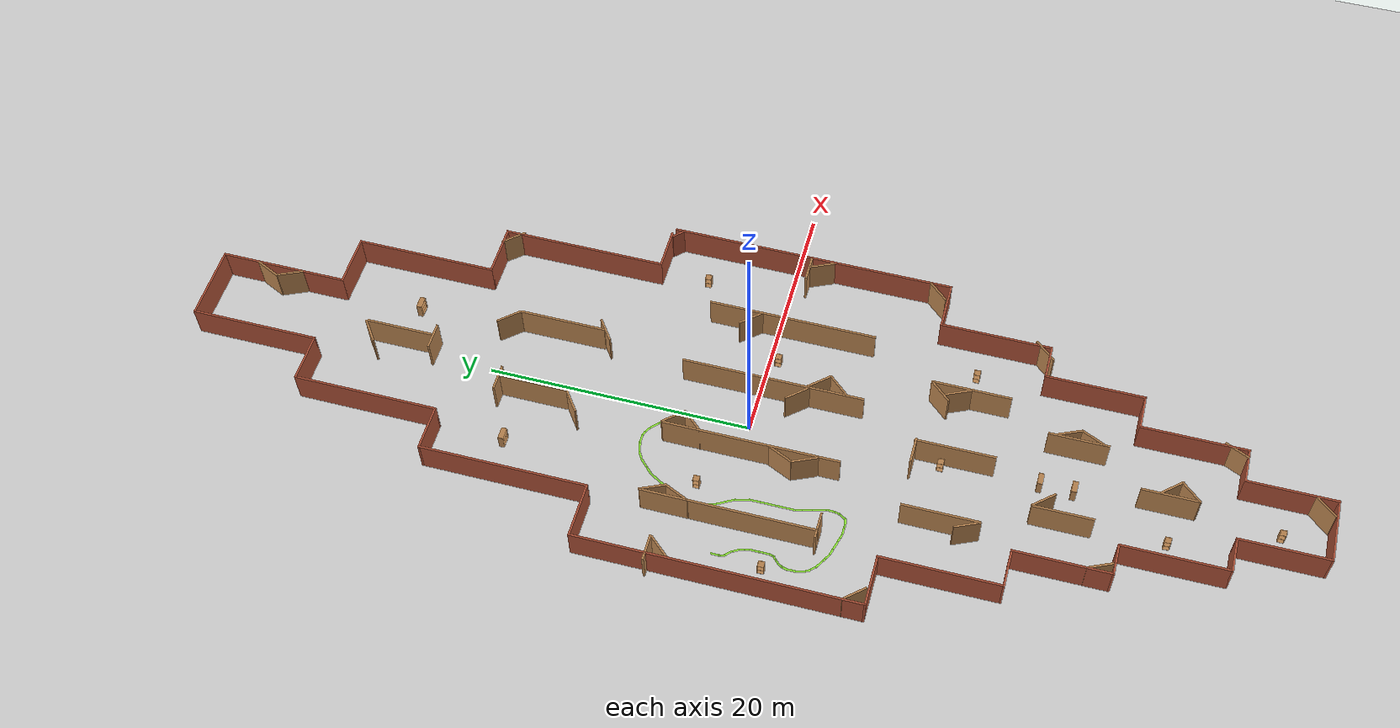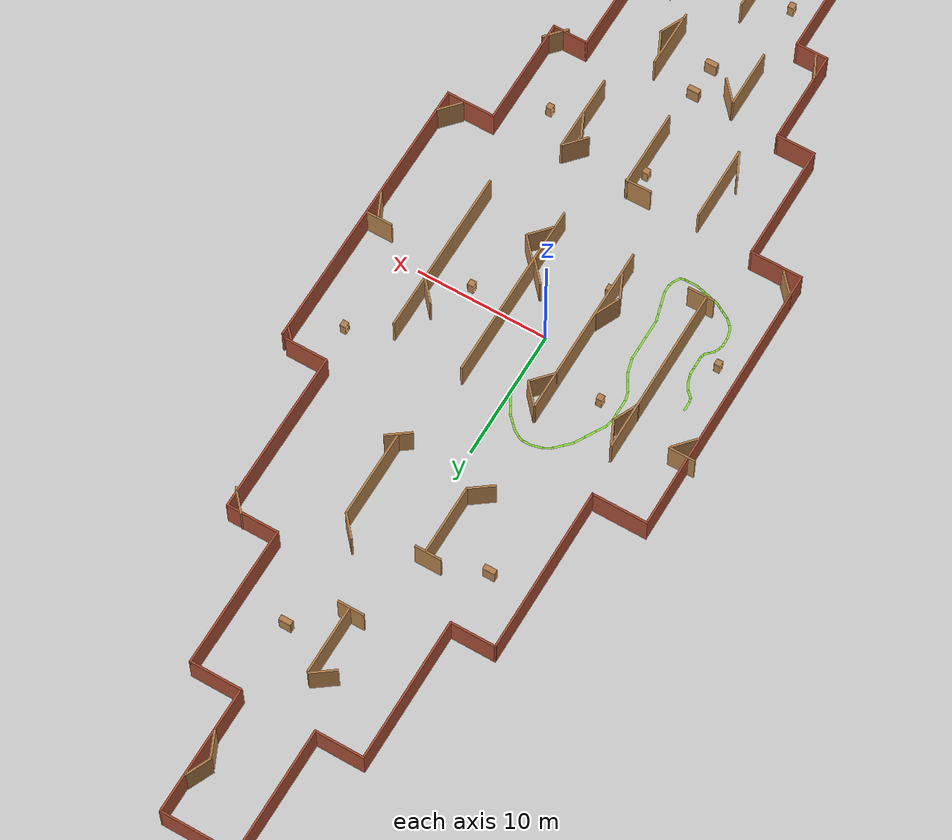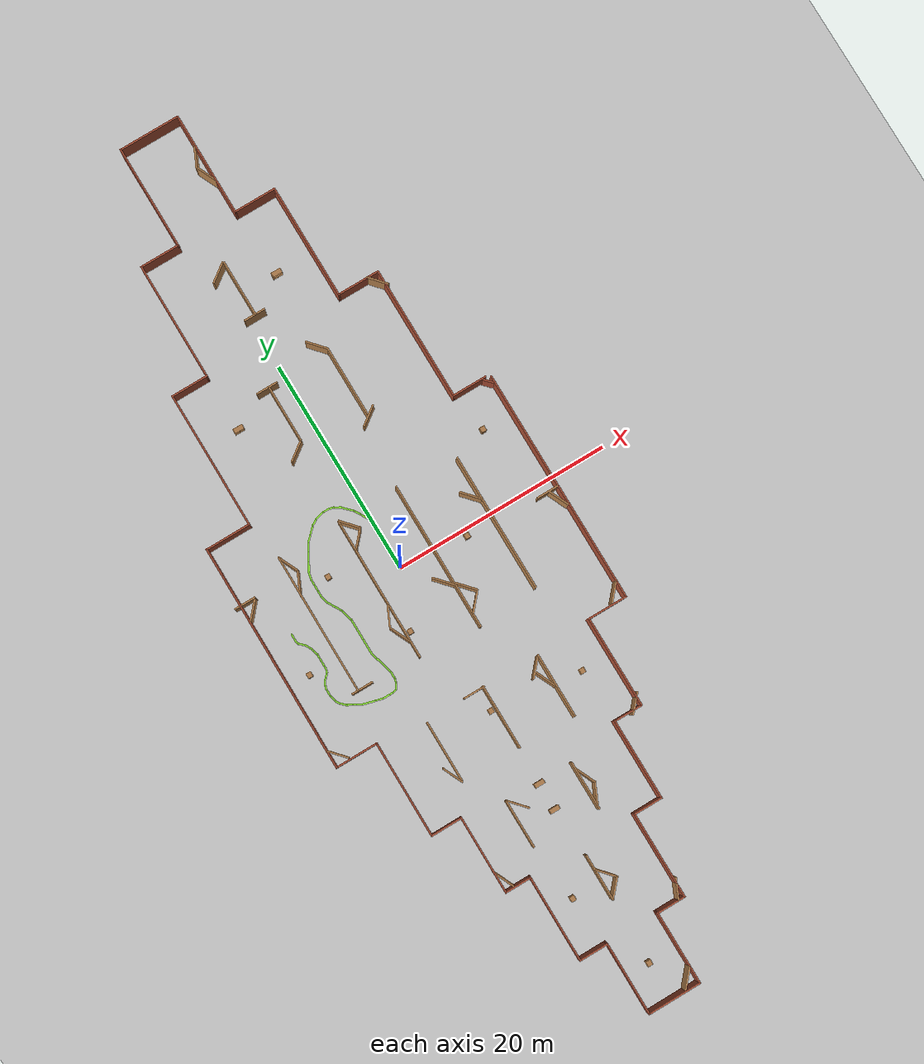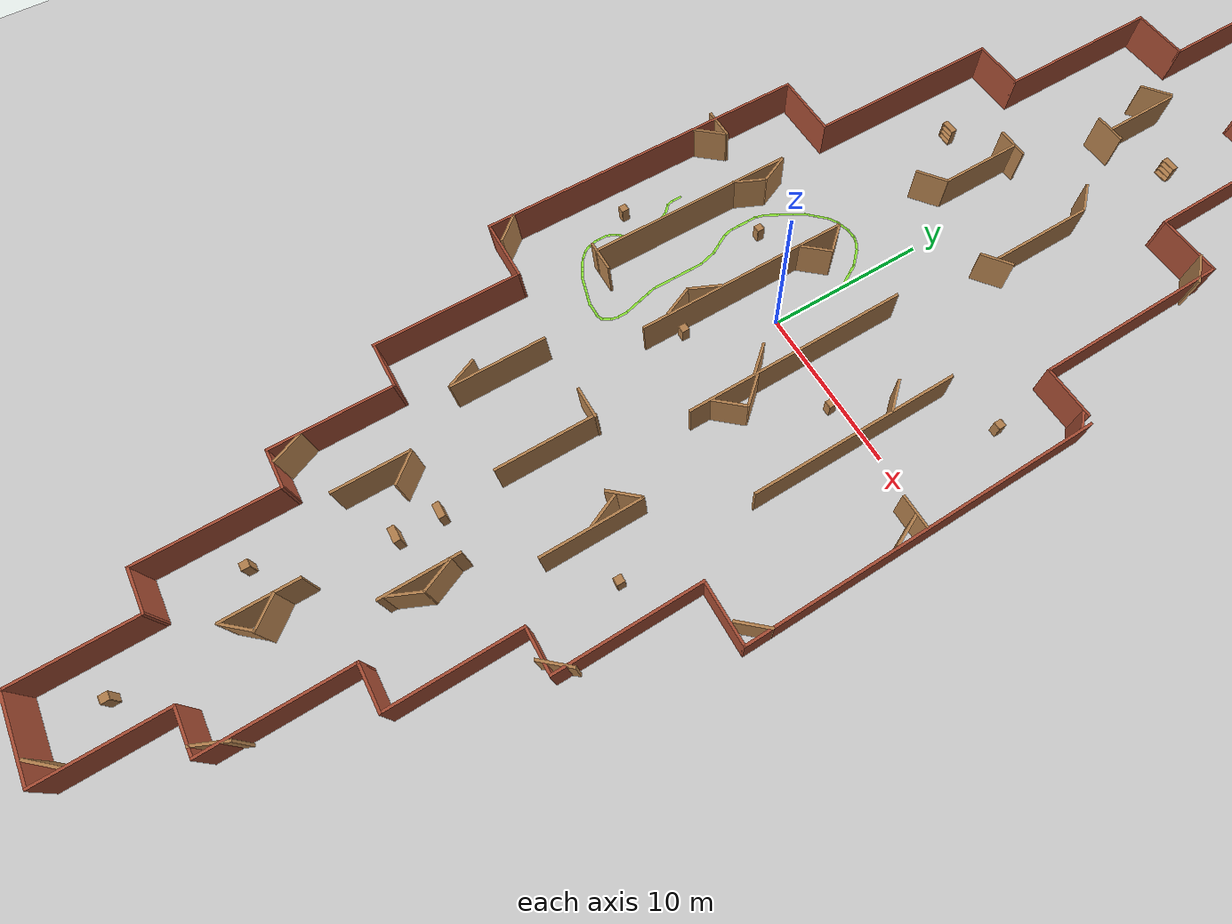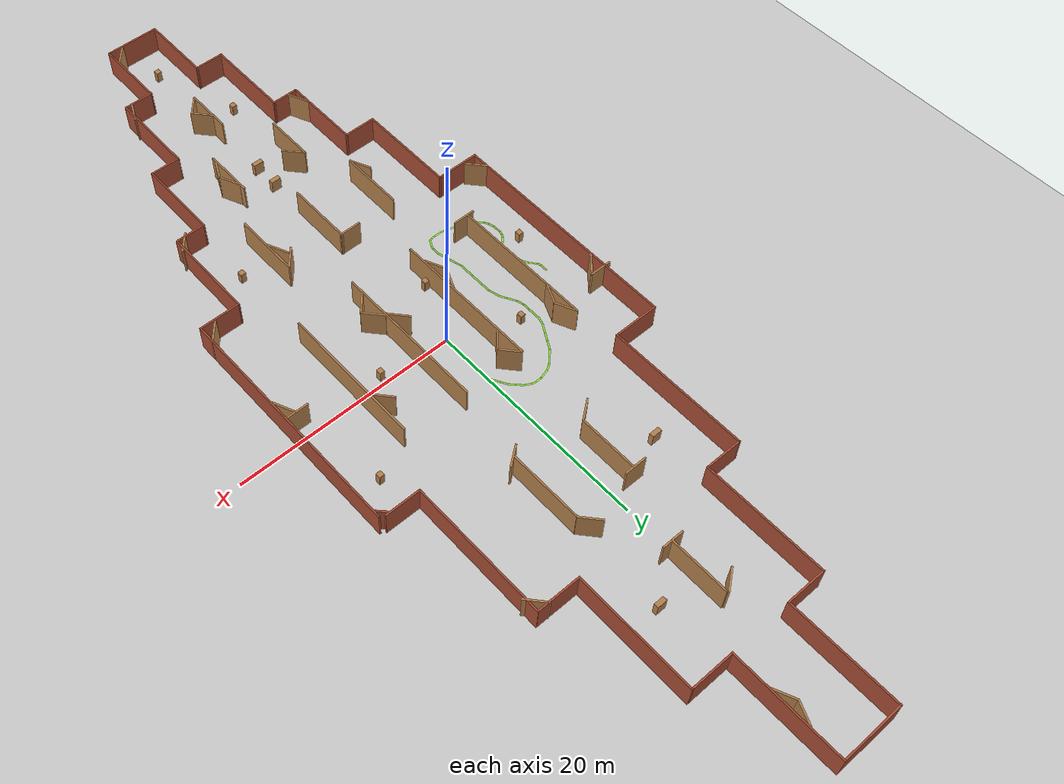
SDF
<sdf version="1.6">
 <world name="default">
  <light name="sun" type="directional">
   <pose>0 0 10 0 -0 0</pose>
   <diffuse>0.8 0.8 0.8 1</diffuse>
   <specular>0.2 0.2 0.2 1</specular>
   <attenuation>
    <range>1000</range>
    <constant>0.9</constant>
    <linear>0.01</linear>
    <quadratic>0.001</quadratic>
   </attenuation>
   <direction>-0.5 0.1 -0.9</direction>
  </light>
  <model name="ground_plane">
   <static>1</static>
   <link name="link">
    <collision name="collision">
     <geometry><plane><normal>0 0 1</normal><size>100 100</size></plane></geometry>
     <surface><friction><ode><mu>100</mu><mu2>50</mu2></ode></friction></surface>
    </collision>
    <visual name="visual">
     <cast_shadows>0</cast_shadows>
     <geometry><plane><normal>0 0 1</normal><size>100 100</size></plane></geometry>
     <material>
      <script><uri>file://media/materials/scripts/gazebo.material</uri><name>Gazebo/Grey</name></script>
     </material>
    </visual>
   </link>
  </model>
  <gravity>0 0 -9.8</gravity>
  <magnetic_field>6e-06 2.3e-05 -4.2e-05</magnetic_field>
  <atmosphere type="adiabatic"/>
  <physics name="default_physics" default="0" type="ode">
   <max_step_size>0.001</max_step_size>
   <real_time_factor>1</real_time_factor>
   <real_time_update_rate>1000</real_time_update_rate>
  </physics>
  <scene><ambient>0.4 0.4 0.4 1</ambient><background>0.7 0.7 0.7 1</background><shadows>1</shadows></scene>
  <spherical_coordinates>
   <surface_model>EARTH_WGS84</surface_model>
   <latitude_deg>0</latitude_deg>
   <longitude_deg>0</longitude_deg>
   <elevation>0</elevation>
   <heading_deg>0</heading_deg>
  </spherical_coordinates>
  <model name="cabinet">
   <static>1</static>
   <link name="cabinet_bottom_plate">
    <inertial>
     <pose>0 0 -1 0 -0 0</pose>
     <inertia><ixx>2.05</ixx><ixy>0</ixy><ixz>0</ixz><iyy>2.05</iyy><iyz>0</iyz><izz>2.05</izz></inertia>
     <mass>25</mass>
    </inertial>
    <collision name="cabinet_bottom_plate_geom">
     <pose>0 0 0.01 0 -0 0</pose>
     <geometry><box><size>0.45 0.45 0.02</size></box></geometry>
    </collision>
    <visual name="cabinet_bottom_plate_geom_visual">
     <pose>0 0 0.01 0 -0 0</pose>
     <geometry><box><size>0.45 0.45 0.02</size></box></geometry>
     <material>
      <script><uri>file://media/materials/scripts/gazebo.material</uri><name>Gazebo/Wood</name></script>
     </material>
    </visual>
    <collision name="cabinet_bottom_plate_geom_cabinet_back_plate">
     <pose>0.235 0 0.51 0 -0 0</pose>
     <geometry><box><size>0.02 0.45 1.02</size></box></geometry>
    </collision>
    <visual name="cabinet_bottom_plate_geom_cabinet_back_plate_visual">
     <pose>0.235 0 0.51 0 -0 0</pose>
     <geometry><box><size>0.02 0.45 1.02</size></box></geometry>
     <material>
      <script><uri>file://media/materials/scripts/gazebo.material</uri><name>Gazebo/Wood</name></script>
     </material>
    </visual>
    <collision name="cabinet_bottom_plate_geom_cabinet_left_plate">
     <pose>0 0.235 0.51 0 -0 0</pose>
     <geometry><box><size>0.45 0.02 1.02</size></box></geometry>
    </collision>
    <visual name="cabinet_bottom_plate_geom_cabinet_left_plate_visual">
     <pose>0 0.235 0.51 0 -0 0</pose>
     <geometry><box><size>0.45 0.02 1.02</size></box></geometry>
     <material>
      <script><uri>file://media/materials/scripts/gazebo.material</uri><name>Gazebo/Wood</name></script>
     </material>
    </visual>
    <collision name="cabinet_bottom_plate_geom_cabinet_middle_plate">
     <pose>0 0 0.51 0 -0 0</pose>
     <geometry><box><size>0.45 0.45 0.02</size></box></geometry>
    </collision>
    <visual name="cabinet_bottom_plate_geom_cabinet_middle_plate_visual">
     <pose>0 0 0.51 0 -0 0</pose>
     <geometry><box><size>0.45 0.45 0.02</size></box></geometry>
     <material>
      <script><uri>file://media/materials/scripts/gazebo.material</uri><name>Gazebo/Wood</name></script>
     </material>
    </visual>
    <collision name="cabinet_bottom_plate_geom_cabinet_right_plate">
     <pose>0 -0.235 0.51 0 -0 0</pose>
     <geometry><box><size>0.45 0.02 1.02</size></box></geometry>
    </collision>
    <visual name="cabinet_bottom_plate_geom_cabinet_right_plate_visual">
     <pose>0 -0.235 0.51 0 -0 0</pose>
     <geometry><box><size>0.45 0.02 1.02</size></box></geometry>
     <material>
      <script><uri>file://media/materials/scripts/gazebo.material</uri><name>Gazebo/Wood</name></script>
     </material>
    </visual>
    <collision name="cabinet_bottom_plate_geom_cabinet_top_plate">
     <pose>0 0 1.01 0 -0 0</pose>
     <geometry><box><size>0.45 0.45 0.02</size></box></geometry>
    </collision>
    <visual name="cabinet_bottom_plate_geom_cabinet_top_plate_visual">
     <pose>0 0 1.01 0 -0 0</pose>
     <geometry><box><size>0.45 0.45 0.02</size></box></geometry>
     <material>
      <script><uri>file://media/materials/scripts/gazebo.material</uri><name>Gazebo/Wood</name></script>
     </material>
    </visual>
   </link>
   <pose>-5.64752 2.41185 0 0 -0 0</pose>
  </model>
  <model name="cabinet_0">
   <static>1</static>
   <link name="cabinet_bottom_plate">
    <inertial>
     <pose>0 0 -1 0 -0 0</pose>
     <inertia><ixx>2.05</ixx><ixy>0</ixy><ixz>0</ixz><iyy>2.05</iyy><iyz>0</iyz><izz>2.05</izz></inertia>
     <mass>25</mass>
    </inertial>
    <collision name="cabinet_bottom_plate_geom">
     <pose>0 0 0.01 0 -0 0</pose>
     <geometry><box><size>0.45 0.45 0.02</size></box></geometry>
    </collision>
    <visual name="cabinet_bottom_plate_geom_visual">
     <pose>0 0 0.01 0 -0 0</pose>
     <geometry><box><size>0.45 0.45 0.02</size></box></geometry>
     <material>
      <script><uri>file://media/materials/scripts/gazebo.material</uri><name>Gazebo/Wood</name></script>
     </material>
    </visual>
    <collision name="cabinet_bottom_plate_geom_cabinet_back_plate">
     <pose>0.235 0 0.51 0 -0 0</pose>
     <geometry><box><size>0.02 0.45 1.02</size></box></geometry>
    </collision>
    <visual name="cabinet_bottom_plate_geom_cabinet_back_plate_visual">
     <pose>0.235 0 0.51 0 -0 0</pose>
     <geometry><box><size>0.02 0.45 1.02</size></box></geometry>
     <material>
      <script><uri>file://media/materials/scripts/gazebo.material</uri><name>Gazebo/Wood</name></script>
     </material>
    </visual>
    <collision name="cabinet_bottom_plate_geom_cabinet_left_plate">
     <pose>0 0.235 0.51 0 -0 0</pose>
     <geometry><box><size>0.45 0.02 1.02</size></box></geometry>
    </collision>
    <visual name="cabinet_bottom_plate_geom_cabinet_left_plate_visual">
     <pose>0 0.235 0.51 0 -0 0</pose>
     <geometry><box><size>0.45 0.02 1.02</size></box></geometry>
     <material>
      <script><uri>file://media/materials/scripts/gazebo.material</uri><name>Gazebo/Wood</name></script>
     </material>
    </visual>
    <collision name="cabinet_bottom_plate_geom_cabinet_middle_plate">
     <pose>0 0 0.51 0 -0 0</pose>
     <geometry><box><size>0.45 0.45 0.02</size></box></geometry>
    </collision>
    <visual name="cabinet_bottom_plate_geom_cabinet_middle_plate_visual">
     <pose>0 0 0.51 0 -0 0</pose>
     <geometry><box><size>0.45 0.45 0.02</size></box></geometry>
     <material>
      <script><uri>file://media/materials/scripts/gazebo.material</uri><name>Gazebo/Wood</name></script>
     </material>
    </visual>
    <collision name="cabinet_bottom_plate_geom_cabinet_right_plate">
     <pose>0 -0.235 0.51 0 -0 0</pose>
     <geometry><box><size>0.45 0.02 1.02</size></box></geometry>
    </collision>
    <visual name="cabinet_bottom_plate_geom_cabinet_right_plate_visual">
     <pose>0 -0.235 0.51 0 -0 0</pose>
     <geometry><box><size>0.45 0.02 1.02</size></box></geometry>
     <material>
      <script><uri>file://media/materials/scripts/gazebo.material</uri><name>Gazebo/Wood</name></script>
     </material>
    </visual>
    <collision name="cabinet_bottom_plate_geom_cabinet_top_plate">
     <pose>0 0 1.01 0 -0 0</pose>
     <geometry><box><size>0.45 0.45 0.02</size></box></geometry>
    </collision>
    <visual name="cabinet_bottom_plate_geom_cabinet_top_plate_visual">
     <pose>0 0 1.01 0 -0 0</pose>
     <geometry><box><size>0.45 0.45 0.02</size></box></geometry>
     <material>
      <script><uri>file://media/materials/scripts/gazebo.material</uri><name>Gazebo/Wood</name></script>
     </material>
    </visual>
   </link>
   <pose>-11.2005 -3.85299 0 0 -0 0</pose>
  </model>
  <model name="cabinet_1">
   <static>1</static>
   <link name="cabinet_bottom_plate">
    <inertial>
     <pose>0 0 -1 0 -0 0</pose>
     <inertia><ixx>2.05</ixx><ixy>0</ixy><ixz>0</ixz><iyy>2.05</iyy><iyz>0</iyz><izz>2.05</izz></inertia>
     <mass>25</mass>
    </inertial>
    <collision name="cabinet_bottom_plate_geom">
     <pose>0 0 0.01 0 -0 0</pose>
     <geometry><box><size>0.45 0.45 0.02</size></box></geometry>
    </collision>
    <visual name="cabinet_bottom_plate_geom_visual">
     <pose>0 0 0.01 0 -0 0</pose>
     <geometry><box><size>0.45 0.45 0.02</size></box></geometry>
     <material>
      <script><uri>file://media/materials/scripts/gazebo.material</uri><name>Gazebo/Wood</name></script>
     </material>
    </visual>
    <collision name="cabinet_bottom_plate_geom_cabinet_back_plate">
     <pose>0.235 0 0.51 0 -0 0</pose>
     <geometry><box><size>0.02 0.45 1.02</size></box></geometry>
    </collision>
    <visual name="cabinet_bottom_plate_geom_cabinet_back_plate_visual">
     <pose>0.235 0 0.51 0 -0 0</pose>
     <geometry><box><size>0.02 0.45 1.02</size></box></geometry>
     <material>
      <script><uri>file://media/materials/scripts/gazebo.material</uri><name>Gazebo/Wood</name></script>
     </material>
    </visual>
    <collision name="cabinet_bottom_plate_geom_cabinet_left_plate">
     <pose>0 0.235 0.51 0 -0 0</pose>
     <geometry><box><size>0.45 0.02 1.02</size></box></geometry>
    </collision>
    <visual name="cabinet_bottom_plate_geom_cabinet_left_plate_visual">
     <pose>0 0.235 0.51 0 -0 0</pose>
     <geometry><box><size>0.45 0.02 1.02</size></box></geometry>
     <material>
      <script><uri>file://media/materials/scripts/gazebo.material</uri><name>Gazebo/Wood</name></script>
     </material>
    </visual>
    <collision name="cabinet_bottom_plate_geom_cabinet_middle_plate">
     <pose>0 0 0.51 0 -0 0</pose>
     <geometry><box><size>0.45 0.45 0.02</size></box></geometry>
    </collision>
    <visual name="cabinet_bottom_plate_geom_cabinet_middle_plate_visual">
     <pose>0 0 0.51 0 -0 0</pose>
     <geometry><box><size>0.45 0.45 0.02</size></box></geometry>
     <material>
      <script><uri>file://media/materials/scripts/gazebo.material</uri><name>Gazebo/Wood</name></script>
     </material>
    </visual>
    <collision name="cabinet_bottom_plate_geom_cabinet_right_plate">
     <pose>0 -0.235 0.51 0 -0 0</pose>
     <geometry><box><size>0.45 0.02 1.02</size></box></geometry>
    </collision>
    <visual name="cabinet_bottom_plate_geom_cabinet_right_plate_visual">
     <pose>0 -0.235 0.51 0 -0 0</pose>
     <geometry><box><size>0.45 0.02 1.02</size></box></geometry>
     <material>
      <script><uri>file://media/materials/scripts/gazebo.material</uri><name>Gazebo/Wood</name></script>
     </material>
    </visual>
    <collision name="cabinet_bottom_plate_geom_cabinet_top_plate">
     <pose>0 0 1.01 0 -0 0</pose>
     <geometry><box><size>0.45 0.45 0.02</size></box></geometry>
    </collision>
    <visual name="cabinet_bottom_plate_geom_cabinet_top_plate_visual">
     <pose>0 0 1.01 0 -0 0</pose>
     <geometry><box><size>0.45 0.45 0.02</size></box></geometry>
     <material>
      <script><uri>file://media/materials/scripts/gazebo.material</uri><name>Gazebo/Wood</name></script>
     </material>
    </visual>
   </link>
   <pose>6.15971 -0.636203 0 0 -0 0</pose>
  </model>
  <model name="cabinet_2">
   <static>1</static>
   <link name="cabinet_bottom_plate">
    <inertial>
     <pose>0 0 -1 0 -0 0</pose>
     <inertia><ixx>2.05</ixx><ixy>0</ixy><ixz>0</ixz><iyy>2.05</iyy><iyz>0</iyz><izz>2.05</izz></inertia>
     <mass>25</mass>
    </inertial>
    <collision name="cabinet_bottom_plate_geom">
     <pose>0 0 0.01 0 -0 0</pose>
     <geometry><box><size>0.45 0.45 0.02</size></box></geometry>
    </collision>
    <visual name="cabinet_bottom_plate_geom_visual">
     <pose>0 0 0.01 0 -0 0</pose>
     <geometry><box><size>0.45 0.45 0.02</size></box></geometry>
     <material>
      <script><uri>file://media/materials/scripts/gazebo.material</uri><name>Gazebo/Wood</name></script>
     </material>
    </visual>
    <collision name="cabinet_bottom_plate_geom_cabinet_back_plate">
     <pose>0.235 0 0.51 0 -0 0</pose>
     <geometry><box><size>0.02 0.45 1.02</size></box></geometry>
    </collision>
    <visual name="cabinet_bottom_plate_geom_cabinet_back_plate_visual">
     <pose>0.235 0 0.51 0 -0 0</pose>
     <geometry><box><size>0.02 0.45 1.02</size></box></geometry>
     <material>
      <script><uri>file://media/materials/scripts/gazebo.material</uri><name>Gazebo/Wood</name></script>
     </material>
    </visual>
    <collision name="cabinet_bottom_plate_geom_cabinet_left_plate">
     <pose>0 0.235 0.51 0 -0 0</pose>
     <geometry><box><size>0.45 0.02 1.02</size></box></geometry>
    </collision>
    <visual name="cabinet_bottom_plate_geom_cabinet_left_plate_visual">
     <pose>0 0.235 0.51 0 -0 0</pose>
     <geometry><box><size>0.45 0.02 1.02</size></box></geometry>
     <material>
      <script><uri>file://media/materials/scripts/gazebo.material</uri><name>Gazebo/Wood</name></script>
     </material>
    </visual>
    <collision name="cabinet_bottom_plate_geom_cabinet_middle_plate">
     <pose>0 0 0.51 0 -0 0</pose>
     <geometry><box><size>0.45 0.45 0.02</size></box></geometry>
    </collision>
    <visual name="cabinet_bottom_plate_geom_cabinet_middle_plate_visual">
     <pose>0 0 0.51 0 -0 0</pose>
     <geometry><box><size>0.45 0.45 0.02</size></box></geometry>
     <material>
      <script><uri>file://media/materials/scripts/gazebo.material</uri><name>Gazebo/Wood</name></script>
     </material>
    </visual>
    <collision name="cabinet_bottom_plate_geom_cabinet_right_plate">
     <pose>0 -0.235 0.51 0 -0 0</pose>
     <geometry><box><size>0.45 0.02 1.02</size></box></geometry>
    </collision>
    <visual name="cabinet_bottom_plate_geom_cabinet_right_plate_visual">
     <pose>0 -0.235 0.51 0 -0 0</pose>
     <geometry><box><size>0.45 0.02 1.02</size></box></geometry>
     <material>
      <script><uri>file://media/materials/scripts/gazebo.material</uri><name>Gazebo/Wood</name></script>
     </material>
    </visual>
    <collision name="cabinet_bottom_plate_geom_cabinet_top_plate">
     <pose>0 0 1.01 0 -0 0</pose>
     <geometry><box><size>0.45 0.45 0.02</size></box></geometry>
    </collision>
    <visual name="cabinet_bottom_plate_geom_cabinet_top_plate_visual">
     <pose>0 0 1.01 0 -0 0</pose>
     <geometry><box><size>0.45 0.45 0.02</size></box></geometry>
     <material>
      <script><uri>file://media/materials/scripts/gazebo.material</uri><name>Gazebo/Wood</name></script>
     </material>
    </visual>
   </link>
   <pose>11.9831 6.41172 0 0 -0 0</pose>
  </model>
  <model name="bookshelf">
   <static>1</static>
   <link name="link">
    <inertial><mass>1</mass></inertial>
    <collision name="back">
     <pose>0 0.005 0.6 0 -0 0</pose>
     <geometry><box><size>0.9 0.01 1.2</size></box></geometry>
    </collision>
    <visual name="visual1">
     <pose>0 0.005 0.6 0 -0 0</pose>
     <geometry><box><size>0.9 0.01 1.2</size></box></geometry>
     <material>
      <script><uri>file://media/materials/scripts/gazebo.material</uri><name>Gazebo/Wood</name></script>
     </material>
    </visual>
    <collision name="left_side">
     <pose>0.45 -0.195 0.6 0 -0 0</pose>
     <geometry><box><size>0.02 0.4 1.2</size></box></geometry>
    </collision>
    <visual name="visual2">
     <pose>0.45 -0.195 0.6 0 -0 0</pose>
     <geometry><box><size>0.02 0.4 1.2</size></box></geometry>
     <material>
      <script><uri>file://media/materials/scripts/gazebo.material</uri><name>Gazebo/Wood</name></script>
     </material>
    </visual>
    <collision name="right_side">
     <pose>-0.45 -0.195 0.6 0 -0 0</pose>
     <geometry><box><size>0.02 0.4 1.2</size></box></geometry>
    </collision>
    <visual name="visual3">
     <pose>-0.45 -0.195 0.6 0 -0 0</pose>
     <geometry><box><size>0.02 0.4 1.2</size></box></geometry>
     <material>
      <script><uri>file://media/materials/scripts/gazebo.material</uri><name>Gazebo/Wood</name></script>
     </material>
    </visual>
    <collision name="bottom">
     <pose>0 -0.195 0.03 0 -0 0</pose>
     <geometry><box><size>0.88 0.4 0.06</size></box></geometry>
    </collision>
    <visual name="visual4">
     <pose>0 -0.195 0.03 0 -0 0</pose>
     <geometry><box><size>0.88 0.4 0.06</size></box></geometry>
     <material>
      <script><uri>file://media/materials/scripts/gazebo.material</uri><name>Gazebo/Wood</name></script>
     </material>
    </visual>
    <collision name="top">
     <pose>0 -0.195 1.19 0 -0 0</pose>
     <geometry><box><size>0.88 0.4 0.02</size></box></geometry>
    </collision>
    <visual name="visual5">
     <pose>0 -0.195 1.19 0 -0 0</pose>
     <geometry><box><size>0.88 0.4 0.02</size></box></geometry>
     <material>
      <script><uri>file://media/materials/scripts/gazebo.material</uri><name>Gazebo/Wood</name></script>
     </material>
    </visual>
    <collision name="low_shelf">
     <pose>0 -0.195 0.43 0 -0 0</pose>
     <geometry><box><size>0.88 0.4 0.02</size></box></geometry>
    </collision>
    <visual name="visual6">
     <pose>0 -0.195 0.43 0 -0 0</pose>
     <geometry><box><size>0.88 0.4 0.02</size></box></geometry>
     <material>
      <script><uri>file://media/materials/scripts/gazebo.material</uri><name>Gazebo/Wood</name></script>
     </material>
    </visual>
    <collision name="high_shelf">
     <pose>0 -0.195 0.8 0 -0 0</pose>
     <geometry><box><size>0.88 0.4 0.02</size></box></geometry>
    </collision>
    <visual name="visual7">
     <pose>0 -0.195 0.8 0 -0 0</pose>
     <geometry><box><size>0.88 0.4 0.02</size></box></geometry>
     <material>
      <script><uri>file://media/materials/scripts/gazebo.material</uri><name>Gazebo/Wood</name></script>
     </material>
    </visual>
   </link>
   <pose>0.586546 -21.2596 0 0 -0 0</pose>
  </model>
  <model name="bookshelf_0">
   <static>1</static>
   <link name="link">
    <inertial><mass>1</mass></inertial>
    <collision name="back">
     <pose>0 0.005 0.6 0 -0 0</pose>
     <geometry><box><size>0.9 0.01 1.2</size></box></geometry>
    </collision>
    <visual name="visual1">
     <pose>0 0.005 0.6 0 -0 0</pose>
     <geometry><box><size>0.9 0.01 1.2</size></box></geometry>
     <material>
      <script><uri>file://media/materials/scripts/gazebo.material</uri><name>Gazebo/Wood</name></script>
     </material>
    </visual>
    <collision name="left_side">
     <pose>0.45 -0.195 0.6 0 -0 0</pose>
     <geometry><box><size>0.02 0.4 1.2</size></box></geometry>
    </collision>
    <visual name="visual2">
     <pose>0.45 -0.195 0.6 0 -0 0</pose>
     <geometry><box><size>0.02 0.4 1.2</size></box></geometry>
     <material>
      <script><uri>file://media/materials/scripts/gazebo.material</uri><name>Gazebo/Wood</name></script>
     </material>
    </visual>
    <collision name="right_side">
     <pose>-0.45 -0.195 0.6 0 -0 0</pose>
     <geometry><box><size>0.02 0.4 1.2</size></box></geometry>
    </collision>
    <visual name="visual3">
     <pose>-0.45 -0.195 0.6 0 -0 0</pose>
     <geometry><box><size>0.02 0.4 1.2</size></box></geometry>
     <material>
      <script><uri>file://media/materials/scripts/gazebo.material</uri><name>Gazebo/Wood</name></script>
     </material>
    </visual>
    <collision name="bottom">
     <pose>0 -0.195 0.03 0 -0 0</pose>
     <geometry><box><size>0.88 0.4 0.06</size></box></geometry>
    </collision>
    <visual name="visual4">
     <pose>0 -0.195 0.03 0 -0 0</pose>
     <geometry><box><size>0.88 0.4 0.06</size></box></geometry>
     <material>
      <script><uri>file://media/materials/scripts/gazebo.material</uri><name>Gazebo/Wood</name></script>
     </material>
    </visual>
    <collision name="top">
     <pose>0 -0.195 1.19 0 -0 0</pose>
     <geometry><box><size>0.88 0.4 0.02</size></box></geometry>
    </collision>
    <visual name="visual5">
     <pose>0 -0.195 1.19 0 -0 0</pose>
     <geometry><box><size>0.88 0.4 0.02</size></box></geometry>
     <material>
      <script><uri>file://media/materials/scripts/gazebo.material</uri><name>Gazebo/Wood</name></script>
     </material>
    </visual>
    <collision name="low_shelf">
     <pose>0 -0.195 0.43 0 -0 0</pose>
     <geometry><box><size>0.88 0.4 0.02</size></box></geometry>
    </collision>
    <visual name="visual6">
     <pose>0 -0.195 0.43 0 -0 0</pose>
     <geometry><box><size>0.88 0.4 0.02</size></box></geometry>
     <material>
      <script><uri>file://media/materials/scripts/gazebo.material</uri><name>Gazebo/Wood</name></script>
     </material>
    </visual>
    <collision name="high_shelf">
     <pose>0 -0.195 0.8 0 -0 0</pose>
     <geometry><box><size>0.88 0.4 0.02</size></box></geometry>
    </collision>
    <visual name="visual7">
     <pose>0 -0.195 0.8 0 -0 0</pose>
     <geometry><box><size>0.88 0.4 0.02</size></box></geometry>
     <material>
      <script><uri>file://media/materials/scripts/gazebo.material</uri><name>Gazebo/Wood</name></script>
     </material>
    </visual>
   </link>
   <pose>0.557156 -23.734 0 0 -0 0</pose>
  </model>
  <model name="bookshelf_1">
   <static>1</static>
   <link name="link">
    <inertial><mass>1</mass></inertial>
    <collision name="back">
     <pose>0 0.005 0.6 0 -0 0</pose>
     <geometry><box><size>0.9 0.01 1.2</size></box></geometry>
    </collision>
    <visual name="visual1">
     <pose>0 0.005 0.6 0 -0 0</pose>
     <geometry><box><size>0.9 0.01 1.2</size></box></geometry>
     <material>
      <script><uri>file://media/materials/scripts/gazebo.material</uri><name>Gazebo/Wood</name></script>
     </material>
    </visual>
    <collision name="left_side">
     <pose>0.45 -0.195 0.6 0 -0 0</pose>
     <geometry><box><size>0.02 0.4 1.2</size></box></geometry>
    </collision>
    <visual name="visual2">
     <pose>0.45 -0.195 0.6 0 -0 0</pose>
     <geometry><box><size>0.02 0.4 1.2</size></box></geometry>
     <material>
      <script><uri>file://media/materials/scripts/gazebo.material</uri><name>Gazebo/Wood</name></script>
     </material>
    </visual>
    <collision name="right_side">
     <pose>-0.45 -0.195 0.6 0 -0 0</pose>
     <geometry><box><size>0.02 0.4 1.2</size></box></geometry>
    </collision>
    <visual name="visual3">
     <pose>-0.45 -0.195 0.6 0 -0 0</pose>
     <geometry><box><size>0.02 0.4 1.2</size></box></geometry>
     <material>
      <script><uri>file://media/materials/scripts/gazebo.material</uri><name>Gazebo/Wood</name></script>
     </material>
    </visual>
    <collision name="bottom">
     <pose>0 -0.195 0.03 0 -0 0</pose>
     <geometry><box><size>0.88 0.4 0.06</size></box></geometry>
    </collision>
    <visual name="visual4">
     <pose>0 -0.195 0.03 0 -0 0</pose>
     <geometry><box><size>0.88 0.4 0.06</size></box></geometry>
     <material>
      <script><uri>file://media/materials/scripts/gazebo.material</uri><name>Gazebo/Wood</name></script>
     </material>
    </visual>
    <collision name="top">
     <pose>0 -0.195 1.19 0 -0 0</pose>
     <geometry><box><size>0.88 0.4 0.02</size></box></geometry>
    </collision>
    <visual name="visual5">
     <pose>0 -0.195 1.19 0 -0 0</pose>
     <geometry><box><size>0.88 0.4 0.02</size></box></geometry>
     <material>
      <script><uri>file://media/materials/scripts/gazebo.material</uri><name>Gazebo/Wood</name></script>
     </material>
    </visual>
    <collision name="low_shelf">
     <pose>0 -0.195 0.43 0 -0 0</pose>
     <geometry><box><size>0.88 0.4 0.02</size></box></geometry>
    </collision>
    <visual name="visual6">
     <pose>0 -0.195 0.43 0 -0 0</pose>
     <geometry><box><size>0.88 0.4 0.02</size></box></geometry>
     <material>
      <script><uri>file://media/materials/scripts/gazebo.material</uri><name>Gazebo/Wood</name></script>
     </material>
    </visual>
    <collision name="high_shelf">
     <pose>0 -0.195 0.8 0 -0 0</pose>
     <geometry><box><size>0.88 0.4 0.02</size></box></geometry>
    </collision>
    <visual name="visual7">
     <pose>0 -0.195 0.8 0 -0 0</pose>
     <geometry><box><size>0.88 0.4 0.02</size></box></geometry>
     <material>
      <script><uri>file://media/materials/scripts/gazebo.material</uri><name>Gazebo/Wood</name></script>
     </material>
    </visual>
   </link>
   <pose>-5.70602 17.248 0 0 -0 0</pose>
  </model>
  <model name="bookshelf_2">
   <static>1</static>
   <link name="link">
    <inertial><mass>1</mass></inertial>
    <collision name="back">
     <pose>0 0.005 0.6 0 -0 0</pose>
     <geometry><box><size>0.9 0.01 1.2</size></box></geometry>
    </collision>
    <visual name="visual1">
     <pose>0 0.005 0.6 0 -0 0</pose>
     <geometry><box><size>0.9 0.01 1.2</size></box></geometry>
     <material>
      <script><uri>file://media/materials/scripts/gazebo.material</uri><name>Gazebo/Wood</name></script>
     </material>
    </visual>
    <collision name="left_side">
     <pose>0.45 -0.195 0.6 0 -0 0</pose>
     <geometry><box><size>0.02 0.4 1.2</size></box></geometry>
    </collision>
    <visual name="visual2">
     <pose>0.45 -0.195 0.6 0 -0 0</pose>
     <geometry><box><size>0.02 0.4 1.2</size></box></geometry>
     <material>
      <script><uri>file://media/materials/scripts/gazebo.material</uri><name>Gazebo/Wood</name></script>
     </material>
    </visual>
    <collision name="right_side">
     <pose>-0.45 -0.195 0.6 0 -0 0</pose>
     <geometry><box><size>0.02 0.4 1.2</size></box></geometry>
    </collision>
    <visual name="visual3">
     <pose>-0.45 -0.195 0.6 0 -0 0</pose>
     <geometry><box><size>0.02 0.4 1.2</size></box></geometry>
     <material>
      <script><uri>file://media/materials/scripts/gazebo.material</uri><name>Gazebo/Wood</name></script>
     </material>
    </visual>
    <collision name="bottom">
     <pose>0 -0.195 0.03 0 -0 0</pose>
     <geometry><box><size>0.88 0.4 0.06</size></box></geometry>
    </collision>
    <visual name="visual4">
     <pose>0 -0.195 0.03 0 -0 0</pose>
     <geometry><box><size>0.88 0.4 0.06</size></box></geometry>
     <material>
      <script><uri>file://media/materials/scripts/gazebo.material</uri><name>Gazebo/Wood</name></script>
     </material>
    </visual>
    <collision name="top">
     <pose>0 -0.195 1.19 0 -0 0</pose>
     <geometry><box><size>0.88 0.4 0.02</size></box></geometry>
    </collision>
    <visual name="visual5">
     <pose>0 -0.195 1.19 0 -0 0</pose>
     <geometry><box><size>0.88 0.4 0.02</size></box></geometry>
     <material>
      <script><uri>file://media/materials/scripts/gazebo.material</uri><name>Gazebo/Wood</name></script>
     </material>
    </visual>
    <collision name="low_shelf">
     <pose>0 -0.195 0.43 0 -0 0</pose>
     <geometry><box><size>0.88 0.4 0.02</size></box></geometry>
    </collision>
    <visual name="visual6">
     <pose>0 -0.195 0.43 0 -0 0</pose>
     <geometry><box><size>0.88 0.4 0.02</size></box></geometry>
     <material>
      <script><uri>file://media/materials/scripts/gazebo.material</uri><name>Gazebo/Wood</name></script>
     </material>
    </visual>
    <collision name="high_shelf">
     <pose>0 -0.195 0.8 0 -0 0</pose>
     <geometry><box><size>0.88 0.4 0.02</size></box></geometry>
    </collision>
    <visual name="visual7">
     <pose>0 -0.195 0.8 0 -0 0</pose>
     <geometry><box><size>0.88 0.4 0.02</size></box></geometry>
     <material>
      <script><uri>file://media/materials/scripts/gazebo.material</uri><name>Gazebo/Wood</name></script>
     </material>
    </visual>
   </link>
   <pose>3.89381 27.1031 0 0 -0 0</pose>
  </model>
  <model name="cabinet_3">
   <static>1</static>
   <link name="cabinet_bottom_plate">
    <inertial>
     <pose>0 0 -1 0 -0 0</pose>
     <inertia><ixx>2.05</ixx><ixy>0</ixy><ixz>0</ixz><iyy>2.05</iyy><iyz>0</iyz><izz>2.05</izz></inertia>
     <mass>25</mass>
    </inertial>
    <collision name="cabinet_bottom_plate_geom">
     <pose>0 0 0.01 0 -0 0</pose>
     <geometry><box><size>0.45 0.45 0.02</size></box></geometry>
    </collision>
    <visual name="cabinet_bottom_plate_geom_visual">
     <pose>0 0 0.01 0 -0 0</pose>
     <geometry><box><size>0.45 0.45 0.02</size></box></geometry>
     <material>
      <script><uri>file://media/materials/scripts/gazebo.material</uri><name>Gazebo/Wood</name></script>
     </material>
    </visual>
    <collision name="cabinet_bottom_plate_geom_cabinet_back_plate">
     <pose>0.235 0 0.51 0 -0 0</pose>
     <geometry><box><size>0.02 0.45 1.02</size></box></geometry>
    </collision>
    <visual name="cabinet_bottom_plate_geom_cabinet_back_plate_visual">
     <pose>0.235 0 0.51 0 -0 0</pose>
     <geometry><box><size>0.02 0.45 1.02</size></box></geometry>
     <material>
      <script><uri>file://media/materials/scripts/gazebo.material</uri><name>Gazebo/Wood</name></script>
     </material>
    </visual>
    <collision name="cabinet_bottom_plate_geom_cabinet_left_plate">
     <pose>0 0.235 0.51 0 -0 0</pose>
     <geometry><box><size>0.45 0.02 1.02</size></box></geometry>
    </collision>
    <visual name="cabinet_bottom_plate_geom_cabinet_left_plate_visual">
     <pose>0 0.235 0.51 0 -0 0</pose>
     <geometry><box><size>0.45 0.02 1.02</size></box></geometry>
     <material>
      <script><uri>file://media/materials/scripts/gazebo.material</uri><name>Gazebo/Wood</name></script>
     </material>
    </visual>
    <collision name="cabinet_bottom_plate_geom_cabinet_middle_plate">
     <pose>0 0 0.51 0 -0 0</pose>
     <geometry><box><size>0.45 0.45 0.02</size></box></geometry>
    </collision>
    <visual name="cabinet_bottom_plate_geom_cabinet_middle_plate_visual">
     <pose>0 0 0.51 0 -0 0</pose>
     <geometry><box><size>0.45 0.45 0.02</size></box></geometry>
     <material>
      <script><uri>file://media/materials/scripts/gazebo.material</uri><name>Gazebo/Wood</name></script>
     </material>
    </visual>
    <collision name="cabinet_bottom_plate_geom_cabinet_right_plate">
     <pose>0 -0.235 0.51 0 -0 0</pose>
     <geometry><box><size>0.45 0.02 1.02</size></box></geometry>
    </collision>
    <visual name="cabinet_bottom_plate_geom_cabinet_right_plate_visual">
     <pose>0 -0.235 0.51 0 -0 0</pose>
     <geometry><box><size>0.45 0.02 1.02</size></box></geometry>
     <material>
      <script><uri>file://media/materials/scripts/gazebo.material</uri><name>Gazebo/Wood</name></script>
     </material>
    </visual>
    <collision name="cabinet_bottom_plate_geom_cabinet_top_plate">
     <pose>0 0 1.01 0 -0 0</pose>
     <geometry><box><size>0.45 0.45 0.02</size></box></geometry>
    </collision>
    <visual name="cabinet_bottom_plate_geom_cabinet_top_plate_visual">
     <pose>0 0 1.01 0 -0 0</pose>
     <geometry><box><size>0.45 0.45 0.02</size></box></geometry>
     <material>
      <script><uri>file://media/materials/scripts/gazebo.material</uri><name>Gazebo/Wood</name></script>
     </material>
    </visual>
   </link>
   <pose>0.258671 -14.2311 0 0 -0 0</pose>
  </model>
  <model name="cabinet_4">
   <static>1</static>
   <link name="cabinet_bottom_plate">
    <inertial>
     <pose>0 0 -1 0 -0 0</pose>
     <inertia><ixx>2.05</ixx><ixy>0</ixy><ixz>0</ixz><iyy>2.05</iyy><iyz>0</iyz><izz>2.05</izz></inertia>
     <mass>25</mass>
    </inertial>
    <collision name="cabinet_bottom_plate_geom">
     <pose>0 0 0.01 0 -0 0</pose>
     <geometry><box><size>0.45 0.45 0.02</size></box></geometry>
    </collision>
    <visual name="cabinet_bottom_plate_geom_visual">
     <pose>0 0 0.01 0 -0 0</pose>
     <geometry><box><size>0.45 0.45 0.02</size></box></geometry>
     <material>
      <script><uri>file://media/materials/scripts/gazebo.material</uri><name>Gazebo/Wood</name></script>
     </material>
    </visual>
    <collision name="cabinet_bottom_plate_geom_cabinet_back_plate">
     <pose>0.235 0 0.51 0 -0 0</pose>
     <geometry><box><size>0.02 0.45 1.02</size></box></geometry>
    </collision>
    <visual name="cabinet_bottom_plate_geom_cabinet_back_plate_visual">
     <pose>0.235 0 0.51 0 -0 0</pose>
     <geometry><box><size>0.02 0.45 1.02</size></box></geometry>
     <material>
      <script><uri>file://media/materials/scripts/gazebo.material</uri><name>Gazebo/Wood</name></script>
     </material>
    </visual>
    <collision name="cabinet_bottom_plate_geom_cabinet_left_plate">
     <pose>0 0.235 0.51 0 -0 0</pose>
     <geometry><box><size>0.45 0.02 1.02</size></box></geometry>
    </collision>
    <visual name="cabinet_bottom_plate_geom_cabinet_left_plate_visual">
     <pose>0 0.235 0.51 0 -0 0</pose>
     <geometry><box><size>0.45 0.02 1.02</size></box></geometry>
     <material>
      <script><uri>file://media/materials/scripts/gazebo.material</uri><name>Gazebo/Wood</name></script>
     </material>
    </visual>
    <collision name="cabinet_bottom_plate_geom_cabinet_middle_plate">
     <pose>0 0 0.51 0 -0 0</pose>
     <geometry><box><size>0.45 0.45 0.02</size></box></geometry>
    </collision>
    <visual name="cabinet_bottom_plate_geom_cabinet_middle_plate_visual">
     <pose>0 0 0.51 0 -0 0</pose>
     <geometry><box><size>0.45 0.45 0.02</size></box></geometry>
     <material>
      <script><uri>file://media/materials/scripts/gazebo.material</uri><name>Gazebo/Wood</name></script>
     </material>
    </visual>
    <collision name="cabinet_bottom_plate_geom_cabinet_right_plate">
     <pose>0 -0.235 0.51 0 -0 0</pose>
     <geometry><box><size>0.45 0.02 1.02</size></box></geometry>
    </collision>
    <visual name="cabinet_bottom_plate_geom_cabinet_right_plate_visual">
     <pose>0 -0.235 0.51 0 -0 0</pose>
     <geometry><box><size>0.45 0.02 1.02</size></box></geometry>
     <material>
      <script><uri>file://media/materials/scripts/gazebo.material</uri><name>Gazebo/Wood</name></script>
     </material>
    </visual>
    <collision name="cabinet_bottom_plate_geom_cabinet_top_plate">
     <pose>0 0 1.01 0 -0 0</pose>
     <geometry><box><size>0.45 0.45 0.02</size></box></geometry>
    </collision>
    <visual name="cabinet_bottom_plate_geom_cabinet_top_plate_visual">
     <pose>0 0 1.01 0 -0 0</pose>
     <geometry><box><size>0.45 0.45 0.02</size></box></geometry>
     <material>
      <script><uri>file://media/materials/scripts/gazebo.material</uri><name>Gazebo/Wood</name></script>
     </material>
    </visual>
   </link>
   <pose>-2.09099 -5.06294 0 0 -0 0</pose>
  </model>
  <model name="cabinet_5">
   <static>1</static>
   <link name="cabinet_bottom_plate">
    <inertial>
     <pose>0 0 -1 0 -0 0</pose>
     <inertia><ixx>2.05</ixx><ixy>0</ixy><ixz>0</ixz><iyy>2.05</iyy><iyz>0</iyz><izz>2.05</izz></inertia>
     <mass>25</mass>
    </inertial>
    <collision name="cabinet_bottom_plate_geom">
     <pose>0 0 0.01 0 -0 0</pose>
     <geometry><box><size>0.45 0.45 0.02</size></box></geometry>
    </collision>
    <visual name="cabinet_bottom_plate_geom_visual">
     <pose>0 0 0.01 0 -0 0</pose>
     <geometry><box><size>0.45 0.45 0.02</size></box></geometry>
     <material>
      <script><uri>file://media/materials/scripts/gazebo.material</uri><name>Gazebo/Wood</name></script>
     </material>
    </visual>
    <collision name="cabinet_bottom_plate_geom_cabinet_back_plate">
     <pose>0.235 0 0.51 0 -0 0</pose>
     <geometry><box><size>0.02 0.45 1.02</size></box></geometry>
    </collision>
    <visual name="cabinet_bottom_plate_geom_cabinet_back_plate_visual">
     <pose>0.235 0 0.51 0 -0 0</pose>
     <geometry><box><size>0.02 0.45 1.02</size></box></geometry>
     <material>
      <script><uri>file://media/materials/scripts/gazebo.material</uri><name>Gazebo/Wood</name></script>
     </material>
    </visual>
    <collision name="cabinet_bottom_plate_geom_cabinet_left_plate">
     <pose>0 0.235 0.51 0 -0 0</pose>
     <geometry><box><size>0.45 0.02 1.02</size></box></geometry>
    </collision>
    <visual name="cabinet_bottom_plate_geom_cabinet_left_plate_visual">
     <pose>0 0.235 0.51 0 -0 0</pose>
     <geometry><box><size>0.45 0.02 1.02</size></box></geometry>
     <material>
      <script><uri>file://media/materials/scripts/gazebo.material</uri><name>Gazebo/Wood</name></script>
     </material>
    </visual>
    <collision name="cabinet_bottom_plate_geom_cabinet_middle_plate">
     <pose>0 0 0.51 0 -0 0</pose>
     <geometry><box><size>0.45 0.45 0.02</size></box></geometry>
    </collision>
    <visual name="cabinet_bottom_plate_geom_cabinet_middle_plate_visual">
     <pose>0 0 0.51 0 -0 0</pose>
     <geometry><box><size>0.45 0.45 0.02</size></box></geometry>
     <material>
      <script><uri>file://media/materials/scripts/gazebo.material</uri><name>Gazebo/Wood</name></script>
     </material>
    </visual>
    <collision name="cabinet_bottom_plate_geom_cabinet_right_plate">
     <pose>0 -0.235 0.51 0 -0 0</pose>
     <geometry><box><size>0.45 0.02 1.02</size></box></geometry>
    </collision>
    <visual name="cabinet_bottom_plate_geom_cabinet_right_plate_visual">
     <pose>0 -0.235 0.51 0 -0 0</pose>
     <geometry><box><size>0.45 0.02 1.02</size></box></geometry>
     <material>
      <script><uri>file://media/materials/scripts/gazebo.material</uri><name>Gazebo/Wood</name></script>
     </material>
    </visual>
    <collision name="cabinet_bottom_plate_geom_cabinet_top_plate">
     <pose>0 0 1.01 0 -0 0</pose>
     <geometry><box><size>0.45 0.45 0.02</size></box></geometry>
    </collision>
    <visual name="cabinet_bottom_plate_geom_cabinet_top_plate_visual">
     <pose>0 0 1.01 0 -0 0</pose>
     <geometry><box><size>0.45 0.45 0.02</size></box></geometry>
     <material>
      <script><uri>file://media/materials/scripts/gazebo.material</uri><name>Gazebo/Wood</name></script>
     </material>
    </visual>
   </link>
   <pose>8.54924 -15.2954 0 0 -0 0</pose>
  </model>
  <model name="cabinet_6">
   <static>1</static>
   <link name="cabinet_bottom_plate">
    <inertial>
     <pose>0 0 -1 0 -0 0</pose>
     <inertia><ixx>2.05</ixx><ixy>0</ixy><ixz>0</ixz><iyy>2.05</iyy><iyz>0</iyz><izz>2.05</izz></inertia>
     <mass>25</mass>
    </inertial>
    <collision name="cabinet_bottom_plate_geom">
     <pose>0 0 0.01 0 -0 0</pose>
     <geometry><box><size>0.45 0.45 0.02</size></box></geometry>
    </collision>
    <visual name="cabinet_bottom_plate_geom_visual">
     <pose>0 0 0.01 0 -0 0</pose>
     <geometry><box><size>0.45 0.45 0.02</size></box></geometry>
     <material>
      <script><uri>file://media/materials/scripts/gazebo.material</uri><name>Gazebo/Wood</name></script>
     </material>
    </visual>
    <collision name="cabinet_bottom_plate_geom_cabinet_back_plate">
     <pose>0.235 0 0.51 0 -0 0</pose>
     <geometry><box><size>0.02 0.45 1.02</size></box></geometry>
    </collision>
    <visual name="cabinet_bottom_plate_geom_cabinet_back_plate_visual">
     <pose>0.235 0 0.51 0 -0 0</pose>
     <geometry><box><size>0.02 0.45 1.02</size></box></geometry>
     <material>
      <script><uri>file://media/materials/scripts/gazebo.material</uri><name>Gazebo/Wood</name></script>
     </material>
    </visual>
    <collision name="cabinet_bottom_plate_geom_cabinet_left_plate">
     <pose>0 0.235 0.51 0 -0 0</pose>
     <geometry><box><size>0.45 0.02 1.02</size></box></geometry>
    </collision>
    <visual name="cabinet_bottom_plate_geom_cabinet_left_plate_visual">
     <pose>0 0.235 0.51 0 -0 0</pose>
     <geometry><box><size>0.45 0.02 1.02</size></box></geometry>
     <material>
      <script><uri>file://media/materials/scripts/gazebo.material</uri><name>Gazebo/Wood</name></script>
     </material>
    </visual>
    <collision name="cabinet_bottom_plate_geom_cabinet_middle_plate">
     <pose>0 0 0.51 0 -0 0</pose>
     <geometry><box><size>0.45 0.45 0.02</size></box></geometry>
    </collision>
    <visual name="cabinet_bottom_plate_geom_cabinet_middle_plate_visual">
     <pose>0 0 0.51 0 -0 0</pose>
     <geometry><box><size>0.45 0.45 0.02</size></box></geometry>
     <material>
      <script><uri>file://media/materials/scripts/gazebo.material</uri><name>Gazebo/Wood</name></script>
     </material>
    </visual>
    <collision name="cabinet_bottom_plate_geom_cabinet_right_plate">
     <pose>0 -0.235 0.51 0 -0 0</pose>
     <geometry><box><size>0.45 0.02 1.02</size></box></geometry>
    </collision>
    <visual name="cabinet_bottom_plate_geom_cabinet_right_plate_visual">
     <pose>0 -0.235 0.51 0 -0 0</pose>
     <geometry><box><size>0.45 0.02 1.02</size></box></geometry>
     <material>
      <script><uri>file://media/materials/scripts/gazebo.material</uri><name>Gazebo/Wood</name></script>
     </material>
    </visual>
    <collision name="cabinet_bottom_plate_geom_cabinet_top_plate">
     <pose>0 0 1.01 0 -0 0</pose>
     <geometry><box><size>0.45 0.45 0.02</size></box></geometry>
    </collision>
    <visual name="cabinet_bottom_plate_geom_cabinet_top_plate_visual">
     <pose>0 0 1.01 0 -0 0</pose>
     <geometry><box><size>0.45 0.45 0.02</size></box></geometry>
     <material>
      <script><uri>file://media/materials/scripts/gazebo.material</uri><name>Gazebo/Wood</name></script>
     </material>
    </visual>
   </link>
   <pose>-1.97885 -30.9848 0 0 -0 0</pose>
  </model>
  <model name="cabinet_7">
   <static>1</static>
   <link name="cabinet_bottom_plate">
    <inertial>
     <pose>0 0 -1 0 -0 0</pose>
     <inertia><ixx>2.05</ixx><ixy>0</ixy><ixz>0</ixz><iyy>2.05</iyy><iyz>0</iyz><izz>2.05</izz></inertia>
     <mass>25</mass>
    </inertial>
    <collision name="cabinet_bottom_plate_geom">
     <pose>0 0 0.01 0 -0 0</pose>
     <geometry><box><size>0.45 0.45 0.02</size></box></geometry>
    </collision>
    <visual name="cabinet_bottom_plate_geom_visual">
     <pose>0 0 0.01 0 -0 0</pose>
     <geometry><box><size>0.45 0.45 0.02</size></box></geometry>
     <material>
      <script><uri>file://media/materials/scripts/gazebo.material</uri><name>Gazebo/Wood</name></script>
     </material>
    </visual>
    <collision name="cabinet_bottom_plate_geom_cabinet_back_plate">
     <pose>0.235 0 0.51 0 -0 0</pose>
     <geometry><box><size>0.02 0.45 1.02</size></box></geometry>
    </collision>
    <visual name="cabinet_bottom_plate_geom_cabinet_back_plate_visual">
     <pose>0.235 0 0.51 0 -0 0</pose>
     <geometry><box><size>0.02 0.45 1.02</size></box></geometry>
     <material>
      <script><uri>file://media/materials/scripts/gazebo.material</uri><name>Gazebo/Wood</name></script>
     </material>
    </visual>
    <collision name="cabinet_bottom_plate_geom_cabinet_left_plate">
     <pose>0 0.235 0.51 0 -0 0</pose>
     <geometry><box><size>0.45 0.02 1.02</size></box></geometry>
    </collision>
    <visual name="cabinet_bottom_plate_geom_cabinet_left_plate_visual">
     <pose>0 0.235 0.51 0 -0 0</pose>
     <geometry><box><size>0.45 0.02 1.02</size></box></geometry>
     <material>
      <script><uri>file://media/materials/scripts/gazebo.material</uri><name>Gazebo/Wood</name></script>
     </material>
    </visual>
    <collision name="cabinet_bottom_plate_geom_cabinet_middle_plate">
     <pose>0 0 0.51 0 -0 0</pose>
     <geometry><box><size>0.45 0.45 0.02</size></box></geometry>
    </collision>
    <visual name="cabinet_bottom_plate_geom_cabinet_middle_plate_visual">
     <pose>0 0 0.51 0 -0 0</pose>
     <geometry><box><size>0.45 0.45 0.02</size></box></geometry>
     <material>
      <script><uri>file://media/materials/scripts/gazebo.material</uri><name>Gazebo/Wood</name></script>
     </material>
    </visual>
    <collision name="cabinet_bottom_plate_geom_cabinet_right_plate">
     <pose>0 -0.235 0.51 0 -0 0</pose>
     <geometry><box><size>0.45 0.02 1.02</size></box></geometry>
    </collision>
    <visual name="cabinet_bottom_plate_geom_cabinet_right_plate_visual">
     <pose>0 -0.235 0.51 0 -0 0</pose>
     <geometry><box><size>0.45 0.02 1.02</size></box></geometry>
     <material>
      <script><uri>file://media/materials/scripts/gazebo.material</uri><name>Gazebo/Wood</name></script>
     </material>
    </visual>
    <collision name="cabinet_bottom_plate_geom_cabinet_top_plate">
     <pose>0 0 1.01 0 -0 0</pose>
     <geometry><box><size>0.45 0.45 0.02</size></box></geometry>
    </collision>
    <visual name="cabinet_bottom_plate_geom_cabinet_top_plate_visual">
     <pose>0 0 1.01 0 -0 0</pose>
     <geometry><box><size>0.45 0.45 0.02</size></box></geometry>
     <material>
      <script><uri>file://media/materials/scripts/gazebo.material</uri><name>Gazebo/Wood</name></script>
     </material>
    </visual>
   </link>
   <pose>0.687999 -38.7395 0 0 -0 0</pose>
  </model>
  <model name="test_maze">
   <link name="Wall_102">
    <pose>-0.206581 -30.7485 0 0 0 -1.5708</pose>
    <visual name="Wall_102_Visual">
     <pose>0 0 1.25 0 -0 0</pose>
     <geometry><box><size>4.25 0.15 2.5</size></box></geometry>
     <material>
      <script><uri>file://media/materials/scripts/gazebo.material</uri><name>Gazebo/Wood</name></script>
      <ambient>1 1 1 1</ambient>
      <shader type="pixel"/>
     </material>
     <meta><layer>0</layer></meta>
    </visual>
    <collision name="Wall_102_Collision">
     <pose>0 0 1.25 0 -0 0</pose>
     <geometry><box><size>4.25 0.15 2.5</size></box></geometry>
     <surface>
      <friction>
       <ode><mu>1</mu><mu2>1</mu2><fdir1>0 0 0</fdir1><slip1>0</slip1><slip2>0</slip2></ode>
       <torsional>
        <coefficient>1</coefficient>
        <patch_radius>0</patch_radius>
        <surface_radius>0</surface_radius>
        <use_patch_radius>1</use_patch_radius>
        <ode><slip>0</slip></ode>
       </torsional>
      </friction>
      <bounce><restitution_coefficient>0</restitution_coefficient><threshold>1e+06</threshold></bounce>
      <contact>
       <collide_without_contact>0</collide_without_contact>
       <collide_without_contact_bitmask>1</collide_without_contact_bitmask>
       <collide_bitmask>1</collide_bitmask>
       <ode>
        <soft_cfm>0</soft_cfm>
        <soft_erp>0.2</soft_erp>
        <kp>1e+13</kp>
        <kd>1</kd>
        <max_vel>0.01</max_vel>
        <min_depth>0</min_depth>
       </ode>
       <bullet>
        <split_impulse>1</split_impulse>
        <split_impulse_penetration_threshold>-0.01</split_impulse_penetration_threshold>
        <soft_cfm>0</soft_cfm>
        <soft_erp>0.2</soft_erp>
        <kp>1e+13</kp>
        <kd>1</kd>
       </bullet>
      </contact>
     </surface>
    </collision>
   </link>
   <link name="Wall_104">
    <pose>-3.54557 -23.662 0 0 0 -1.5708</pose>
    <visual name="Wall_104_Visual">
     <pose>0 0 1.25 0 -0 0</pose>
     <geometry><box><size>4.5 0.15 2.5</size></box></geometry>
     <material>
      <script><uri>file://media/materials/scripts/gazebo.material</uri><name>Gazebo/Wood</name></script>
      <ambient>1 1 1 1</ambient>
      <shader type="pixel"/>
     </material>
     <meta><layer>0</layer></meta>
    </visual>
    <collision name="Wall_104_Collision">
     <pose>0 0 1.25 0 -0 0</pose>
     <geometry><box><size>4.5 0.15 2.5</size></box></geometry>
     <surface>
      <friction>
       <ode><mu>1</mu><mu2>1</mu2><fdir1>0 0 0</fdir1><slip1>0</slip1><slip2>0</slip2></ode>
       <torsional>
        <coefficient>1</coefficient>
        <patch_radius>0</patch_radius>
        <surface_radius>0</surface_radius>
        <use_patch_radius>1</use_patch_radius>
        <ode><slip>0</slip></ode>
       </torsional>
      </friction>
      <bounce><restitution_coefficient>0</restitution_coefficient><threshold>1e+06</threshold></bounce>
      <contact>
       <collide_without_contact>0</collide_without_contact>
       <collide_without_contact_bitmask>1</collide_without_contact_bitmask>
       <collide_bitmask>1</collide_bitmask>
       <ode>
        <soft_cfm>0</soft_cfm>
        <soft_erp>0.2</soft_erp>
        <kp>1e+13</kp>
        <kd>1</kd>
        <max_vel>0.01</max_vel>
        <min_depth>0</min_depth>
       </ode>
       <bullet>
        <split_impulse>1</split_impulse>
        <split_impulse_penetration_threshold>-0.01</split_impulse_penetration_threshold>
        <soft_cfm>0</soft_cfm>
        <soft_erp>0.2</soft_erp>
        <kp>1e+13</kp>
        <kd>1</kd>
       </bullet>
      </contact>
     </surface>
    </collision>
   </link>
   <link name="Wall_109">
    <pose>2.71541 -23.7497 0 0 -0 1.5708</pose>
    <visual name="Wall_109_Visual">
     <pose>0 0 1.25 0 -0 0</pose>
     <geometry><box><size>4.5 0.15 2.5</size></box></geometry>
     <material>
      <script><uri>file://media/materials/scripts/gazebo.material</uri><name>Gazebo/Wood</name></script>
      <ambient>1 1 1 1</ambient>
      <shader type="pixel"/>
     </material>
     <meta><layer>0</layer></meta>
    </visual>
    <collision name="Wall_109_Collision">
     <pose>0 0 1.25 0 -0 0</pose>
     <geometry><box><size>4.5 0.15 2.5</size></box></geometry>
     <surface>
      <friction>
       <ode><mu>1</mu><mu2>1</mu2><fdir1>0 0 0</fdir1><slip1>0</slip1><slip2>0</slip2></ode>
       <torsional>
        <coefficient>1</coefficient>
        <patch_radius>0</patch_radius>
        <surface_radius>0</surface_radius>
        <use_patch_radius>1</use_patch_radius>
        <ode><slip>0</slip></ode>
       </torsional>
      </friction>
      <bounce><restitution_coefficient>0</restitution_coefficient><threshold>1e+06</threshold></bounce>
      <contact>
       <collide_without_contact>0</collide_without_contact>
       <collide_without_contact_bitmask>1</collide_without_contact_bitmask>
       <collide_bitmask>1</collide_bitmask>
       <ode>
        <soft_cfm>0</soft_cfm>
        <soft_erp>0.2</soft_erp>
        <kp>1e+13</kp>
        <kd>1</kd>
        <max_vel>0.01</max_vel>
        <min_depth>0</min_depth>
       </ode>
       <bullet>
        <split_impulse>1</split_impulse>
        <split_impulse_penetration_threshold>-0.01</split_impulse_penetration_threshold>
        <soft_cfm>0</soft_cfm>
        <soft_erp>0.2</soft_erp>
        <kp>1e+13</kp>
        <kd>1</kd>
       </bullet>
      </contact>
     </surface>
    </collision>
   </link>
   <link name="Wall_111">
    <pose>-0.301502 -15.3165 0 0 0 -1.5708</pose>
    <visual name="Wall_111_Visual">
     <pose>0 0 1.25 0 -0 0</pose>
     <geometry><box><size>6 0.15 2.5</size></box></geometry>
     <material>
      <script><uri>file://media/materials/scripts/gazebo.material</uri><name>Gazebo/Wood</name></script>
      <ambient>1 1 1 1</ambient>
      <shader type="pixel"/>
     </material>
     <meta><layer>0</layer></meta>
    </visual>
    <collision name="Wall_111_Collision">
     <pose>0 0 1.25 0 -0 0</pose>
     <geometry><box><size>6 0.15 2.5</size></box></geometry>
     <surface>
      <friction>
       <ode><mu>1</mu><mu2>1</mu2><fdir1>0 0 0</fdir1><slip1>0</slip1><slip2>0</slip2></ode>
       <torsional>
        <coefficient>1</coefficient>
        <patch_radius>0</patch_radius>
        <surface_radius>0</surface_radius>
        <use_patch_radius>1</use_patch_radius>
        <ode><slip>0</slip></ode>
       </torsional>
      </friction>
      <bounce><restitution_coefficient>0</restitution_coefficient><threshold>1e+06</threshold></bounce>
      <contact>
       <collide_without_contact>0</collide_without_contact>
       <collide_without_contact_bitmask>1</collide_without_contact_bitmask>
       <collide_bitmask>1</collide_bitmask>
       <ode>
        <soft_cfm>0</soft_cfm>
        <soft_erp>0.2</soft_erp>
        <kp>1e+13</kp>
        <kd>1</kd>
        <max_vel>0.01</max_vel>
        <min_depth>0</min_depth>
       </ode>
       <bullet>
        <split_impulse>1</split_impulse>
        <split_impulse_penetration_threshold>-0.01</split_impulse_penetration_threshold>
        <soft_cfm>0</soft_cfm>
        <soft_erp>0.2</soft_erp>
        <kp>1e+13</kp>
        <kd>1</kd>
       </bullet>
      </contact>
     </surface>
    </collision>
   </link>
   <link name="Wall_114">
    <pose>-5.8092 -15.3766 0 0 0 -1.5708</pose>
    <visual name="Wall_114_Visual">
     <pose>0 0 1.25 0 -0 0</pose>
     <geometry><box><size>5.75 0.15 2.5</size></box></geometry>
     <material>
      <script><uri>file://media/materials/scripts/gazebo.material</uri><name>Gazebo/Wood</name></script>
      <ambient>1 1 1 1</ambient>
      <shader type="pixel"/>
     </material>
     <meta><layer>0</layer></meta>
    </visual>
    <collision name="Wall_114_Collision">
     <pose>0 0 1.25 0 -0 0</pose>
     <geometry><box><size>5.75 0.15 2.5</size></box></geometry>
     <surface>
      <friction>
       <ode><mu>1</mu><mu2>1</mu2><fdir1>0 0 0</fdir1><slip1>0</slip1><slip2>0</slip2></ode>
       <torsional>
        <coefficient>1</coefficient>
        <patch_radius>0</patch_radius>
        <surface_radius>0</surface_radius>
        <use_patch_radius>1</use_patch_radius>
        <ode><slip>0</slip></ode>
       </torsional>
      </friction>
      <bounce><restitution_coefficient>0</restitution_coefficient><threshold>1e+06</threshold></bounce>
      <contact>
       <collide_without_contact>0</collide_without_contact>
       <collide_without_contact_bitmask>1</collide_without_contact_bitmask>
       <collide_bitmask>1</collide_bitmask>
       <ode>
        <soft_cfm>0</soft_cfm>
        <soft_erp>0.2</soft_erp>
        <kp>1e+13</kp>
        <kd>1</kd>
        <max_vel>0.01</max_vel>
        <min_depth>0</min_depth>
       </ode>
       <bullet>
        <split_impulse>1</split_impulse>
        <split_impulse_penetration_threshold>-0.01</split_impulse_penetration_threshold>
        <soft_cfm>0</soft_cfm>
        <soft_erp>0.2</soft_erp>
        <kp>1e+13</kp>
        <kd>1</kd>
       </bullet>
      </contact>
     </surface>
    </collision>
   </link>
   <link name="Wall_116">
    <pose>4.95745 -15.4576 0 0 0 -1.5708</pose>
    <visual name="Wall_116_Visual">
     <pose>0 0 1.25 0 -0 0</pose>
     <geometry><box><size>6 0.15 2.5</size></box></geometry>
     <material>
      <script><uri>file://media/materials/scripts/gazebo.material</uri><name>Gazebo/Wood</name></script>
      <ambient>1 1 1 1</ambient>
      <shader type="pixel"/>
     </material>
     <meta><layer>0</layer></meta>
    </visual>
    <collision name="Wall_116_Collision">
     <pose>0 0 1.25 0 -0 0</pose>
     <geometry><box><size>6 0.15 2.5</size></box></geometry>
     <surface>
      <friction>
       <ode><mu>1</mu><mu2>1</mu2><fdir1>0 0 0</fdir1><slip1>0</slip1><slip2>0</slip2></ode>
       <torsional>
        <coefficient>1</coefficient>
        <patch_radius>0</patch_radius>
        <surface_radius>0</surface_radius>
        <use_patch_radius>1</use_patch_radius>
        <ode><slip>0</slip></ode>
       </torsional>
      </friction>
      <bounce><restitution_coefficient>0</restitution_coefficient><threshold>1e+06</threshold></bounce>
      <contact>
       <collide_without_contact>0</collide_without_contact>
       <collide_without_contact_bitmask>1</collide_without_contact_bitmask>
       <collide_bitmask>1</collide_bitmask>
       <ode>
        <soft_cfm>0</soft_cfm>
        <soft_erp>0.2</soft_erp>
        <kp>1e+13</kp>
        <kd>1</kd>
        <max_vel>0.01</max_vel>
        <min_depth>0</min_depth>
       </ode>
       <bullet>
        <split_impulse>1</split_impulse>
        <split_impulse_penetration_threshold>-0.01</split_impulse_penetration_threshold>
        <soft_cfm>0</soft_cfm>
        <soft_erp>0.2</soft_erp>
        <kp>1e+13</kp>
        <kd>1</kd>
       </bullet>
      </contact>
     </surface>
    </collision>
   </link>
   <link name="Wall_118">
    <pose>-3.51482 -1.01293 0 0 -0 1.5708</pose>
    <visual name="Wall_118_Visual">
     <pose>0 0 1.25 0 -0 0</pose>
     <geometry><box><size>13.25 0.15 2.5</size></box></geometry>
     <material>
      <script><uri>file://media/materials/scripts/gazebo.material</uri><name>Gazebo/Wood</name></script>
      <ambient>1 1 1 1</ambient>
      <shader type="pixel"/>
     </material>
     <meta><layer>0</layer></meta>
    </visual>
    <collision name="Wall_118_Collision">
     <pose>0 0 1.25 0 -0 0</pose>
     <geometry><box><size>13.25 0.15 2.5</size></box></geometry>
     <surface>
      <friction>
       <ode><mu>1</mu><mu2>1</mu2><fdir1>0 0 0</fdir1><slip1>0</slip1><slip2>0</slip2></ode>
       <torsional>
        <coefficient>1</coefficient>
        <patch_radius>0</patch_radius>
        <surface_radius>0</surface_radius>
        <use_patch_radius>1</use_patch_radius>
        <ode><slip>0</slip></ode>
       </torsional>
      </friction>
      <bounce><restitution_coefficient>0</restitution_coefficient><threshold>1e+06</threshold></bounce>
      <contact>
       <collide_without_contact>0</collide_without_contact>
       <collide_without_contact_bitmask>1</collide_without_contact_bitmask>
       <collide_bitmask>1</collide_bitmask>
       <ode>
        <soft_cfm>0</soft_cfm>
        <soft_erp>0.2</soft_erp>
        <kp>1e+13</kp>
        <kd>1</kd>
        <max_vel>0.01</max_vel>
        <min_depth>0</min_depth>
       </ode>
       <bullet>
        <split_impulse>1</split_impulse>
        <split_impulse_penetration_threshold>-0.01</split_impulse_penetration_threshold>
        <soft_cfm>0</soft_cfm>
        <soft_erp>0.2</soft_erp>
        <kp>1e+13</kp>
        <kd>1</kd>
       </bullet>
      </contact>
     </surface>
    </collision>
   </link>
   <link name="Wall_120">
    <pose>-9.3589 -0.921485 0 0 -0 1.5708</pose>
    <visual name="Wall_120_Visual">
     <pose>0 0 1.25 0 -0 0</pose>
     <geometry><box><size>13 0.15 2.5</size></box></geometry>
     <material>
      <script><uri>file://media/materials/scripts/gazebo.material</uri><name>Gazebo/Wood</name></script>
      <ambient>1 1 1 1</ambient>
      <shader type="pixel"/>
     </material>
     <meta><layer>0</layer></meta>
    </visual>
    <collision name="Wall_120_Collision">
     <pose>0 0 1.25 0 -0 0</pose>
     <geometry><box><size>13 0.15 2.5</size></box></geometry>
     <surface>
      <friction>
       <ode><mu>1</mu><mu2>1</mu2><fdir1>0 0 0</fdir1><slip1>0</slip1><slip2>0</slip2></ode>
       <torsional>
        <coefficient>1</coefficient>
        <patch_radius>0</patch_radius>
        <surface_radius>0</surface_radius>
        <use_patch_radius>1</use_patch_radius>
        <ode><slip>0</slip></ode>
       </torsional>
      </friction>
      <bounce><restitution_coefficient>0</restitution_coefficient><threshold>1e+06</threshold></bounce>
      <contact>
       <collide_without_contact>0</collide_without_contact>
       <collide_without_contact_bitmask>1</collide_without_contact_bitmask>
       <collide_bitmask>1</collide_bitmask>
       <ode>
        <soft_cfm>0</soft_cfm>
        <soft_erp>0.2</soft_erp>
        <kp>1e+13</kp>
        <kd>1</kd>
        <max_vel>0.01</max_vel>
        <min_depth>0</min_depth>
       </ode>
       <bullet>
        <split_impulse>1</split_impulse>
        <split_impulse_penetration_threshold>-0.01</split_impulse_penetration_threshold>
        <soft_cfm>0</soft_cfm>
        <soft_erp>0.2</soft_erp>
        <kp>1e+13</kp>
        <kd>1</kd>
       </bullet>
      </contact>
     </surface>
    </collision>
   </link>
   <link name="Wall_125">
    <pose>2.11282 -1.19583 0 0 -0 1.5708</pose>
    <visual name="Wall_125_Visual">
     <pose>0 0 1.25 0 -0 0</pose>
     <geometry><box><size>13.75 0.15 2.5</size></box></geometry>
     <material>
      <script><uri>file://media/materials/scripts/gazebo.material</uri><name>Gazebo/Wood</name></script>
      <ambient>1 1 1 1</ambient>
      <shader type="pixel"/>
     </material>
     <meta><layer>0</layer></meta>
    </visual>
    <collision name="Wall_125_Collision">
     <pose>0 0 1.25 0 -0 0</pose>
     <geometry><box><size>13.75 0.15 2.5</size></box></geometry>
     <surface>
      <friction>
       <ode><mu>1</mu><mu2>1</mu2><fdir1>0 0 0</fdir1><slip1>0</slip1><slip2>0</slip2></ode>
       <torsional>
        <coefficient>1</coefficient>
        <patch_radius>0</patch_radius>
        <surface_radius>0</surface_radius>
        <use_patch_radius>1</use_patch_radius>
        <ode><slip>0</slip></ode>
       </torsional>
      </friction>
      <bounce><restitution_coefficient>0</restitution_coefficient><threshold>1e+06</threshold></bounce>
      <contact>
       <collide_without_contact>0</collide_without_contact>
       <collide_without_contact_bitmask>1</collide_without_contact_bitmask>
       <collide_bitmask>1</collide_bitmask>
       <ode>
        <soft_cfm>0</soft_cfm>
        <soft_erp>0.2</soft_erp>
        <kp>1e+13</kp>
        <kd>1</kd>
        <max_vel>0.01</max_vel>
        <min_depth>0</min_depth>
       </ode>
       <bullet>
        <split_impulse>1</split_impulse>
        <split_impulse_penetration_threshold>-0.01</split_impulse_penetration_threshold>
        <soft_cfm>0</soft_cfm>
        <soft_erp>0.2</soft_erp>
        <kp>1e+13</kp>
        <kd>1</kd>
       </bullet>
      </contact>
     </surface>
    </collision>
   </link>
   <link name="Wall_127">
    <pose>7.74045 -1.26293 0 0 -0 1.5708</pose>
    <visual name="Wall_127_Visual">
     <pose>0 0 1.25 0 -0 0</pose>
     <geometry><box><size>12.75 0.15 2.5</size></box></geometry>
     <material>
      <script><uri>file://media/materials/scripts/gazebo.material</uri><name>Gazebo/Wood</name></script>
      <ambient>1 1 1 1</ambient>
      <shader type="pixel"/>
     </material>
     <meta><layer>0</layer></meta>
    </visual>
    <collision name="Wall_127_Collision">
     <pose>0 0 1.25 0 -0 0</pose>
     <geometry><box><size>12.75 0.15 2.5</size></box></geometry>
     <surface>
      <friction>
       <ode><mu>1</mu><mu2>1</mu2><fdir1>0 0 0</fdir1><slip1>0</slip1><slip2>0</slip2></ode>
       <torsional>
        <coefficient>1</coefficient>
        <patch_radius>0</patch_radius>
        <surface_radius>0</surface_radius>
        <use_patch_radius>1</use_patch_radius>
        <ode><slip>0</slip></ode>
       </torsional>
      </friction>
      <bounce><restitution_coefficient>0</restitution_coefficient><threshold>1e+06</threshold></bounce>
      <contact>
       <collide_without_contact>0</collide_without_contact>
       <collide_without_contact_bitmask>1</collide_without_contact_bitmask>
       <collide_bitmask>1</collide_bitmask>
       <ode>
        <soft_cfm>0</soft_cfm>
        <soft_erp>0.2</soft_erp>
        <kp>1e+13</kp>
        <kd>1</kd>
        <max_vel>0.01</max_vel>
        <min_depth>0</min_depth>
       </ode>
       <bullet>
        <split_impulse>1</split_impulse>
        <split_impulse_penetration_threshold>-0.01</split_impulse_penetration_threshold>
        <soft_cfm>0</soft_cfm>
        <soft_erp>0.2</soft_erp>
        <kp>1e+13</kp>
        <kd>1</kd>
       </bullet>
      </contact>
     </surface>
    </collision>
   </link>
   <link name="Wall_34">
    <pose>-0.068945 -42.275 0 0 -0 0</pose>
    <visual name="Wall_34_Visual">
     <pose>0 0 1.25 0 -0 0</pose>
     <geometry><box><size>5 0.15 2.5</size></box></geometry>
     <material>
      <script><uri>file://media/materials/scripts/gazebo.material</uri><name>Gazebo/Bricks</name></script>
      <ambient>1 1 1 1</ambient>
      <shader type="pixel"/>
     </material>
     <meta><layer>0</layer></meta>
    </visual>
    <collision name="Wall_34_Collision">
     <pose>0 0 1.25 0 -0 0</pose>
     <geometry><box><size>5 0.15 2.5</size></box></geometry>
     <surface>
      <friction>
       <ode><mu>1</mu><mu2>1</mu2><fdir1>0 0 0</fdir1><slip1>0</slip1><slip2>0</slip2></ode>
       <torsional>
        <coefficient>1</coefficient>
        <patch_radius>0</patch_radius>
        <surface_radius>0</surface_radius>
        <use_patch_radius>1</use_patch_radius>
        <ode><slip>0</slip></ode>
       </torsional>
      </friction>
      <bounce><restitution_coefficient>0</restitution_coefficient><threshold>1e+06</threshold></bounce>
      <contact>
       <collide_without_contact>0</collide_without_contact>
       <collide_without_contact_bitmask>1</collide_without_contact_bitmask>
       <collide_bitmask>1</collide_bitmask>
       <ode>
        <soft_cfm>0</soft_cfm>
        <soft_erp>0.2</soft_erp>
        <kp>1e+13</kp>
        <kd>1</kd>
        <max_vel>0.01</max_vel>
        <min_depth>0</min_depth>
       </ode>
       <bullet>
        <split_impulse>1</split_impulse>
        <split_impulse_penetration_threshold>-0.01</split_impulse_penetration_threshold>
        <soft_cfm>0</soft_cfm>
        <soft_erp>0.2</soft_erp>
        <kp>1e+13</kp>
        <kd>1</kd>
       </bullet>
      </contact>
     </surface>
    </collision>
   </link>
   <link name="Wall_35">
    <pose>2.35606 -38.975 0 0 -0 1.5708</pose>
    <visual name="Wall_35_Visual">
     <pose>0 0 1.25 0 -0 0</pose>
     <geometry><box><size>6.75 0.15 2.5</size></box></geometry>
     <material>
      <script><uri>file://media/materials/scripts/gazebo.material</uri><name>Gazebo/Bricks</name></script>
      <ambient>1 1 1 1</ambient>
      <shader type="pixel"/>
     </material>
     <meta><layer>0</layer></meta>
    </visual>
    <collision name="Wall_35_Collision">
     <pose>0 0 1.25 0 -0 0</pose>
     <geometry><box><size>6.75 0.15 2.5</size></box></geometry>
     <surface>
      <friction>
       <ode><mu>1</mu><mu2>1</mu2><fdir1>0 0 0</fdir1><slip1>0</slip1><slip2>0</slip2></ode>
       <torsional>
        <coefficient>1</coefficient>
        <patch_radius>0</patch_radius>
        <surface_radius>0</surface_radius>
        <use_patch_radius>1</use_patch_radius>
        <ode><slip>0</slip></ode>
       </torsional>
      </friction>
      <bounce><restitution_coefficient>0</restitution_coefficient><threshold>1e+06</threshold></bounce>
      <contact>
       <collide_without_contact>0</collide_without_contact>
       <collide_without_contact_bitmask>1</collide_without_contact_bitmask>
       <collide_bitmask>1</collide_bitmask>
       <ode>
        <soft_cfm>0</soft_cfm>
        <soft_erp>0.2</soft_erp>
        <kp>1e+13</kp>
        <kd>1</kd>
        <max_vel>0.01</max_vel>
        <min_depth>0</min_depth>
       </ode>
       <bullet>
        <split_impulse>1</split_impulse>
        <split_impulse_penetration_threshold>-0.01</split_impulse_penetration_threshold>
        <soft_cfm>0</soft_cfm>
        <soft_erp>0.2</soft_erp>
        <kp>1e+13</kp>
        <kd>1</kd>
       </bullet>
      </contact>
     </surface>
    </collision>
   </link>
   <link name="Wall_36">
    <pose>3.65605 -35.675 0 0 -0 0</pose>
    <visual name="Wall_36_Visual">
     <pose>0 0 1.25 0 -0 0</pose>
     <geometry><box><size>2.75 0.15 2.5</size></box></geometry>
     <material>
      <script><uri>file://media/materials/scripts/gazebo.material</uri><name>Gazebo/Bricks</name></script>
      <ambient>1 1 1 1</ambient>
      <shader type="pixel"/>
     </material>
     <meta><layer>0</layer></meta>
    </visual>
    <collision name="Wall_36_Collision">
     <pose>0 0 1.25 0 -0 0</pose>
     <geometry><box><size>2.75 0.15 2.5</size></box></geometry>
     <surface>
      <friction>
       <ode><mu>1</mu><mu2>1</mu2><fdir1>0 0 0</fdir1><slip1>0</slip1><slip2>0</slip2></ode>
       <torsional>
        <coefficient>1</coefficient>
        <patch_radius>0</patch_radius>
        <surface_radius>0</surface_radius>
        <use_patch_radius>1</use_patch_radius>
        <ode><slip>0</slip></ode>
       </torsional>
      </friction>
      <bounce><restitution_coefficient>0</restitution_coefficient><threshold>1e+06</threshold></bounce>
      <contact>
       <collide_without_contact>0</collide_without_contact>
       <collide_without_contact_bitmask>1</collide_without_contact_bitmask>
       <collide_bitmask>1</collide_bitmask>
       <ode>
        <soft_cfm>0</soft_cfm>
        <soft_erp>0.2</soft_erp>
        <kp>1e+13</kp>
        <kd>1</kd>
        <max_vel>0.01</max_vel>
        <min_depth>0</min_depth>
       </ode>
       <bullet>
        <split_impulse>1</split_impulse>
        <split_impulse_penetration_threshold>-0.01</split_impulse_penetration_threshold>
        <soft_cfm>0</soft_cfm>
        <soft_erp>0.2</soft_erp>
        <kp>1e+13</kp>
        <kd>1</kd>
       </bullet>
      </contact>
     </surface>
    </collision>
   </link>
   <link name="Wall_37">
    <pose>4.95606 -31.75 0 0 -0 1.5708</pose>
    <visual name="Wall_37_Visual">
     <pose>0 0 1.25 0 -0 0</pose>
     <geometry><box><size>8 0.15 2.5</size></box></geometry>
     <material>
      <script><uri>file://media/materials/scripts/gazebo.material</uri><name>Gazebo/Bricks</name></script>
      <ambient>1 1 1 1</ambient>
      <shader type="pixel"/>
     </material>
     <meta><layer>0</layer></meta>
    </visual>
    <collision name="Wall_37_Collision">
     <pose>0 0 1.25 0 -0 0</pose>
     <geometry><box><size>8 0.15 2.5</size></box></geometry>
     <surface>
      <friction>
       <ode><mu>1</mu><mu2>1</mu2><fdir1>0 0 0</fdir1><slip1>0</slip1><slip2>0</slip2></ode>
       <torsional>
        <coefficient>1</coefficient>
        <patch_radius>0</patch_radius>
        <surface_radius>0</surface_radius>
        <use_patch_radius>1</use_patch_radius>
        <ode><slip>0</slip></ode>
       </torsional>
      </friction>
      <bounce><restitution_coefficient>0</restitution_coefficient><threshold>1e+06</threshold></bounce>
      <contact>
       <collide_without_contact>0</collide_without_contact>
       <collide_without_contact_bitmask>1</collide_without_contact_bitmask>
       <collide_bitmask>1</collide_bitmask>
       <ode>
        <soft_cfm>0</soft_cfm>
        <soft_erp>0.2</soft_erp>
        <kp>1e+13</kp>
        <kd>1</kd>
        <max_vel>0.01</max_vel>
        <min_depth>0</min_depth>
       </ode>
       <bullet>
        <split_impulse>1</split_impulse>
        <split_impulse_penetration_threshold>-0.01</split_impulse_penetration_threshold>
        <soft_cfm>0</soft_cfm>
        <soft_erp>0.2</soft_erp>
        <kp>1e+13</kp>
        <kd>1</kd>
       </bullet>
      </contact>
     </surface>
    </collision>
   </link>
   <link name="Wall_38">
    <pose>6.25605 -27.825 0 0 -0 0</pose>
    <visual name="Wall_38_Visual">
     <pose>0 0 1.25 0 -0 0</pose>
     <geometry><box><size>2.75 0.15 2.5</size></box></geometry>
     <material>
      <script><uri>file://media/materials/scripts/gazebo.material</uri><name>Gazebo/Bricks</name></script>
      <ambient>1 1 1 1</ambient>
      <shader type="pixel"/>
     </material>
     <meta><layer>0</layer></meta>
    </visual>
    <collision name="Wall_38_Collision">
     <pose>0 0 1.25 0 -0 0</pose>
     <geometry><box><size>2.75 0.15 2.5</size></box></geometry>
     <surface>
      <friction>
       <ode><mu>1</mu><mu2>1</mu2><fdir1>0 0 0</fdir1><slip1>0</slip1><slip2>0</slip2></ode>
       <torsional>
        <coefficient>1</coefficient>
        <patch_radius>0</patch_radius>
        <surface_radius>0</surface_radius>
        <use_patch_radius>1</use_patch_radius>
        <ode><slip>0</slip></ode>
       </torsional>
      </friction>
      <bounce><restitution_coefficient>0</restitution_coefficient><threshold>1e+06</threshold></bounce>
      <contact>
       <collide_without_contact>0</collide_without_contact>
       <collide_without_contact_bitmask>1</collide_without_contact_bitmask>
       <collide_bitmask>1</collide_bitmask>
       <ode>
        <soft_cfm>0</soft_cfm>
        <soft_erp>0.2</soft_erp>
        <kp>1e+13</kp>
        <kd>1</kd>
        <max_vel>0.01</max_vel>
        <min_depth>0</min_depth>
       </ode>
       <bullet>
        <split_impulse>1</split_impulse>
        <split_impulse_penetration_threshold>-0.01</split_impulse_penetration_threshold>
        <soft_cfm>0</soft_cfm>
        <soft_erp>0.2</soft_erp>
        <kp>1e+13</kp>
        <kd>1</kd>
       </bullet>
      </contact>
     </surface>
    </collision>
   </link>
   <link name="Wall_39">
    <pose>7.55605 -24.15 0 0 -0 1.5708</pose>
    <visual name="Wall_39_Visual">
     <pose>0 0 1.25 0 -0 0</pose>
     <geometry><box><size>7.5 0.15 2.5</size></box></geometry>
     <material>
      <script><uri>file://media/materials/scripts/gazebo.material</uri><name>Gazebo/Bricks</name></script>
      <ambient>1 1 1 1</ambient>
      <shader type="pixel"/>
     </material>
     <meta><layer>0</layer></meta>
    </visual>
    <collision name="Wall_39_Collision">
     <pose>0 0 1.25 0 -0 0</pose>
     <geometry><box><size>7.5 0.15 2.5</size></box></geometry>
     <surface>
      <friction>
       <ode><mu>1</mu><mu2>1</mu2><fdir1>0 0 0</fdir1><slip1>0</slip1><slip2>0</slip2></ode>
       <torsional>
        <coefficient>1</coefficient>
        <patch_radius>0</patch_radius>
        <surface_radius>0</surface_radius>
        <use_patch_radius>1</use_patch_radius>
        <ode><slip>0</slip></ode>
       </torsional>
      </friction>
      <bounce><restitution_coefficient>0</restitution_coefficient><threshold>1e+06</threshold></bounce>
      <contact>
       <collide_without_contact>0</collide_without_contact>
       <collide_without_contact_bitmask>1</collide_without_contact_bitmask>
       <collide_bitmask>1</collide_bitmask>
       <ode>
        <soft_cfm>0</soft_cfm>
        <soft_erp>0.2</soft_erp>
        <kp>1e+13</kp>
        <kd>1</kd>
        <max_vel>0.01</max_vel>
        <min_depth>0</min_depth>
       </ode>
       <bullet>
        <split_impulse>1</split_impulse>
        <split_impulse_penetration_threshold>-0.01</split_impulse_penetration_threshold>
        <soft_cfm>0</soft_cfm>
        <soft_erp>0.2</soft_erp>
        <kp>1e+13</kp>
        <kd>1</kd>
       </bullet>
      </contact>
     </surface>
    </collision>
   </link>
   <link name="Wall_40">
    <pose>8.85605 -20.475 0 0 -0 0</pose>
    <visual name="Wall_40_Visual">
     <pose>0 0 1.25 0 -0 0</pose>
     <geometry><box><size>2.75 0.15 2.5</size></box></geometry>
     <material>
      <script><uri>file://media/materials/scripts/gazebo.material</uri><name>Gazebo/Bricks</name></script>
      <ambient>1 1 1 1</ambient>
      <shader type="pixel"/>
     </material>
     <meta><layer>0</layer></meta>
    </visual>
    <collision name="Wall_40_Collision">
     <pose>0 0 1.25 0 -0 0</pose>
     <geometry><box><size>2.75 0.15 2.5</size></box></geometry>
     <surface>
      <friction>
       <ode><mu>1</mu><mu2>1</mu2><fdir1>0 0 0</fdir1><slip1>0</slip1><slip2>0</slip2></ode>
       <torsional>
        <coefficient>1</coefficient>
        <patch_radius>0</patch_radius>
        <surface_radius>0</surface_radius>
        <use_patch_radius>1</use_patch_radius>
        <ode><slip>0</slip></ode>
       </torsional>
      </friction>
      <bounce><restitution_coefficient>0</restitution_coefficient><threshold>1e+06</threshold></bounce>
      <contact>
       <collide_without_contact>0</collide_without_contact>
       <collide_without_contact_bitmask>1</collide_without_contact_bitmask>
       <collide_bitmask>1</collide_bitmask>
       <ode>
        <soft_cfm>0</soft_cfm>
        <soft_erp>0.2</soft_erp>
        <kp>1e+13</kp>
        <kd>1</kd>
        <max_vel>0.01</max_vel>
        <min_depth>0</min_depth>
       </ode>
       <bullet>
        <split_impulse>1</split_impulse>
        <split_impulse_penetration_threshold>-0.01</split_impulse_penetration_threshold>
        <soft_cfm>0</soft_cfm>
        <soft_erp>0.2</soft_erp>
        <kp>1e+13</kp>
        <kd>1</kd>
       </bullet>
      </contact>
     </surface>
    </collision>
   </link>
   <link name="Wall_41">
    <pose>10.1561 -16.3 0 0 -0 1.5708</pose>
    <visual name="Wall_41_Visual">
     <pose>0 0 1.25 0 -0 0</pose>
     <geometry><box><size>8.5 0.15 2.5</size></box></geometry>
     <material>
      <script><uri>file://media/materials/scripts/gazebo.material</uri><name>Gazebo/Bricks</name></script>
      <ambient>1 1 1 1</ambient>
      <shader type="pixel"/>
     </material>
     <meta><layer>0</layer></meta>
    </visual>
    <collision name="Wall_41_Collision">
     <pose>0 0 1.25 0 -0 0</pose>
     <geometry><box><size>8.5 0.15 2.5</size></box></geometry>
     <surface>
      <friction>
       <ode><mu>1</mu><mu2>1</mu2><fdir1>0 0 0</fdir1><slip1>0</slip1><slip2>0</slip2></ode>
       <torsional>
        <coefficient>1</coefficient>
        <patch_radius>0</patch_radius>
        <surface_radius>0</surface_radius>
        <use_patch_radius>1</use_patch_radius>
        <ode><slip>0</slip></ode>
       </torsional>
      </friction>
      <bounce><restitution_coefficient>0</restitution_coefficient><threshold>1e+06</threshold></bounce>
      <contact>
       <collide_without_contact>0</collide_without_contact>
       <collide_without_contact_bitmask>1</collide_without_contact_bitmask>
       <collide_bitmask>1</collide_bitmask>
       <ode>
        <soft_cfm>0</soft_cfm>
        <soft_erp>0.2</soft_erp>
        <kp>1e+13</kp>
        <kd>1</kd>
        <max_vel>0.01</max_vel>
        <min_depth>0</min_depth>
       </ode>
       <bullet>
        <split_impulse>1</split_impulse>
        <split_impulse_penetration_threshold>-0.01</split_impulse_penetration_threshold>
        <soft_cfm>0</soft_cfm>
        <soft_erp>0.2</soft_erp>
        <kp>1e+13</kp>
        <kd>1</kd>
       </bullet>
      </contact>
     </surface>
    </collision>
   </link>
   <link name="Wall_42">
    <pose>11.9561 -12.125 0 0 -0 0</pose>
    <visual name="Wall_42_Visual">
     <pose>0 0 1.25 0 -0 0</pose>
     <geometry><box><size>3.75 0.15 2.5</size></box></geometry>
     <material>
      <script><uri>file://media/materials/scripts/gazebo.material</uri><name>Gazebo/Bricks</name></script>
      <ambient>1 1 1 1</ambient>
      <shader type="pixel"/>
     </material>
     <meta><layer>0</layer></meta>
    </visual>
    <collision name="Wall_42_Collision">
     <pose>0 0 1.25 0 -0 0</pose>
     <geometry><box><size>3.75 0.15 2.5</size></box></geometry>
     <surface>
      <friction>
       <ode><mu>1</mu><mu2>1</mu2><fdir1>0 0 0</fdir1><slip1>0</slip1><slip2>0</slip2></ode>
       <torsional>
        <coefficient>1</coefficient>
        <patch_radius>0</patch_radius>
        <surface_radius>0</surface_radius>
        <use_patch_radius>1</use_patch_radius>
        <ode><slip>0</slip></ode>
       </torsional>
      </friction>
      <bounce><restitution_coefficient>0</restitution_coefficient><threshold>1e+06</threshold></bounce>
      <contact>
       <collide_without_contact>0</collide_without_contact>
       <collide_without_contact_bitmask>1</collide_without_contact_bitmask>
       <collide_bitmask>1</collide_bitmask>
       <ode>
        <soft_cfm>0</soft_cfm>
        <soft_erp>0.2</soft_erp>
        <kp>1e+13</kp>
        <kd>1</kd>
        <max_vel>0.01</max_vel>
        <min_depth>0</min_depth>
       </ode>
       <bullet>
        <split_impulse>1</split_impulse>
        <split_impulse_penetration_threshold>-0.01</split_impulse_penetration_threshold>
        <soft_cfm>0</soft_cfm>
        <soft_erp>0.2</soft_erp>
        <kp>1e+13</kp>
        <kd>1</kd>
       </bullet>
      </contact>
     </surface>
    </collision>
   </link>
   <link name="Wall_43">
    <pose>13.7561 -1.325 0 0 -0 1.5708</pose>
    <visual name="Wall_43_Visual">
     <pose>0 0 1.25 0 -0 0</pose>
     <geometry><box><size>21.75 0.15 2.5</size></box></geometry>
     <material>
      <script><uri>file://media/materials/scripts/gazebo.material</uri><name>Gazebo/Bricks</name></script>
      <ambient>1 1 1 1</ambient>
      <shader type="pixel"/>
     </material>
     <meta><layer>0</layer></meta>
    </visual>
    <collision name="Wall_43_Collision">
     <pose>0 0 1.25 0 -0 0</pose>
     <geometry><box><size>21.75 0.15 2.5</size></box></geometry>
     <surface>
      <friction>
       <ode><mu>1</mu><mu2>1</mu2><fdir1>0 0 0</fdir1><slip1>0</slip1><slip2>0</slip2></ode>
       <torsional>
        <coefficient>1</coefficient>
        <patch_radius>0</patch_radius>
        <surface_radius>0</surface_radius>
        <use_patch_radius>1</use_patch_radius>
        <ode><slip>0</slip></ode>
       </torsional>
      </friction>
      <bounce><restitution_coefficient>0</restitution_coefficient><threshold>1e+06</threshold></bounce>
      <contact>
       <collide_without_contact>0</collide_without_contact>
       <collide_without_contact_bitmask>1</collide_without_contact_bitmask>
       <collide_bitmask>1</collide_bitmask>
       <ode>
        <soft_cfm>0</soft_cfm>
        <soft_erp>0.2</soft_erp>
        <kp>1e+13</kp>
        <kd>1</kd>
        <max_vel>0.01</max_vel>
        <min_depth>0</min_depth>
       </ode>
       <bullet>
        <split_impulse>1</split_impulse>
        <split_impulse_penetration_threshold>-0.01</split_impulse_penetration_threshold>
        <soft_cfm>0</soft_cfm>
        <soft_erp>0.2</soft_erp>
        <kp>1e+13</kp>
        <kd>1</kd>
       </bullet>
      </contact>
     </surface>
    </collision>
   </link>
   <link name="Wall_45">
    <pose>-2.49395 -38.975 0 0 -0 1.5708</pose>
    <visual name="Wall_45_Visual">
     <pose>0 0 1.25 0 -0 0</pose>
     <geometry><box><size>6.75 0.15 2.5</size></box></geometry>
     <material>
      <script><uri>file://media/materials/scripts/gazebo.material</uri><name>Gazebo/Bricks</name></script>
      <ambient>1 1 1 1</ambient>
      <shader type="pixel"/>
     </material>
     <meta><layer>0</layer></meta>
    </visual>
    <collision name="Wall_45_Collision">
     <pose>0 0 1.25 0 -0 0</pose>
     <geometry><box><size>6.75 0.15 2.5</size></box></geometry>
     <surface>
      <friction>
       <ode><mu>1</mu><mu2>1</mu2><fdir1>0 0 0</fdir1><slip1>0</slip1><slip2>0</slip2></ode>
       <torsional>
        <coefficient>1</coefficient>
        <patch_radius>0</patch_radius>
        <surface_radius>0</surface_radius>
        <use_patch_radius>1</use_patch_radius>
        <ode><slip>0</slip></ode>
       </torsional>
      </friction>
      <bounce><restitution_coefficient>0</restitution_coefficient><threshold>1e+06</threshold></bounce>
      <contact>
       <collide_without_contact>0</collide_without_contact>
       <collide_without_contact_bitmask>1</collide_without_contact_bitmask>
       <collide_bitmask>1</collide_bitmask>
       <ode>
        <soft_cfm>0</soft_cfm>
        <soft_erp>0.2</soft_erp>
        <kp>1e+13</kp>
        <kd>1</kd>
        <max_vel>0.01</max_vel>
        <min_depth>0</min_depth>
       </ode>
       <bullet>
        <split_impulse>1</split_impulse>
        <split_impulse_penetration_threshold>-0.01</split_impulse_penetration_threshold>
        <soft_cfm>0</soft_cfm>
        <soft_erp>0.2</soft_erp>
        <kp>1e+13</kp>
        <kd>1</kd>
       </bullet>
      </contact>
     </surface>
    </collision>
   </link>
   <link name="Wall_46">
    <pose>-3.79394 -35.675 0 0 -0 3.14159</pose>
    <visual name="Wall_46_Visual">
     <pose>0 0 1.25 0 -0 0</pose>
     <geometry><box><size>2.75 0.15 2.5</size></box></geometry>
     <material>
      <script><uri>file://media/materials/scripts/gazebo.material</uri><name>Gazebo/Bricks</name></script>
      <ambient>1 1 1 1</ambient>
      <shader type="pixel"/>
     </material>
     <meta><layer>0</layer></meta>
    </visual>
    <collision name="Wall_46_Collision">
     <pose>0 0 1.25 0 -0 0</pose>
     <geometry><box><size>2.75 0.15 2.5</size></box></geometry>
     <surface>
      <friction>
       <ode><mu>1</mu><mu2>1</mu2><fdir1>0 0 0</fdir1><slip1>0</slip1><slip2>0</slip2></ode>
       <torsional>
        <coefficient>1</coefficient>
        <patch_radius>0</patch_radius>
        <surface_radius>0</surface_radius>
        <use_patch_radius>1</use_patch_radius>
        <ode><slip>0</slip></ode>
       </torsional>
      </friction>
      <bounce><restitution_coefficient>0</restitution_coefficient><threshold>1e+06</threshold></bounce>
      <contact>
       <collide_without_contact>0</collide_without_contact>
       <collide_without_contact_bitmask>1</collide_without_contact_bitmask>
       <collide_bitmask>1</collide_bitmask>
       <ode>
        <soft_cfm>0</soft_cfm>
        <soft_erp>0.2</soft_erp>
        <kp>1e+13</kp>
        <kd>1</kd>
        <max_vel>0.01</max_vel>
        <min_depth>0</min_depth>
       </ode>
       <bullet>
        <split_impulse>1</split_impulse>
        <split_impulse_penetration_threshold>-0.01</split_impulse_penetration_threshold>
        <soft_cfm>0</soft_cfm>
        <soft_erp>0.2</soft_erp>
        <kp>1e+13</kp>
        <kd>1</kd>
       </bullet>
      </contact>
     </surface>
    </collision>
   </link>
   <link name="Wall_47">
    <pose>-5.09395 -31.75 0 0 -0 1.5708</pose>
    <visual name="Wall_47_Visual">
     <pose>0 0 1.25 0 -0 0</pose>
     <geometry><box><size>8 0.15 2.5</size></box></geometry>
     <material>
      <script><uri>file://media/materials/scripts/gazebo.material</uri><name>Gazebo/Bricks</name></script>
      <ambient>1 1 1 1</ambient>
      <shader type="pixel"/>
     </material>
     <meta><layer>0</layer></meta>
    </visual>
    <collision name="Wall_47_Collision">
     <pose>0 0 1.25 0 -0 0</pose>
     <geometry><box><size>8 0.15 2.5</size></box></geometry>
     <surface>
      <friction>
       <ode><mu>1</mu><mu2>1</mu2><fdir1>0 0 0</fdir1><slip1>0</slip1><slip2>0</slip2></ode>
       <torsional>
        <coefficient>1</coefficient>
        <patch_radius>0</patch_radius>
        <surface_radius>0</surface_radius>
        <use_patch_radius>1</use_patch_radius>
        <ode><slip>0</slip></ode>
       </torsional>
      </friction>
      <bounce><restitution_coefficient>0</restitution_coefficient><threshold>1e+06</threshold></bounce>
      <contact>
       <collide_without_contact>0</collide_without_contact>
       <collide_without_contact_bitmask>1</collide_without_contact_bitmask>
       <collide_bitmask>1</collide_bitmask>
       <ode>
        <soft_cfm>0</soft_cfm>
        <soft_erp>0.2</soft_erp>
        <kp>1e+13</kp>
        <kd>1</kd>
        <max_vel>0.01</max_vel>
        <min_depth>0</min_depth>
       </ode>
       <bullet>
        <split_impulse>1</split_impulse>
        <split_impulse_penetration_threshold>-0.01</split_impulse_penetration_threshold>
        <soft_cfm>0</soft_cfm>
        <soft_erp>0.2</soft_erp>
        <kp>1e+13</kp>
        <kd>1</kd>
       </bullet>
      </contact>
     </surface>
    </collision>
   </link>
   <link name="Wall_48">
    <pose>-6.26895 -27.825 0 0 -0 3.14159</pose>
    <visual name="Wall_48_Visual">
     <pose>0 0 1.25 0 -0 0</pose>
     <geometry><box><size>2.5 0.15 2.5</size></box></geometry>
     <material>
      <script><uri>file://media/materials/scripts/gazebo.material</uri><name>Gazebo/Bricks</name></script>
      <ambient>1 1 1 1</ambient>
      <shader type="pixel"/>
     </material>
     <meta><layer>0</layer></meta>
    </visual>
    <collision name="Wall_48_Collision">
     <pose>0 0 1.25 0 -0 0</pose>
     <geometry><box><size>2.5 0.15 2.5</size></box></geometry>
     <surface>
      <friction>
       <ode><mu>1</mu><mu2>1</mu2><fdir1>0 0 0</fdir1><slip1>0</slip1><slip2>0</slip2></ode>
       <torsional>
        <coefficient>1</coefficient>
        <patch_radius>0</patch_radius>
        <surface_radius>0</surface_radius>
        <use_patch_radius>1</use_patch_radius>
        <ode><slip>0</slip></ode>
       </torsional>
      </friction>
      <bounce><restitution_coefficient>0</restitution_coefficient><threshold>1e+06</threshold></bounce>
      <contact>
       <collide_without_contact>0</collide_without_contact>
       <collide_without_contact_bitmask>1</collide_without_contact_bitmask>
       <collide_bitmask>1</collide_bitmask>
       <ode>
        <soft_cfm>0</soft_cfm>
        <soft_erp>0.2</soft_erp>
        <kp>1e+13</kp>
        <kd>1</kd>
        <max_vel>0.01</max_vel>
        <min_depth>0</min_depth>
       </ode>
       <bullet>
        <split_impulse>1</split_impulse>
        <split_impulse_penetration_threshold>-0.01</split_impulse_penetration_threshold>
        <soft_cfm>0</soft_cfm>
        <soft_erp>0.2</soft_erp>
        <kp>1e+13</kp>
        <kd>1</kd>
       </bullet>
      </contact>
     </surface>
    </collision>
   </link>
   <link name="Wall_49">
    <pose>-7.44395 -24.275 0 0 -0 1.5708</pose>
    <visual name="Wall_49_Visual">
     <pose>0 0 1.25 0 -0 0</pose>
     <geometry><box><size>7.25 0.15 2.5</size></box></geometry>
     <material>
      <script><uri>file://media/materials/scripts/gazebo.material</uri><name>Gazebo/Bricks</name></script>
      <ambient>1 1 1 1</ambient>
      <shader type="pixel"/>
     </material>
     <meta><layer>0</layer></meta>
    </visual>
    <collision name="Wall_49_Collision">
     <pose>0 0 1.25 0 -0 0</pose>
     <geometry><box><size>7.25 0.15 2.5</size></box></geometry>
     <surface>
      <friction>
       <ode><mu>1</mu><mu2>1</mu2><fdir1>0 0 0</fdir1><slip1>0</slip1><slip2>0</slip2></ode>
       <torsional>
        <coefficient>1</coefficient>
        <patch_radius>0</patch_radius>
        <surface_radius>0</surface_radius>
        <use_patch_radius>1</use_patch_radius>
        <ode><slip>0</slip></ode>
       </torsional>
      </friction>
      <bounce><restitution_coefficient>0</restitution_coefficient><threshold>1e+06</threshold></bounce>
      <contact>
       <collide_without_contact>0</collide_without_contact>
       <collide_without_contact_bitmask>1</collide_without_contact_bitmask>
       <collide_bitmask>1</collide_bitmask>
       <ode>
        <soft_cfm>0</soft_cfm>
        <soft_erp>0.2</soft_erp>
        <kp>1e+13</kp>
        <kd>1</kd>
        <max_vel>0.01</max_vel>
        <min_depth>0</min_depth>
       </ode>
       <bullet>
        <split_impulse>1</split_impulse>
        <split_impulse_penetration_threshold>-0.01</split_impulse_penetration_threshold>
        <soft_cfm>0</soft_cfm>
        <soft_erp>0.2</soft_erp>
        <kp>1e+13</kp>
        <kd>1</kd>
       </bullet>
      </contact>
     </surface>
    </collision>
   </link>
   <link name="Wall_50">
    <pose>-8.86895 -20.725 0 0 -0 3.14159</pose>
    <visual name="Wall_50_Visual">
     <pose>0 0 1.25 0 -0 0</pose>
     <geometry><box><size>3 0.15 2.5</size></box></geometry>
     <material>
      <script><uri>file://media/materials/scripts/gazebo.material</uri><name>Gazebo/Bricks</name></script>
      <ambient>1 1 1 1</ambient>
      <shader type="pixel"/>
     </material>
     <meta><layer>0</layer></meta>
    </visual>
    <collision name="Wall_50_Collision">
     <pose>0 0 1.25 0 -0 0</pose>
     <geometry><box><size>3 0.15 2.5</size></box></geometry>
     <surface>
      <friction>
       <ode><mu>1</mu><mu2>1</mu2><fdir1>0 0 0</fdir1><slip1>0</slip1><slip2>0</slip2></ode>
       <torsional>
        <coefficient>1</coefficient>
        <patch_radius>0</patch_radius>
        <surface_radius>0</surface_radius>
        <use_patch_radius>1</use_patch_radius>
        <ode><slip>0</slip></ode>
       </torsional>
      </friction>
      <bounce><restitution_coefficient>0</restitution_coefficient><threshold>1e+06</threshold></bounce>
      <contact>
       <collide_without_contact>0</collide_without_contact>
       <collide_without_contact_bitmask>1</collide_without_contact_bitmask>
       <collide_bitmask>1</collide_bitmask>
       <ode>
        <soft_cfm>0</soft_cfm>
        <soft_erp>0.2</soft_erp>
        <kp>1e+13</kp>
        <kd>1</kd>
        <max_vel>0.01</max_vel>
        <min_depth>0</min_depth>
       </ode>
       <bullet>
        <split_impulse>1</split_impulse>
        <split_impulse_penetration_threshold>-0.01</split_impulse_penetration_threshold>
        <soft_cfm>0</soft_cfm>
        <soft_erp>0.2</soft_erp>
        <kp>1e+13</kp>
        <kd>1</kd>
       </bullet>
      </contact>
     </surface>
    </collision>
   </link>
   <link name="Wall_51">
    <pose>-10.2939 -16.3 0 0 -0 1.5708</pose>
    <visual name="Wall_51_Visual">
     <pose>0 0 1.25 0 -0 0</pose>
     <geometry><box><size>9 0.15 2.5</size></box></geometry>
     <material>
      <script><uri>file://media/materials/scripts/gazebo.material</uri><name>Gazebo/Bricks</name></script>
      <ambient>1 1 1 1</ambient>
      <shader type="pixel"/>
     </material>
     <meta><layer>0</layer></meta>
    </visual>
    <collision name="Wall_51_Collision">
     <pose>0 0 1.25 0 -0 0</pose>
     <geometry><box><size>9 0.15 2.5</size></box></geometry>
     <surface>
      <friction>
       <ode><mu>1</mu><mu2>1</mu2><fdir1>0 0 0</fdir1><slip1>0</slip1><slip2>0</slip2></ode>
       <torsional>
        <coefficient>1</coefficient>
        <patch_radius>0</patch_radius>
        <surface_radius>0</surface_radius>
        <use_patch_radius>1</use_patch_radius>
        <ode><slip>0</slip></ode>
       </torsional>
      </friction>
      <bounce><restitution_coefficient>0</restitution_coefficient><threshold>1e+06</threshold></bounce>
      <contact>
       <collide_without_contact>0</collide_without_contact>
       <collide_without_contact_bitmask>1</collide_without_contact_bitmask>
       <collide_bitmask>1</collide_bitmask>
       <ode>
        <soft_cfm>0</soft_cfm>
        <soft_erp>0.2</soft_erp>
        <kp>1e+13</kp>
        <kd>1</kd>
        <max_vel>0.01</max_vel>
        <min_depth>0</min_depth>
       </ode>
       <bullet>
        <split_impulse>1</split_impulse>
        <split_impulse_penetration_threshold>-0.01</split_impulse_penetration_threshold>
        <soft_cfm>0</soft_cfm>
        <soft_erp>0.2</soft_erp>
        <kp>1e+13</kp>
        <kd>1</kd>
       </bullet>
      </contact>
     </surface>
    </collision>
   </link>
   <link name="Wall_52">
    <pose>-12.2189 -11.875 0 0 -0 3.14159</pose>
    <visual name="Wall_52_Visual">
     <pose>0 0 1.25 0 -0 0</pose>
     <geometry><box><size>4 0.15 2.5</size></box></geometry>
     <material>
      <script><uri>file://media/materials/scripts/gazebo.material</uri><name>Gazebo/Bricks</name></script>
      <ambient>1 1 1 1</ambient>
      <shader type="pixel"/>
     </material>
     <meta><layer>0</layer></meta>
    </visual>
    <collision name="Wall_52_Collision">
     <pose>0 0 1.25 0 -0 0</pose>
     <geometry><box><size>4 0.15 2.5</size></box></geometry>
     <surface>
      <friction>
       <ode><mu>1</mu><mu2>1</mu2><fdir1>0 0 0</fdir1><slip1>0</slip1><slip2>0</slip2></ode>
       <torsional>
        <coefficient>1</coefficient>
        <patch_radius>0</patch_radius>
        <surface_radius>0</surface_radius>
        <use_patch_radius>1</use_patch_radius>
        <ode><slip>0</slip></ode>
       </torsional>
      </friction>
      <bounce><restitution_coefficient>0</restitution_coefficient><threshold>1e+06</threshold></bounce>
      <contact>
       <collide_without_contact>0</collide_without_contact>
       <collide_without_contact_bitmask>1</collide_without_contact_bitmask>
       <collide_bitmask>1</collide_bitmask>
       <ode>
        <soft_cfm>0</soft_cfm>
        <soft_erp>0.2</soft_erp>
        <kp>1e+13</kp>
        <kd>1</kd>
        <max_vel>0.01</max_vel>
        <min_depth>0</min_depth>
       </ode>
       <bullet>
        <split_impulse>1</split_impulse>
        <split_impulse_penetration_threshold>-0.01</split_impulse_penetration_threshold>
        <soft_cfm>0</soft_cfm>
        <soft_erp>0.2</soft_erp>
        <kp>1e+13</kp>
        <kd>1</kd>
       </bullet>
      </contact>
     </surface>
    </collision>
   </link>
   <link name="Wall_53">
    <pose>-14.1439 -1.325 0 0 -0 1.5708</pose>
    <visual name="Wall_53_Visual">
     <pose>0 0 1.25 0 -0 0</pose>
     <geometry><box><size>21.25 0.15 2.5</size></box></geometry>
     <material>
      <script><uri>file://media/materials/scripts/gazebo.material</uri><name>Gazebo/Bricks</name></script>
      <ambient>1 1 1 1</ambient>
      <shader type="pixel"/>
     </material>
     <meta><layer>0</layer></meta>
    </visual>
    <collision name="Wall_53_Collision">
     <pose>0 0 1.25 0 -0 0</pose>
     <geometry><box><size>21.25 0.15 2.5</size></box></geometry>
     <surface>
      <friction>
       <ode><mu>1</mu><mu2>1</mu2><fdir1>0 0 0</fdir1><slip1>0</slip1><slip2>0</slip2></ode>
       <torsional>
        <coefficient>1</coefficient>
        <patch_radius>0</patch_radius>
        <surface_radius>0</surface_radius>
        <use_patch_radius>1</use_patch_radius>
        <ode><slip>0</slip></ode>
       </torsional>
      </friction>
      <bounce><restitution_coefficient>0</restitution_coefficient><threshold>1e+06</threshold></bounce>
      <contact>
       <collide_without_contact>0</collide_without_contact>
       <collide_without_contact_bitmask>1</collide_without_contact_bitmask>
       <collide_bitmask>1</collide_bitmask>
       <ode>
        <soft_cfm>0</soft_cfm>
        <soft_erp>0.2</soft_erp>
        <kp>1e+13</kp>
        <kd>1</kd>
        <max_vel>0.01</max_vel>
        <min_depth>0</min_depth>
       </ode>
       <bullet>
        <split_impulse>1</split_impulse>
        <split_impulse_penetration_threshold>-0.01</split_impulse_penetration_threshold>
        <soft_cfm>0</soft_cfm>
        <soft_erp>0.2</soft_erp>
        <kp>1e+13</kp>
        <kd>1</kd>
       </bullet>
      </contact>
     </surface>
    </collision>
   </link>
   <link name="Wall_54">
    <pose>-12.0939 9.225 0 0 -0 0</pose>
    <visual name="Wall_54_Visual">
     <pose>0 0 1.25 0 -0 0</pose>
     <geometry><box><size>4.25 0.15 2.5</size></box></geometry>
     <material>
      <script><uri>file://media/materials/scripts/gazebo.material</uri><name>Gazebo/Bricks</name></script>
      <ambient>1 1 1 1</ambient>
      <shader type="pixel"/>
     </material>
     <meta><layer>0</layer></meta>
    </visual>
    <collision name="Wall_54_Collision">
     <pose>0 0 1.25 0 -0 0</pose>
     <geometry><box><size>4.25 0.15 2.5</size></box></geometry>
     <surface>
      <friction>
       <ode><mu>1</mu><mu2>1</mu2><fdir1>0 0 0</fdir1><slip1>0</slip1><slip2>0</slip2></ode>
       <torsional>
        <coefficient>1</coefficient>
        <patch_radius>0</patch_radius>
        <surface_radius>0</surface_radius>
        <use_patch_radius>1</use_patch_radius>
        <ode><slip>0</slip></ode>
       </torsional>
      </friction>
      <bounce><restitution_coefficient>0</restitution_coefficient><threshold>1e+06</threshold></bounce>
      <contact>
       <collide_without_contact>0</collide_without_contact>
       <collide_without_contact_bitmask>1</collide_without_contact_bitmask>
       <collide_bitmask>1</collide_bitmask>
       <ode>
        <soft_cfm>0</soft_cfm>
        <soft_erp>0.2</soft_erp>
        <kp>1e+13</kp>
        <kd>1</kd>
        <max_vel>0.01</max_vel>
        <min_depth>0</min_depth>
       </ode>
       <bullet>
        <split_impulse>1</split_impulse>
        <split_impulse_penetration_threshold>-0.01</split_impulse_penetration_threshold>
        <soft_cfm>0</soft_cfm>
        <soft_erp>0.2</soft_erp>
        <kp>1e+13</kp>
        <kd>1</kd>
       </bullet>
      </contact>
     </surface>
    </collision>
   </link>
   <link name="Wall_78">
    <pose>-10.0439 15.525 0 0 -0 1.5708</pose>
    <visual name="Wall_78_Visual">
     <pose>0 0 1.25 0 -0 0</pose>
     <geometry><box><size>12.75 0.15 2.5</size></box></geometry>
     <material>
      <script><uri>file://media/materials/scripts/gazebo.material</uri><name>Gazebo/Bricks</name></script>
      <ambient>1 1 1 1</ambient>
      <shader type="pixel"/>
     </material>
     <meta><layer>0</layer></meta>
    </visual>
    <collision name="Wall_78_Collision">
     <pose>0 0 1.25 0 -0 0</pose>
     <geometry><box><size>12.75 0.15 2.5</size></box></geometry>
     <surface>
      <friction>
       <ode><mu>1</mu><mu2>1</mu2><fdir1>0 0 0</fdir1><slip1>0</slip1><slip2>0</slip2></ode>
       <torsional>
        <coefficient>1</coefficient>
        <patch_radius>0</patch_radius>
        <surface_radius>0</surface_radius>
        <use_patch_radius>1</use_patch_radius>
        <ode><slip>0</slip></ode>
       </torsional>
      </friction>
      <bounce><restitution_coefficient>0</restitution_coefficient><threshold>1e+06</threshold></bounce>
      <contact>
       <collide_without_contact>0</collide_without_contact>
       <collide_without_contact_bitmask>1</collide_without_contact_bitmask>
       <collide_bitmask>1</collide_bitmask>
       <ode>
        <soft_cfm>0</soft_cfm>
        <soft_erp>0.2</soft_erp>
        <kp>1e+13</kp>
        <kd>1</kd>
        <max_vel>0.01</max_vel>
        <min_depth>0</min_depth>
       </ode>
       <bullet>
        <split_impulse>1</split_impulse>
        <split_impulse_penetration_threshold>-0.01</split_impulse_penetration_threshold>
        <soft_cfm>0</soft_cfm>
        <soft_erp>0.2</soft_erp>
        <kp>1e+13</kp>
        <kd>1</kd>
       </bullet>
      </contact>
     </surface>
    </collision>
   </link>
   <link name="Wall_79">
    <pose>-8.36895 21.825 0 0 -0 0</pose>
    <visual name="Wall_79_Visual">
     <pose>0 0 1.25 0 -0 0</pose>
     <geometry><box><size>3.5 0.15 2.5</size></box></geometry>
     <material>
      <script><uri>file://media/materials/scripts/gazebo.material</uri><name>Gazebo/Bricks</name></script>
      <ambient>1 1 1 1</ambient>
      <shader type="pixel"/>
     </material>
     <meta><layer>0</layer></meta>
    </visual>
    <collision name="Wall_79_Collision">
     <pose>0 0 1.25 0 -0 0</pose>
     <geometry><box><size>3.5 0.15 2.5</size></box></geometry>
     <surface>
      <friction>
       <ode><mu>1</mu><mu2>1</mu2><fdir1>0 0 0</fdir1><slip1>0</slip1><slip2>0</slip2></ode>
       <torsional>
        <coefficient>1</coefficient>
        <patch_radius>0</patch_radius>
        <surface_radius>0</surface_radius>
        <use_patch_radius>1</use_patch_radius>
        <ode><slip>0</slip></ode>
       </torsional>
      </friction>
      <bounce><restitution_coefficient>0</restitution_coefficient><threshold>1e+06</threshold></bounce>
      <contact>
       <collide_without_contact>0</collide_without_contact>
       <collide_without_contact_bitmask>1</collide_without_contact_bitmask>
       <collide_bitmask>1</collide_bitmask>
       <ode>
        <soft_cfm>0</soft_cfm>
        <soft_erp>0.2</soft_erp>
        <kp>1e+13</kp>
        <kd>1</kd>
        <max_vel>0.01</max_vel>
        <min_depth>0</min_depth>
       </ode>
       <bullet>
        <split_impulse>1</split_impulse>
        <split_impulse_penetration_threshold>-0.01</split_impulse_penetration_threshold>
        <soft_cfm>0</soft_cfm>
        <soft_erp>0.2</soft_erp>
        <kp>1e+13</kp>
        <kd>1</kd>
       </bullet>
      </contact>
     </surface>
    </collision>
   </link>
   <link name="Wall_80">
    <pose>-6.69395 27.25 0 0 -0 1.5708</pose>
    <visual name="Wall_80_Visual">
     <pose>0 0 1.25 0 -0 0</pose>
     <geometry><box><size>11 0.15 2.5</size></box></geometry>
     <material>
      <script><uri>file://media/materials/scripts/gazebo.material</uri><name>Gazebo/Bricks</name></script>
      <ambient>1 1 1 1</ambient>
      <shader type="pixel"/>
     </material>
     <meta><layer>0</layer></meta>
    </visual>
    <collision name="Wall_80_Collision">
     <pose>0 0 1.25 0 -0 0</pose>
     <geometry><box><size>11 0.15 2.5</size></box></geometry>
     <surface>
      <friction>
       <ode><mu>1</mu><mu2>1</mu2><fdir1>0 0 0</fdir1><slip1>0</slip1><slip2>0</slip2></ode>
       <torsional>
        <coefficient>1</coefficient>
        <patch_radius>0</patch_radius>
        <surface_radius>0</surface_radius>
        <use_patch_radius>1</use_patch_radius>
        <ode><slip>0</slip></ode>
       </torsional>
      </friction>
      <bounce><restitution_coefficient>0</restitution_coefficient><threshold>1e+06</threshold></bounce>
      <contact>
       <collide_without_contact>0</collide_without_contact>
       <collide_without_contact_bitmask>1</collide_without_contact_bitmask>
       <collide_bitmask>1</collide_bitmask>
       <ode>
        <soft_cfm>0</soft_cfm>
        <soft_erp>0.2</soft_erp>
        <kp>1e+13</kp>
        <kd>1</kd>
        <max_vel>0.01</max_vel>
        <min_depth>0</min_depth>
       </ode>
       <bullet>
        <split_impulse>1</split_impulse>
        <split_impulse_penetration_threshold>-0.01</split_impulse_penetration_threshold>
        <soft_cfm>0</soft_cfm>
        <soft_erp>0.2</soft_erp>
        <kp>1e+13</kp>
        <kd>1</kd>
       </bullet>
      </contact>
     </surface>
    </collision>
   </link>
   <link name="Wall_81">
    <pose>-4.89395 32.675 0 0 -0 0</pose>
    <visual name="Wall_81_Visual">
     <pose>0 0 1.25 0 -0 0</pose>
     <geometry><box><size>3.75 0.15 2.5</size></box></geometry>
     <material>
      <script><uri>file://media/materials/scripts/gazebo.material</uri><name>Gazebo/Bricks</name></script>
      <ambient>1 1 1 1</ambient>
      <shader type="pixel"/>
     </material>
     <meta><layer>0</layer></meta>
    </visual>
    <collision name="Wall_81_Collision">
     <pose>0 0 1.25 0 -0 0</pose>
     <geometry><box><size>3.75 0.15 2.5</size></box></geometry>
     <surface>
      <friction>
       <ode><mu>1</mu><mu2>1</mu2><fdir1>0 0 0</fdir1><slip1>0</slip1><slip2>0</slip2></ode>
       <torsional>
        <coefficient>1</coefficient>
        <patch_radius>0</patch_radius>
        <surface_radius>0</surface_radius>
        <use_patch_radius>1</use_patch_radius>
        <ode><slip>0</slip></ode>
       </torsional>
      </friction>
      <bounce><restitution_coefficient>0</restitution_coefficient><threshold>1e+06</threshold></bounce>
      <contact>
       <collide_without_contact>0</collide_without_contact>
       <collide_without_contact_bitmask>1</collide_without_contact_bitmask>
       <collide_bitmask>1</collide_bitmask>
       <ode>
        <soft_cfm>0</soft_cfm>
        <soft_erp>0.2</soft_erp>
        <kp>1e+13</kp>
        <kd>1</kd>
        <max_vel>0.01</max_vel>
        <min_depth>0</min_depth>
       </ode>
       <bullet>
        <split_impulse>1</split_impulse>
        <split_impulse_penetration_threshold>-0.01</split_impulse_penetration_threshold>
        <soft_cfm>0</soft_cfm>
        <soft_erp>0.2</soft_erp>
        <kp>1e+13</kp>
        <kd>1</kd>
       </bullet>
      </contact>
     </surface>
    </collision>
   </link>
   <link name="Wall_82">
    <pose>-3.09395 37.475 0 0 -0 1.5708</pose>
    <visual name="Wall_82_Visual">
     <pose>0 0 1.25 0 -0 0</pose>
     <geometry><box><size>9.75 0.15 2.5</size></box></geometry>
     <material>
      <script><uri>file://media/materials/scripts/gazebo.material</uri><name>Gazebo/Bricks</name></script>
      <ambient>1 1 1 1</ambient>
      <shader type="pixel"/>
     </material>
     <meta><layer>0</layer></meta>
    </visual>
    <collision name="Wall_82_Collision">
     <pose>0 0 1.25 0 -0 0</pose>
     <geometry><box><size>9.75 0.15 2.5</size></box></geometry>
     <surface>
      <friction>
       <ode><mu>1</mu><mu2>1</mu2><fdir1>0 0 0</fdir1><slip1>0</slip1><slip2>0</slip2></ode>
       <torsional>
        <coefficient>1</coefficient>
        <patch_radius>0</patch_radius>
        <surface_radius>0</surface_radius>
        <use_patch_radius>1</use_patch_radius>
        <ode><slip>0</slip></ode>
       </torsional>
      </friction>
      <bounce><restitution_coefficient>0</restitution_coefficient><threshold>1e+06</threshold></bounce>
      <contact>
       <collide_without_contact>0</collide_without_contact>
       <collide_without_contact_bitmask>1</collide_without_contact_bitmask>
       <collide_bitmask>1</collide_bitmask>
       <ode>
        <soft_cfm>0</soft_cfm>
        <soft_erp>0.2</soft_erp>
        <kp>1e+13</kp>
        <kd>1</kd>
        <max_vel>0.01</max_vel>
        <min_depth>0</min_depth>
       </ode>
       <bullet>
        <split_impulse>1</split_impulse>
        <split_impulse_penetration_threshold>-0.01</split_impulse_penetration_threshold>
        <soft_cfm>0</soft_cfm>
        <soft_erp>0.2</soft_erp>
        <kp>1e+13</kp>
        <kd>1</kd>
       </bullet>
      </contact>
     </surface>
    </collision>
   </link>
   <link name="Wall_83">
    <pose>-0.293945 42.275 0 0 -0 0</pose>
    <visual name="Wall_83_Visual">
     <pose>0 0 1.25 0 -0 0</pose>
     <geometry><box><size>5.75 0.15 2.5</size></box></geometry>
     <material>
      <script><uri>file://media/materials/scripts/gazebo.material</uri><name>Gazebo/Bricks</name></script>
      <ambient>1 1 1 1</ambient>
      <shader type="pixel"/>
     </material>
     <meta><layer>0</layer></meta>
    </visual>
    <collision name="Wall_83_Collision">
     <pose>0 0 1.25 0 -0 0</pose>
     <geometry><box><size>5.75 0.15 2.5</size></box></geometry>
     <surface>
      <friction>
       <ode><mu>1</mu><mu2>1</mu2><fdir1>0 0 0</fdir1><slip1>0</slip1><slip2>0</slip2></ode>
       <torsional>
        <coefficient>1</coefficient>
        <patch_radius>0</patch_radius>
        <surface_radius>0</surface_radius>
        <use_patch_radius>1</use_patch_radius>
        <ode><slip>0</slip></ode>
       </torsional>
      </friction>
      <bounce><restitution_coefficient>0</restitution_coefficient><threshold>1e+06</threshold></bounce>
      <contact>
       <collide_without_contact>0</collide_without_contact>
       <collide_without_contact_bitmask>1</collide_without_contact_bitmask>
       <collide_bitmask>1</collide_bitmask>
       <ode>
        <soft_cfm>0</soft_cfm>
        <soft_erp>0.2</soft_erp>
        <kp>1e+13</kp>
        <kd>1</kd>
        <max_vel>0.01</max_vel>
        <min_depth>0</min_depth>
       </ode>
       <bullet>
        <split_impulse>1</split_impulse>
        <split_impulse_penetration_threshold>-0.01</split_impulse_penetration_threshold>
        <soft_cfm>0</soft_cfm>
        <soft_erp>0.2</soft_erp>
        <kp>1e+13</kp>
        <kd>1</kd>
       </bullet>
      </contact>
     </surface>
    </collision>
   </link>
   <link name="Wall_84">
    <pose>2.50605 37.475 0 0 0 -1.5708</pose>
    <visual name="Wall_84_Visual">
     <pose>0 0 1.25 0 -0 0</pose>
     <geometry><box><size>9.75 0.15 2.5</size></box></geometry>
     <material>
      <script><uri>file://media/materials/scripts/gazebo.material</uri><name>Gazebo/Bricks</name></script>
      <ambient>1 1 1 1</ambient>
      <shader type="pixel"/>
     </material>
     <meta><layer>0</layer></meta>
    </visual>
    <collision name="Wall_84_Collision">
     <pose>0 0 1.25 0 -0 0</pose>
     <geometry><box><size>9.75 0.15 2.5</size></box></geometry>
     <surface>
      <friction>
       <ode><mu>1</mu><mu2>1</mu2><fdir1>0 0 0</fdir1><slip1>0</slip1><slip2>0</slip2></ode>
       <torsional>
        <coefficient>1</coefficient>
        <patch_radius>0</patch_radius>
        <surface_radius>0</surface_radius>
        <use_patch_radius>1</use_patch_radius>
        <ode><slip>0</slip></ode>
       </torsional>
      </friction>
      <bounce><restitution_coefficient>0</restitution_coefficient><threshold>1e+06</threshold></bounce>
      <contact>
       <collide_without_contact>0</collide_without_contact>
       <collide_without_contact_bitmask>1</collide_without_contact_bitmask>
       <collide_bitmask>1</collide_bitmask>
       <ode>
        <soft_cfm>0</soft_cfm>
        <soft_erp>0.2</soft_erp>
        <kp>1e+13</kp>
        <kd>1</kd>
        <max_vel>0.01</max_vel>
        <min_depth>0</min_depth>
       </ode>
       <bullet>
        <split_impulse>1</split_impulse>
        <split_impulse_penetration_threshold>-0.01</split_impulse_penetration_threshold>
        <soft_cfm>0</soft_cfm>
        <soft_erp>0.2</soft_erp>
        <kp>1e+13</kp>
        <kd>1</kd>
       </bullet>
      </contact>
     </surface>
    </collision>
   </link>
   <link name="Wall_85">
    <pose>4.43105 32.675 0 0 -0 0</pose>
    <visual name="Wall_85_Visual">
     <pose>0 0 1.25 0 -0 0</pose>
     <geometry><box><size>4 0.15 2.5</size></box></geometry>
     <material>
      <script><uri>file://media/materials/scripts/gazebo.material</uri><name>Gazebo/Bricks</name></script>
      <ambient>1 1 1 1</ambient>
      <shader type="pixel"/>
     </material>
     <meta><layer>0</layer></meta>
    </visual>
    <collision name="Wall_85_Collision">
     <pose>0 0 1.25 0 -0 0</pose>
     <geometry><box><size>4 0.15 2.5</size></box></geometry>
     <surface>
      <friction>
       <ode><mu>1</mu><mu2>1</mu2><fdir1>0 0 0</fdir1><slip1>0</slip1><slip2>0</slip2></ode>
       <torsional>
        <coefficient>1</coefficient>
        <patch_radius>0</patch_radius>
        <surface_radius>0</surface_radius>
        <use_patch_radius>1</use_patch_radius>
        <ode><slip>0</slip></ode>
       </torsional>
      </friction>
      <bounce><restitution_coefficient>0</restitution_coefficient><threshold>1e+06</threshold></bounce>
      <contact>
       <collide_without_contact>0</collide_without_contact>
       <collide_without_contact_bitmask>1</collide_without_contact_bitmask>
       <collide_bitmask>1</collide_bitmask>
       <ode>
        <soft_cfm>0</soft_cfm>
        <soft_erp>0.2</soft_erp>
        <kp>1e+13</kp>
        <kd>1</kd>
        <max_vel>0.01</max_vel>
        <min_depth>0</min_depth>
       </ode>
       <bullet>
        <split_impulse>1</split_impulse>
        <split_impulse_penetration_threshold>-0.01</split_impulse_penetration_threshold>
        <soft_cfm>0</soft_cfm>
        <soft_erp>0.2</soft_erp>
        <kp>1e+13</kp>
        <kd>1</kd>
       </bullet>
      </contact>
     </surface>
    </collision>
   </link>
   <link name="Wall_86">
    <pose>6.35605 27.375 0 0 0 -1.5708</pose>
    <visual name="Wall_86_Visual">
     <pose>0 0 1.25 0 -0 0</pose>
     <geometry><box><size>10.75 0.15 2.5</size></box></geometry>
     <material>
      <script><uri>file://media/materials/scripts/gazebo.material</uri><name>Gazebo/Bricks</name></script>
      <ambient>1 1 1 1</ambient>
      <shader type="pixel"/>
     </material>
     <meta><layer>0</layer></meta>
    </visual>
    <collision name="Wall_86_Collision">
     <pose>0 0 1.25 0 -0 0</pose>
     <geometry><box><size>10.75 0.15 2.5</size></box></geometry>
     <surface>
      <friction>
       <ode><mu>1</mu><mu2>1</mu2><fdir1>0 0 0</fdir1><slip1>0</slip1><slip2>0</slip2></ode>
       <torsional>
        <coefficient>1</coefficient>
        <patch_radius>0</patch_radius>
        <surface_radius>0</surface_radius>
        <use_patch_radius>1</use_patch_radius>
        <ode><slip>0</slip></ode>
       </torsional>
      </friction>
      <bounce><restitution_coefficient>0</restitution_coefficient><threshold>1e+06</threshold></bounce>
      <contact>
       <collide_without_contact>0</collide_without_contact>
       <collide_without_contact_bitmask>1</collide_without_contact_bitmask>
       <collide_bitmask>1</collide_bitmask>
       <ode>
        <soft_cfm>0</soft_cfm>
        <soft_erp>0.2</soft_erp>
        <kp>1e+13</kp>
        <kd>1</kd>
        <max_vel>0.01</max_vel>
        <min_depth>0</min_depth>
       </ode>
       <bullet>
        <split_impulse>1</split_impulse>
        <split_impulse_penetration_threshold>-0.01</split_impulse_penetration_threshold>
        <soft_cfm>0</soft_cfm>
        <soft_erp>0.2</soft_erp>
        <kp>1e+13</kp>
        <kd>1</kd>
       </bullet>
      </contact>
     </surface>
    </collision>
   </link>
   <link name="Wall_87">
    <pose>8.28105 22.075 0 0 -0 0</pose>
    <visual name="Wall_87_Visual">
     <pose>0 0 1.25 0 -0 0</pose>
     <geometry><box><size>4 0.15 2.5</size></box></geometry>
     <material>
      <script><uri>file://media/materials/scripts/gazebo.material</uri><name>Gazebo/Bricks</name></script>
      <ambient>1 1 1 1</ambient>
      <shader type="pixel"/>
     </material>
     <meta><layer>0</layer></meta>
    </visual>
    <collision name="Wall_87_Collision">
     <pose>0 0 1.25 0 -0 0</pose>
     <geometry><box><size>4 0.15 2.5</size></box></geometry>
     <surface>
      <friction>
       <ode><mu>1</mu><mu2>1</mu2><fdir1>0 0 0</fdir1><slip1>0</slip1><slip2>0</slip2></ode>
       <torsional>
        <coefficient>1</coefficient>
        <patch_radius>0</patch_radius>
        <surface_radius>0</surface_radius>
        <use_patch_radius>1</use_patch_radius>
        <ode><slip>0</slip></ode>
       </torsional>
      </friction>
      <bounce><restitution_coefficient>0</restitution_coefficient><threshold>1e+06</threshold></bounce>
      <contact>
       <collide_without_contact>0</collide_without_contact>
       <collide_without_contact_bitmask>1</collide_without_contact_bitmask>
       <collide_bitmask>1</collide_bitmask>
       <ode>
        <soft_cfm>0</soft_cfm>
        <soft_erp>0.2</soft_erp>
        <kp>1e+13</kp>
        <kd>1</kd>
        <max_vel>0.01</max_vel>
        <min_depth>0</min_depth>
       </ode>
       <bullet>
        <split_impulse>1</split_impulse>
        <split_impulse_penetration_threshold>-0.01</split_impulse_penetration_threshold>
        <soft_cfm>0</soft_cfm>
        <soft_erp>0.2</soft_erp>
        <kp>1e+13</kp>
        <kd>1</kd>
       </bullet>
      </contact>
     </surface>
    </collision>
   </link>
   <link name="Wall_88">
    <pose>10.2061 15.9 0 0 0 -1.5708</pose>
    <visual name="Wall_88_Visual">
     <pose>0 0 1.25 0 -0 0</pose>
     <geometry><box><size>12.5 0.15 2.5</size></box></geometry>
     <material>
      <script><uri>file://media/materials/scripts/gazebo.material</uri><name>Gazebo/Bricks</name></script>
      <ambient>1 1 1 1</ambient>
      <shader type="pixel"/>
     </material>
     <meta><layer>0</layer></meta>
    </visual>
    <collision name="Wall_88_Collision">
     <pose>0 0 1.25 0 -0 0</pose>
     <geometry><box><size>12.5 0.15 2.5</size></box></geometry>
     <surface>
      <friction>
       <ode><mu>1</mu><mu2>1</mu2><fdir1>0 0 0</fdir1><slip1>0</slip1><slip2>0</slip2></ode>
       <torsional>
        <coefficient>1</coefficient>
        <patch_radius>0</patch_radius>
        <surface_radius>0</surface_radius>
        <use_patch_radius>1</use_patch_radius>
        <ode><slip>0</slip></ode>
       </torsional>
      </friction>
      <bounce><restitution_coefficient>0</restitution_coefficient><threshold>1e+06</threshold></bounce>
      <contact>
       <collide_without_contact>0</collide_without_contact>
       <collide_without_contact_bitmask>1</collide_without_contact_bitmask>
       <collide_bitmask>1</collide_bitmask>
       <ode>
        <soft_cfm>0</soft_cfm>
        <soft_erp>0.2</soft_erp>
        <kp>1e+13</kp>
        <kd>1</kd>
        <max_vel>0.01</max_vel>
        <min_depth>0</min_depth>
       </ode>
       <bullet>
        <split_impulse>1</split_impulse>
        <split_impulse_penetration_threshold>-0.01</split_impulse_penetration_threshold>
        <soft_cfm>0</soft_cfm>
        <soft_erp>0.2</soft_erp>
        <kp>1e+13</kp>
        <kd>1</kd>
       </bullet>
      </contact>
     </surface>
    </collision>
   </link>
   <link name="Wall_89">
    <pose>11.7561 9.725 0 0 -0 0</pose>
    <visual name="Wall_89_Visual">
     <pose>0 0 1.25 0 -0 0</pose>
     <geometry><box><size>3.25 0.15 2.5</size></box></geometry>
     <material>
      <script><uri>file://media/materials/scripts/gazebo.material</uri><name>Gazebo/Bricks</name></script>
      <ambient>1 1 1 1</ambient>
      <shader type="pixel"/>
     </material>
     <meta><layer>0</layer></meta>
    </visual>
    <collision name="Wall_89_Collision">
     <pose>0 0 1.25 0 -0 0</pose>
     <geometry><box><size>3.25 0.15 2.5</size></box></geometry>
     <surface>
      <friction>
       <ode><mu>1</mu><mu2>1</mu2><fdir1>0 0 0</fdir1><slip1>0</slip1><slip2>0</slip2></ode>
       <torsional>
        <coefficient>1</coefficient>
        <patch_radius>0</patch_radius>
        <surface_radius>0</surface_radius>
        <use_patch_radius>1</use_patch_radius>
        <ode><slip>0</slip></ode>
       </torsional>
      </friction>
      <bounce><restitution_coefficient>0</restitution_coefficient><threshold>1e+06</threshold></bounce>
      <contact>
       <collide_without_contact>0</collide_without_contact>
       <collide_without_contact_bitmask>1</collide_without_contact_bitmask>
       <collide_bitmask>1</collide_bitmask>
       <ode>
        <soft_cfm>0</soft_cfm>
        <soft_erp>0.2</soft_erp>
        <kp>1e+13</kp>
        <kd>1</kd>
        <max_vel>0.01</max_vel>
        <min_depth>0</min_depth>
       </ode>
       <bullet>
        <split_impulse>1</split_impulse>
        <split_impulse_penetration_threshold>-0.01</split_impulse_penetration_threshold>
        <soft_cfm>0</soft_cfm>
        <soft_erp>0.2</soft_erp>
        <kp>1e+13</kp>
        <kd>1</kd>
       </bullet>
      </contact>
     </surface>
    </collision>
   </link>
   <link name="Wall_90_clone">
    <pose>13.3429 9.27752 0 0 0 -0.8</pose>
    <inertial>
     <mass>1</mass>
     <inertia><ixx>1</ixx><ixy>0</ixy><ixz>0</ixz><iyy>1</iyy><iyz>0</iyz><izz>1</izz></inertia>
    </inertial>
    <visual name="Wall_90_Visual">
     <pose>0 0 1.25 0 -0 0</pose>
     <geometry><box><size>1 0.15 2.5</size></box></geometry>
     <material>
      <script><uri>file://media/materials/scripts/gazebo.material</uri><name>Gazebo/Bricks</name></script>
      <ambient>1 1 1 1</ambient>
      <shader type="pixel"><normal_map>__default__</normal_map></shader>
      <diffuse>1 1 1 1</diffuse>
      <specular>0.2 0.2 0.2 1</specular>
      <emissive>0 0 0 1</emissive>
     </material>
     <meta><layer>0</layer></meta>
    </visual>
    <collision name="Wall_90_Collision">
     <pose>0 0 1.25 0 -0 0</pose>
     <geometry><box><size>1 0.15 2.5</size></box></geometry>
     <surface>
      <friction>
       <ode><mu>1</mu><mu2>1</mu2><fdir1>0 0 0</fdir1><slip1>0</slip1><slip2>0</slip2></ode>
       <torsional>
        <coefficient>1</coefficient>
        <patch_radius>0</patch_radius>
        <surface_radius>0</surface_radius>
        <use_patch_radius>1</use_patch_radius>
        <ode><slip>0</slip></ode>
       </torsional>
      </friction>
      <bounce><restitution_coefficient>0</restitution_coefficient><threshold>1e+06</threshold></bounce>
      <contact>
       <collide_without_contact>0</collide_without_contact>
       <collide_without_contact_bitmask>1</collide_without_contact_bitmask>
       <collide_bitmask>1</collide_bitmask>
       <ode>
        <soft_cfm>0</soft_cfm>
        <soft_erp>0.2</soft_erp>
        <kp>1e+13</kp>
        <kd>1</kd>
        <max_vel>0.01</max_vel>
        <min_depth>0</min_depth>
       </ode>
       <bullet>
        <split_impulse>1</split_impulse>
        <split_impulse_penetration_threshold>-0.01</split_impulse_penetration_threshold>
        <soft_cfm>0</soft_cfm>
        <soft_erp>0.2</soft_erp>
        <kp>1e+13</kp>
        <kd>1</kd>
       </bullet>
      </contact>
     </surface>
    </collision>
   </link>
   <link name="Wall_93">
    <pose>-0.522049 26.8078 0 0 0 -1.5708</pose>
    <visual name="Wall_93_Visual">
     <pose>0 0 1.25 0 -0 0</pose>
     <geometry><box><size>5.25 0.15 2.5</size></box></geometry>
     <material>
      <script><uri>file://media/materials/scripts/gazebo.material</uri><name>Gazebo/Wood</name></script>
      <ambient>1 1 1 1</ambient>
      <shader type="pixel"/>
     </material>
     <meta><layer>0</layer></meta>
    </visual>
    <collision name="Wall_93_Collision">
     <pose>0 0 1.25 0 -0 0</pose>
     <geometry><box><size>5.25 0.15 2.5</size></box></geometry>
     <surface>
      <friction>
       <ode><mu>1</mu><mu2>1</mu2><fdir1>0 0 0</fdir1><slip1>0</slip1><slip2>0</slip2></ode>
       <torsional>
        <coefficient>1</coefficient>
        <patch_radius>0</patch_radius>
        <surface_radius>0</surface_radius>
        <use_patch_radius>1</use_patch_radius>
        <ode><slip>0</slip></ode>
       </torsional>
      </friction>
      <bounce><restitution_coefficient>0</restitution_coefficient><threshold>1e+06</threshold></bounce>
      <contact>
       <collide_without_contact>0</collide_without_contact>
       <collide_without_contact_bitmask>1</collide_without_contact_bitmask>
       <collide_bitmask>1</collide_bitmask>
       <ode>
        <soft_cfm>0</soft_cfm>
        <soft_erp>0.2</soft_erp>
        <kp>1e+13</kp>
        <kd>1</kd>
        <max_vel>0.01</max_vel>
        <min_depth>0</min_depth>
       </ode>
       <bullet>
        <split_impulse>1</split_impulse>
        <split_impulse_penetration_threshold>-0.01</split_impulse_penetration_threshold>
        <soft_cfm>0</soft_cfm>
        <soft_erp>0.2</soft_erp>
        <kp>1e+13</kp>
        <kd>1</kd>
       </bullet>
      </contact>
     </surface>
    </collision>
   </link>
   <link name="Wall_95">
    <pose>-2.70639 15.697 0 0 0 -1.5708</pose>
    <visual name="Wall_95_Visual">
     <pose>0 0 1.25 0 -0 0</pose>
     <geometry><box><size>5.25 0.15 2.5</size></box></geometry>
     <material>
      <script><uri>file://media/materials/scripts/gazebo.material</uri><name>Gazebo/Wood</name></script>
      <ambient>1 1 1 1</ambient>
      <shader type="pixel"/>
     </material>
     <meta><layer>0</layer></meta>
    </visual>
    <collision name="Wall_95_Collision">
     <pose>0 0 1.25 0 -0 0</pose>
     <geometry><box><size>5.25 0.15 2.5</size></box></geometry>
     <surface>
      <friction>
       <ode><mu>1</mu><mu2>1</mu2><fdir1>0 0 0</fdir1><slip1>0</slip1><slip2>0</slip2></ode>
       <torsional>
        <coefficient>1</coefficient>
        <patch_radius>0</patch_radius>
        <surface_radius>0</surface_radius>
        <use_patch_radius>1</use_patch_radius>
        <ode><slip>0</slip></ode>
       </torsional>
      </friction>
      <bounce><restitution_coefficient>0</restitution_coefficient><threshold>1e+06</threshold></bounce>
      <contact>
       <collide_without_contact>0</collide_without_contact>
       <collide_without_contact_bitmask>1</collide_without_contact_bitmask>
       <collide_bitmask>1</collide_bitmask>
       <ode>
        <soft_cfm>0</soft_cfm>
        <soft_erp>0.2</soft_erp>
        <kp>1e+13</kp>
        <kd>1</kd>
        <max_vel>0.01</max_vel>
        <min_depth>0</min_depth>
       </ode>
       <bullet>
        <split_impulse>1</split_impulse>
        <split_impulse_penetration_threshold>-0.01</split_impulse_penetration_threshold>
        <soft_cfm>0</soft_cfm>
        <soft_erp>0.2</soft_erp>
        <kp>1e+13</kp>
        <kd>1</kd>
       </bullet>
      </contact>
     </surface>
    </collision>
   </link>
   <link name="Wall_96_clone">
    <pose>3.21631 11.9618 0 0 0 -2.5063</pose>
    <visual name="Wall_96_Visual">
     <pose>0 0 1.25 0 -0 0</pose>
     <geometry><box><size>2.0055 0.15 2.5</size></box></geometry>
     <material>
      <script><uri>file://media/materials/scripts/gazebo.material</uri><name>Gazebo/Wood</name></script>
      <ambient>1 1 1 1</ambient>
      <shader type="pixel"/>
     </material>
     <meta><layer>0</layer></meta>
    </visual>
    <collision name="Wall_96_Collision">
     <pose>0 0 1.25 0 -0 0</pose>
     <geometry><box><size>2.0055 0.15 2.5</size></box></geometry>
     <surface>
      <friction>
       <ode><mu>1</mu><mu2>1</mu2><fdir1>0 0 0</fdir1><slip1>0</slip1><slip2>0</slip2></ode>
       <torsional>
        <coefficient>1</coefficient>
        <patch_radius>0</patch_radius>
        <surface_radius>0</surface_radius>
        <use_patch_radius>1</use_patch_radius>
        <ode><slip>0</slip></ode>
       </torsional>
      </friction>
      <bounce><restitution_coefficient>0</restitution_coefficient><threshold>1e+06</threshold></bounce>
      <contact>
       <collide_without_contact>0</collide_without_contact>
       <collide_without_contact_bitmask>1</collide_without_contact_bitmask>
       <collide_bitmask>1</collide_bitmask>
       <ode>
        <soft_cfm>0</soft_cfm>
        <soft_erp>0.2</soft_erp>
        <kp>1e+13</kp>
        <kd>1</kd>
        <max_vel>0.01</max_vel>
        <min_depth>0</min_depth>
       </ode>
       <bullet>
        <split_impulse>1</split_impulse>
        <split_impulse_penetration_threshold>-0.01</split_impulse_penetration_threshold>
        <soft_cfm>0</soft_cfm>
        <soft_erp>0.2</soft_erp>
        <kp>1e+13</kp>
        <kd>1</kd>
       </bullet>
      </contact>
     </surface>
    </collision>
   </link>
   <link name="Wall_96_clone_0">
    <pose>-1.38878 28.935 0 0 0 -2.5063</pose>
    <visual name="Wall_96_Visual">
     <pose>0 0 1.25 0 -0 0</pose>
     <geometry><box><size>2.0055 0.15 2.5</size></box></geometry>
     <material>
      <script><uri>file://media/materials/scripts/gazebo.material</uri><name>Gazebo/Wood</name></script>
      <ambient>1 1 1 1</ambient>
      <shader type="pixel"/>
     </material>
     <meta><layer>0</layer></meta>
    </visual>
    <collision name="Wall_96_Collision">
     <pose>0 0 1.25 0 -0 0</pose>
     <geometry><box><size>2.0055 0.15 2.5</size></box></geometry>
     <surface>
      <friction>
       <ode><mu>1</mu><mu2>1</mu2><fdir1>0 0 0</fdir1><slip1>0</slip1><slip2>0</slip2></ode>
       <torsional>
        <coefficient>1</coefficient>
        <patch_radius>0</patch_radius>
        <surface_radius>0</surface_radius>
        <use_patch_radius>1</use_patch_radius>
        <ode><slip>0</slip></ode>
       </torsional>
      </friction>
      <bounce><restitution_coefficient>0</restitution_coefficient><threshold>1e+06</threshold></bounce>
      <contact>
       <collide_without_contact>0</collide_without_contact>
       <collide_without_contact_bitmask>1</collide_without_contact_bitmask>
       <collide_bitmask>1</collide_bitmask>
       <ode>
        <soft_cfm>0</soft_cfm>
        <soft_erp>0.2</soft_erp>
        <kp>1e+13</kp>
        <kd>1</kd>
        <max_vel>0.01</max_vel>
        <min_depth>0</min_depth>
       </ode>
       <bullet>
        <split_impulse>1</split_impulse>
        <split_impulse_penetration_threshold>-0.01</split_impulse_penetration_threshold>
        <soft_cfm>0</soft_cfm>
        <soft_erp>0.2</soft_erp>
        <kp>1e+13</kp>
        <kd>1</kd>
       </bullet>
      </contact>
     </surface>
    </collision>
   </link>
   <link name="Wall_96_clone_0_clone_clone">
    <pose>2.04008 38.5288 0 0 0 -2</pose>
    <inertial>
     <mass>1</mass>
     <inertia><ixx>1</ixx><ixy>0</ixy><ixz>0</ixz><iyy>1</iyy><iyz>0</iyz><izz>1</izz></inertia>
    </inertial>
    <visual name="Wall_96_Visual">
     <pose>0 0 1.25 0 -0 0</pose>
     <geometry><box><size>2.0055 0.15 2.5</size></box></geometry>
     <material>
      <script><uri>file://media/materials/scripts/gazebo.material</uri><name>Gazebo/Wood</name></script>
      <ambient>1 1 1 1</ambient>
      <shader type="pixel"><normal_map>__default__</normal_map></shader>
      <diffuse>1 1 1 1</diffuse>
      <specular>0.2 0.2 0.2 1</specular>
      <emissive>0 0 0 1</emissive>
     </material>
     <meta><layer>0</layer></meta>
    </visual>
    <collision name="Wall_96_Collision">
     <pose>0 0 1.25 0 -0 0</pose>
     <geometry><box><size>2.0055 0.15 2.5</size></box></geometry>
     <surface>
      <friction>
       <ode><mu>1</mu><mu2>1</mu2><fdir1>0 0 0</fdir1><slip1>0</slip1><slip2>0</slip2></ode>
       <torsional>
        <coefficient>1</coefficient>
        <patch_radius>0</patch_radius>
        <surface_radius>0</surface_radius>
        <use_patch_radius>1</use_patch_radius>
        <ode><slip>0</slip></ode>
       </torsional>
      </friction>
      <bounce><restitution_coefficient>0</restitution_coefficient><threshold>1e+06</threshold></bounce>
      <contact>
       <collide_without_contact>0</collide_without_contact>
       <collide_without_contact_bitmask>1</collide_without_contact_bitmask>
       <collide_bitmask>1</collide_bitmask>
       <ode>
        <soft_cfm>0</soft_cfm>
        <soft_erp>0.2</soft_erp>
        <kp>1e+13</kp>
        <kd>1</kd>
        <max_vel>0.01</max_vel>
        <min_depth>0</min_depth>
       </ode>
       <bullet>
        <split_impulse>1</split_impulse>
        <split_impulse_penetration_threshold>-0.01</split_impulse_penetration_threshold>
        <soft_cfm>0</soft_cfm>
        <soft_erp>0.2</soft_erp>
        <kp>1e+13</kp>
        <kd>1</kd>
       </bullet>
      </contact>
     </surface>
    </collision>
   </link>
   <link name="Wall_96_clone_0_clone_clone_clone">
    <pose>-3.98276 -3.32286 0 0 0 -2</pose>
    <inertial>
     <mass>1</mass>
     <inertia><ixx>1</ixx><ixy>0</ixy><ixz>0</ixz><iyy>1</iyy><iyz>0</iyz><izz>1</izz></inertia>
    </inertial>
    <visual name="Wall_96_Visual">
     <pose>0 0 1.25 0 -0 0</pose>
     <geometry><box><size>2.0055 0.15 2.5</size></box></geometry>
     <material>
      <script><uri>file://media/materials/scripts/gazebo.material</uri><name>Gazebo/Wood</name></script>
      <ambient>1 1 1 1</ambient>
      <shader type="pixel"><normal_map>__default__</normal_map></shader>
      <diffuse>1 1 1 1</diffuse>
      <specular>0.2 0.2 0.2 1</specular>
      <emissive>0 0 0 1</emissive>
     </material>
     <meta><layer>0</layer></meta>
    </visual>
    <collision name="Wall_96_Collision">
     <pose>0 0 1.25 0 -0 0</pose>
     <geometry><box><size>2.0055 0.15 2.5</size></box></geometry>
     <surface>
      <friction>
       <ode><mu>1</mu><mu2>1</mu2><fdir1>0 0 0</fdir1><slip1>0</slip1><slip2>0</slip2></ode>
       <torsional>
        <coefficient>1</coefficient>
        <patch_radius>0</patch_radius>
        <surface_radius>0</surface_radius>
        <use_patch_radius>1</use_patch_radius>
        <ode><slip>0</slip></ode>
       </torsional>
      </friction>
      <bounce><restitution_coefficient>0</restitution_coefficient><threshold>1e+06</threshold></bounce>
      <contact>
       <collide_without_contact>0</collide_without_contact>
       <collide_without_contact_bitmask>1</collide_without_contact_bitmask>
       <collide_bitmask>1</collide_bitmask>
       <ode>
        <soft_cfm>0</soft_cfm>
        <soft_erp>0.2</soft_erp>
        <kp>1e+13</kp>
        <kd>1</kd>
        <max_vel>0.01</max_vel>
        <min_depth>0</min_depth>
       </ode>
       <bullet>
        <split_impulse>1</split_impulse>
        <split_impulse_penetration_threshold>-0.01</split_impulse_penetration_threshold>
        <soft_cfm>0</soft_cfm>
        <soft_erp>0.2</soft_erp>
        <kp>1e+13</kp>
        <kd>1</kd>
       </bullet>
      </contact>
     </surface>
    </collision>
   </link>
   <link name="Wall_96_clone_0_clone_clone_clone_clone">
    <pose>2.0778 36.7626 0 0 -0 2</pose>
    <inertial>
     <mass>1</mass>
     <inertia><ixx>1</ixx><ixy>0</ixy><ixz>0</ixz><iyy>1</iyy><iyz>0</iyz><izz>1</izz></inertia>
    </inertial>
    <visual name="Wall_96_Visual">
     <pose>0 0 1.25 0 -0 0</pose>
     <geometry><box><size>2.0055 0.15 2.5</size></box></geometry>
     <material>
      <script><uri>file://media/materials/scripts/gazebo.material</uri><name>Gazebo/Wood</name></script>
      <ambient>1 1 1 1</ambient>
      <shader type="pixel"><normal_map>__default__</normal_map></shader>
      <diffuse>1 1 1 1</diffuse>
      <specular>0.2 0.2 0.2 1</specular>
      <emissive>0 0 0 1</emissive>
     </material>
     <meta><layer>0</layer></meta>
    </visual>
    <collision name="Wall_96_Collision">
     <pose>0 0 1.25 0 -0 0</pose>
     <geometry><box><size>2.0055 0.15 2.5</size></box></geometry>
     <surface>
      <friction>
       <ode><mu>1</mu><mu2>1</mu2><fdir1>0 0 0</fdir1><slip1>0</slip1><slip2>0</slip2></ode>
       <torsional>
        <coefficient>1</coefficient>
        <patch_radius>0</patch_radius>
        <surface_radius>0</surface_radius>
        <use_patch_radius>1</use_patch_radius>
        <ode><slip>0</slip></ode>
       </torsional>
      </friction>
      <bounce><restitution_coefficient>0</restitution_coefficient><threshold>1e+06</threshold></bounce>
      <contact>
       <collide_without_contact>0</collide_without_contact>
       <collide_without_contact_bitmask>1</collide_without_contact_bitmask>
       <collide_bitmask>1</collide_bitmask>
       <ode>
        <soft_cfm>0</soft_cfm>
        <soft_erp>0.2</soft_erp>
        <kp>1e+13</kp>
        <kd>1</kd>
        <max_vel>0.01</max_vel>
        <min_depth>0</min_depth>
       </ode>
       <bullet>
        <split_impulse>1</split_impulse>
        <split_impulse_penetration_threshold>-0.01</split_impulse_penetration_threshold>
        <soft_cfm>0</soft_cfm>
        <soft_erp>0.2</soft_erp>
        <kp>1e+13</kp>
        <kd>1</kd>
       </bullet>
      </contact>
     </surface>
    </collision>
   </link>
   <link name="Wall_96_clone_0_clone_clone_clone_clone_0">
    <pose>3.14666 -24.7081 0 0 0 -2</pose>
    <inertial>
     <mass>1</mass>
     <inertia><ixx>1</ixx><ixy>0</ixy><ixz>0</ixz><iyy>1</iyy><iyz>0</iyz><izz>1</izz></inertia>
    </inertial>
    <visual name="Wall_96_Visual">
     <pose>0 0 1.25 0 -0 0</pose>
     <geometry><box><size>2.0055 0.15 2.5</size></box></geometry>
     <material>
      <script><uri>file://media/materials/scripts/gazebo.material</uri><name>Gazebo/Wood</name></script>
      <ambient>1 1 1 1</ambient>
      <shader type="pixel"><normal_map>__default__</normal_map></shader>
      <diffuse>1 1 1 1</diffuse>
      <specular>0.2 0.2 0.2 1</specular>
      <emissive>0 0 0 1</emissive>
     </material>
     <meta><layer>0</layer></meta>
    </visual>
    <collision name="Wall_96_Collision">
     <pose>0 0 1.25 0 -0 0</pose>
     <geometry><box><size>2.0055 0.15 2.5</size></box></geometry>
     <surface>
      <friction>
       <ode><mu>1</mu><mu2>1</mu2><fdir1>0 0 0</fdir1><slip1>0</slip1><slip2>0</slip2></ode>
       <torsional>
        <coefficient>1</coefficient>
        <patch_radius>0</patch_radius>
        <surface_radius>0</surface_radius>
        <use_patch_radius>1</use_patch_radius>
        <ode><slip>0</slip></ode>
       </torsional>
      </friction>
      <bounce><restitution_coefficient>0</restitution_coefficient><threshold>1e+06</threshold></bounce>
      <contact>
       <collide_without_contact>0</collide_without_contact>
       <collide_without_contact_bitmask>1</collide_without_contact_bitmask>
       <collide_bitmask>1</collide_bitmask>
       <ode>
        <soft_cfm>0</soft_cfm>
        <soft_erp>0.2</soft_erp>
        <kp>1e+13</kp>
        <kd>1</kd>
        <max_vel>0.01</max_vel>
        <min_depth>0</min_depth>
       </ode>
       <bullet>
        <split_impulse>1</split_impulse>
        <split_impulse_penetration_threshold>-0.01</split_impulse_penetration_threshold>
        <soft_cfm>0</soft_cfm>
        <soft_erp>0.2</soft_erp>
        <kp>1e+13</kp>
        <kd>1</kd>
       </bullet>
      </contact>
     </surface>
    </collision>
   </link>
   <link name="Wall_96_clone_0_clone_clone_clone_clone_0_clone">
    <pose>-8.97742 2.89587 0 0 0 -2</pose>
    <inertial>
     <mass>1</mass>
     <inertia><ixx>1</ixx><ixy>0</ixy><ixz>0</ixz><iyy>1</iyy><iyz>0</iyz><izz>1</izz></inertia>
    </inertial>
    <visual name="Wall_96_Visual">
     <pose>0 0 1.25 0 -0 0</pose>
     <geometry><box><size>2.0055 0.15 2.5</size></box></geometry>
     <material>
      <script><uri>file://media/materials/scripts/gazebo.material</uri><name>Gazebo/Wood</name></script>
      <ambient>1 1 1 1</ambient>
      <shader type="pixel"><normal_map>__default__</normal_map></shader>
      <diffuse>1 1 1 1</diffuse>
      <specular>0.2 0.2 0.2 1</specular>
      <emissive>0 0 0 1</emissive>
     </material>
     <meta><layer>0</layer></meta>
    </visual>
    <collision name="Wall_96_Collision">
     <pose>0 0 1.25 0 -0 0</pose>
     <geometry><box><size>2.0055 0.15 2.5</size></box></geometry>
     <surface>
      <friction>
       <ode><mu>1</mu><mu2>1</mu2><fdir1>0 0 0</fdir1><slip1>0</slip1><slip2>0</slip2></ode>
       <torsional>
        <coefficient>1</coefficient>
        <patch_radius>0</patch_radius>
        <surface_radius>0</surface_radius>
        <use_patch_radius>1</use_patch_radius>
        <ode><slip>0</slip></ode>
       </torsional>
      </friction>
      <bounce><restitution_coefficient>0</restitution_coefficient><threshold>1e+06</threshold></bounce>
      <contact>
       <collide_without_contact>0</collide_without_contact>
       <collide_without_contact_bitmask>1</collide_without_contact_bitmask>
       <collide_bitmask>1</collide_bitmask>
       <ode>
        <soft_cfm>0</soft_cfm>
        <soft_erp>0.2</soft_erp>
        <kp>1e+13</kp>
        <kd>1</kd>
        <max_vel>0.01</max_vel>
        <min_depth>0</min_depth>
       </ode>
       <bullet>
        <split_impulse>1</split_impulse>
        <split_impulse_penetration_threshold>-0.01</split_impulse_penetration_threshold>
        <soft_cfm>0</soft_cfm>
        <soft_erp>0.2</soft_erp>
        <kp>1e+13</kp>
        <kd>1</kd>
       </bullet>
      </contact>
     </surface>
    </collision>
   </link>
   <link name="Wall_96_clone_0_clone_clone_clone_clone_0_clone_0">
    <pose>4.74364 -34.8323 0 0 0 -2</pose>
    <inertial>
     <mass>1</mass>
     <inertia><ixx>1</ixx><ixy>0</ixy><ixz>0</ixz><iyy>1</iyy><iyz>0</iyz><izz>1</izz></inertia>
    </inertial>
    <visual name="Wall_96_Visual">
     <pose>0 0 1.25 0 -0 0</pose>
     <geometry><box><size>2.0055 0.15 2.5</size></box></geometry>
     <material>
      <script><uri>file://media/materials/scripts/gazebo.material</uri><name>Gazebo/Wood</name></script>
      <ambient>1 1 1 1</ambient>
      <shader type="pixel"><normal_map>__default__</normal_map></shader>
      <diffuse>1 1 1 1</diffuse>
      <specular>0.2 0.2 0.2 1</specular>
      <emissive>0 0 0 1</emissive>
     </material>
     <meta><layer>0</layer></meta>
    </visual>
    <collision name="Wall_96_Collision">
     <pose>0 0 1.25 0 -0 0</pose>
     <geometry><box><size>2.0055 0.15 2.5</size></box></geometry>
     <surface>
      <friction>
       <ode><mu>1</mu><mu2>1</mu2><fdir1>0 0 0</fdir1><slip1>0</slip1><slip2>0</slip2></ode>
       <torsional>
        <coefficient>1</coefficient>
        <patch_radius>0</patch_radius>
        <surface_radius>0</surface_radius>
        <use_patch_radius>1</use_patch_radius>
        <ode><slip>0</slip></ode>
       </torsional>
      </friction>
      <bounce><restitution_coefficient>0</restitution_coefficient><threshold>1e+06</threshold></bounce>
      <contact>
       <collide_without_contact>0</collide_without_contact>
       <collide_without_contact_bitmask>1</collide_without_contact_bitmask>
       <collide_bitmask>1</collide_bitmask>
       <ode>
        <soft_cfm>0</soft_cfm>
        <soft_erp>0.2</soft_erp>
        <kp>1e+13</kp>
        <kd>1</kd>
        <max_vel>0.01</max_vel>
        <min_depth>0</min_depth>
       </ode>
       <bullet>
        <split_impulse>1</split_impulse>
        <split_impulse_penetration_threshold>-0.01</split_impulse_penetration_threshold>
        <soft_cfm>0</soft_cfm>
        <soft_erp>0.2</soft_erp>
        <kp>1e+13</kp>
        <kd>1</kd>
       </bullet>
      </contact>
     </surface>
    </collision>
   </link>
   <link name="Wall_96_clone_0_clone_clone_clone_clone_clone">
    <pose>-3.99151 -5.11547 0 0 -0 2</pose>
    <inertial>
     <mass>1</mass>
     <inertia><ixx>1</ixx><ixy>0</ixy><ixz>0</ixz><iyy>1</iyy><iyz>0</iyz><izz>1</izz></inertia>
    </inertial>
    <visual name="Wall_96_Visual">
     <pose>0 0 1.25 0 -0 0</pose>
     <geometry><box><size>2.0055 0.15 2.5</size></box></geometry>
     <material>
      <script><uri>file://media/materials/scripts/gazebo.material</uri><name>Gazebo/Wood</name></script>
      <ambient>1 1 1 1</ambient>
      <shader type="pixel"><normal_map>__default__</normal_map></shader>
      <diffuse>1 1 1 1</diffuse>
      <specular>0.2 0.2 0.2 1</specular>
      <emissive>0 0 0 1</emissive>
     </material>
     <meta><layer>0</layer></meta>
    </visual>
    <collision name="Wall_96_Collision">
     <pose>0 0 1.25 0 -0 0</pose>
     <geometry><box><size>2.0055 0.15 2.5</size></box></geometry>
     <surface>
      <friction>
       <ode><mu>1</mu><mu2>1</mu2><fdir1>0 0 0</fdir1><slip1>0</slip1><slip2>0</slip2></ode>
       <torsional>
        <coefficient>1</coefficient>
        <patch_radius>0</patch_radius>
        <surface_radius>0</surface_radius>
        <use_patch_radius>1</use_patch_radius>
        <ode><slip>0</slip></ode>
       </torsional>
      </friction>
      <bounce><restitution_coefficient>0</restitution_coefficient><threshold>1e+06</threshold></bounce>
      <contact>
       <collide_without_contact>0</collide_without_contact>
       <collide_without_contact_bitmask>1</collide_without_contact_bitmask>
       <collide_bitmask>1</collide_bitmask>
       <ode>
        <soft_cfm>0</soft_cfm>
        <soft_erp>0.2</soft_erp>
        <kp>1e+13</kp>
        <kd>1</kd>
        <max_vel>0.01</max_vel>
        <min_depth>0</min_depth>
       </ode>
       <bullet>
        <split_impulse>1</split_impulse>
        <split_impulse_penetration_threshold>-0.01</split_impulse_penetration_threshold>
        <soft_cfm>0</soft_cfm>
        <soft_erp>0.2</soft_erp>
        <kp>1e+13</kp>
        <kd>1</kd>
       </bullet>
      </contact>
     </surface>
    </collision>
   </link>
   <link name="Wall_96_clone_0_clone_clone_clone_clone_clone_clone">
    <pose>3.14501 -22.9931 0 0 -0 2</pose>
    <inertial>
     <mass>1</mass>
     <inertia><ixx>1</ixx><ixy>0</ixy><ixz>0</ixz><iyy>1</iyy><iyz>0</iyz><izz>1</izz></inertia>
    </inertial>
    <visual name="Wall_96_Visual">
     <pose>0 0 1.25 0 -0 0</pose>
     <geometry><box><size>2.0055 0.15 2.5</size></box></geometry>
     <material>
      <script><uri>file://media/materials/scripts/gazebo.material</uri><name>Gazebo/Wood</name></script>
      <ambient>1 1 1 1</ambient>
      <shader type="pixel"><normal_map>__default__</normal_map></shader>
      <diffuse>1 1 1 1</diffuse>
      <specular>0.2 0.2 0.2 1</specular>
      <emissive>0 0 0 1</emissive>
     </material>
     <meta><layer>0</layer></meta>
    </visual>
    <collision name="Wall_96_Collision">
     <pose>0 0 1.25 0 -0 0</pose>
     <geometry><box><size>2.0055 0.15 2.5</size></box></geometry>
     <surface>
      <friction>
       <ode><mu>1</mu><mu2>1</mu2><fdir1>0 0 0</fdir1><slip1>0</slip1><slip2>0</slip2></ode>
       <torsional>
        <coefficient>1</coefficient>
        <patch_radius>0</patch_radius>
        <surface_radius>0</surface_radius>
        <use_patch_radius>1</use_patch_radius>
        <ode><slip>0</slip></ode>
       </torsional>
      </friction>
      <bounce><restitution_coefficient>0</restitution_coefficient><threshold>1e+06</threshold></bounce>
      <contact>
       <collide_without_contact>0</collide_without_contact>
       <collide_without_contact_bitmask>1</collide_without_contact_bitmask>
       <collide_bitmask>1</collide_bitmask>
       <ode>
        <soft_cfm>0</soft_cfm>
        <soft_erp>0.2</soft_erp>
        <kp>1e+13</kp>
        <kd>1</kd>
        <max_vel>0.01</max_vel>
        <min_depth>0</min_depth>
       </ode>
       <bullet>
        <split_impulse>1</split_impulse>
        <split_impulse_penetration_threshold>-0.01</split_impulse_penetration_threshold>
        <soft_cfm>0</soft_cfm>
        <soft_erp>0.2</soft_erp>
        <kp>1e+13</kp>
        <kd>1</kd>
       </bullet>
      </contact>
     </surface>
    </collision>
   </link>
   <link name="Wall_96_clone_0_clone_clone_clone_clone_clone_clone_0">
    <pose>-7.04059 -26.8376 0 0 -0 2</pose>
    <inertial>
     <mass>1</mass>
     <inertia><ixx>1</ixx><ixy>0</ixy><ixz>0</ixz><iyy>1</iyy><iyz>0</iyz><izz>1</izz></inertia>
    </inertial>
    <visual name="Wall_96_Visual">
     <pose>0 0 1.25 0 -0 0</pose>
     <geometry><box><size>2.0055 0.15 2.5</size></box></geometry>
     <material>
      <script><uri>file://media/materials/scripts/gazebo.material</uri><name>Gazebo/Wood</name></script>
      <ambient>1 1 1 1</ambient>
      <shader type="pixel"><normal_map>__default__</normal_map></shader>
      <diffuse>1 1 1 1</diffuse>
      <specular>0.2 0.2 0.2 1</specular>
      <emissive>0 0 0 1</emissive>
     </material>
     <meta><layer>0</layer></meta>
    </visual>
    <collision name="Wall_96_Collision">
     <pose>0 0 1.25 0 -0 0</pose>
     <geometry><box><size>2.0055 0.15 2.5</size></box></geometry>
     <surface>
      <friction>
       <ode><mu>1</mu><mu2>1</mu2><fdir1>0 0 0</fdir1><slip1>0</slip1><slip2>0</slip2></ode>
       <torsional>
        <coefficient>1</coefficient>
        <patch_radius>0</patch_radius>
        <surface_radius>0</surface_radius>
        <use_patch_radius>1</use_patch_radius>
        <ode><slip>0</slip></ode>
       </torsional>
      </friction>
      <bounce><restitution_coefficient>0</restitution_coefficient><threshold>1e+06</threshold></bounce>
      <contact>
       <collide_without_contact>0</collide_without_contact>
       <collide_without_contact_bitmask>1</collide_without_contact_bitmask>
       <collide_bitmask>1</collide_bitmask>
       <ode>
        <soft_cfm>0</soft_cfm>
        <soft_erp>0.2</soft_erp>
        <kp>1e+13</kp>
        <kd>1</kd>
        <max_vel>0.01</max_vel>
        <min_depth>0</min_depth>
       </ode>
       <bullet>
        <split_impulse>1</split_impulse>
        <split_impulse_penetration_threshold>-0.01</split_impulse_penetration_threshold>
        <soft_cfm>0</soft_cfm>
        <soft_erp>0.2</soft_erp>
        <kp>1e+13</kp>
        <kd>1</kd>
       </bullet>
      </contact>
     </surface>
    </collision>
   </link>
   <link name="Wall_96_clone_0_clone_clone_clone_clone_clone_clone_clone">
    <pose>-6.22897 -17.3679 0 0 -0 2</pose>
    <inertial>
     <mass>1</mass>
     <inertia><ixx>1</ixx><ixy>0</ixy><ixz>0</ixz><iyy>1</iyy><iyz>0</iyz><izz>1</izz></inertia>
    </inertial>
    <visual name="Wall_96_Visual">
     <pose>0 0 1.25 0 -0 0</pose>
     <geometry><box><size>2.0055 0.15 2.5</size></box></geometry>
     <material>
      <script><uri>file://media/materials/scripts/gazebo.material</uri><name>Gazebo/Wood</name></script>
      <ambient>1 1 1 1</ambient>
      <shader type="pixel"><normal_map>__default__</normal_map></shader>
      <diffuse>1 1 1 1</diffuse>
      <specular>0.2 0.2 0.2 1</specular>
      <emissive>0 0 0 1</emissive>
     </material>
     <meta><layer>0</layer></meta>
    </visual>
    <collision name="Wall_96_Collision">
     <pose>0 0 1.25 0 -0 0</pose>
     <geometry><box><size>2.0055 0.15 2.5</size></box></geometry>
     <surface>
      <friction>
       <ode><mu>1</mu><mu2>1</mu2><fdir1>0 0 0</fdir1><slip1>0</slip1><slip2>0</slip2></ode>
       <torsional>
        <coefficient>1</coefficient>
        <patch_radius>0</patch_radius>
        <surface_radius>0</surface_radius>
        <use_patch_radius>1</use_patch_radius>
        <ode><slip>0</slip></ode>
       </torsional>
      </friction>
      <bounce><restitution_coefficient>0</restitution_coefficient><threshold>1e+06</threshold></bounce>
      <contact>
       <collide_without_contact>0</collide_without_contact>
       <collide_without_contact_bitmask>1</collide_without_contact_bitmask>
       <collide_bitmask>1</collide_bitmask>
       <ode>
        <soft_cfm>0</soft_cfm>
        <soft_erp>0.2</soft_erp>
        <kp>1e+13</kp>
        <kd>1</kd>
        <max_vel>0.01</max_vel>
        <min_depth>0</min_depth>
       </ode>
       <bullet>
        <split_impulse>1</split_impulse>
        <split_impulse_penetration_threshold>-0.01</split_impulse_penetration_threshold>
        <soft_cfm>0</soft_cfm>
        <soft_erp>0.2</soft_erp>
        <kp>1e+13</kp>
        <kd>1</kd>
       </bullet>
      </contact>
     </surface>
    </collision>
   </link>
   <link name="Wall_96_clone_0_clone_clone_clone_clone_clone_clone_clone_0">
    <pose>4.48846 -14.5614 0 0 -0 2</pose>
    <inertial>
     <mass>1</mass>
     <inertia><ixx>1</ixx><ixy>0</ixy><ixz>0</ixz><iyy>1</iyy><iyz>0</iyz><izz>1</izz></inertia>
    </inertial>
    <visual name="Wall_96_Visual">
     <pose>0 0 1.25 0 -0 0</pose>
     <geometry><box><size>2.0055 0.15 2.5</size></box></geometry>
     <material>
      <script><uri>file://media/materials/scripts/gazebo.material</uri><name>Gazebo/Wood</name></script>
      <ambient>1 1 1 1</ambient>
      <shader type="pixel"><normal_map>__default__</normal_map></shader>
      <diffuse>1 1 1 1</diffuse>
      <specular>0.2 0.2 0.2 1</specular>
      <emissive>0 0 0 1</emissive>
     </material>
     <meta><layer>0</layer></meta>
    </visual>
    <collision name="Wall_96_Collision">
     <pose>0 0 1.25 0 -0 0</pose>
     <geometry><box><size>2.0055 0.15 2.5</size></box></geometry>
     <surface>
      <friction>
       <ode><mu>1</mu><mu2>1</mu2><fdir1>0 0 0</fdir1><slip1>0</slip1><slip2>0</slip2></ode>
       <torsional>
        <coefficient>1</coefficient>
        <patch_radius>0</patch_radius>
        <surface_radius>0</surface_radius>
        <use_patch_radius>1</use_patch_radius>
        <ode><slip>0</slip></ode>
       </torsional>
      </friction>
      <bounce><restitution_coefficient>0</restitution_coefficient><threshold>1e+06</threshold></bounce>
      <contact>
       <collide_without_contact>0</collide_without_contact>
       <collide_without_contact_bitmask>1</collide_without_contact_bitmask>
       <collide_bitmask>1</collide_bitmask>
       <ode>
        <soft_cfm>0</soft_cfm>
        <soft_erp>0.2</soft_erp>
        <kp>1e+13</kp>
        <kd>1</kd>
        <max_vel>0.01</max_vel>
        <min_depth>0</min_depth>
       </ode>
       <bullet>
        <split_impulse>1</split_impulse>
        <split_impulse_penetration_threshold>-0.01</split_impulse_penetration_threshold>
        <soft_cfm>0</soft_cfm>
        <soft_erp>0.2</soft_erp>
        <kp>1e+13</kp>
        <kd>1</kd>
       </bullet>
      </contact>
     </surface>
    </collision>
   </link>
   <link name="Wall_96_clone_0_clone_clone_clone_clone_clone_clone_clone_0_clone">
    <pose>13.2653 -2.19534 0 0 -0 2</pose>
    <inertial>
     <mass>1</mass>
     <inertia><ixx>1</ixx><ixy>0</ixy><ixz>0</ixz><iyy>1</iyy><iyz>0</iyz><izz>1</izz></inertia>
    </inertial>
    <visual name="Wall_96_Visual">
     <pose>0 0 1.25 0 -0 0</pose>
     <geometry><box><size>2.0055 0.15 2.5</size></box></geometry>
     <material>
      <script><uri>file://media/materials/scripts/gazebo.material</uri><name>Gazebo/Wood</name></script>
      <ambient>1 1 1 1</ambient>
      <shader type="pixel"><normal_map>__default__</normal_map></shader>
      <diffuse>1 1 1 1</diffuse>
      <specular>0.2 0.2 0.2 1</specular>
      <emissive>0 0 0 1</emissive>
     </material>
     <meta><layer>0</layer></meta>
    </visual>
    <collision name="Wall_96_Collision">
     <pose>0 0 1.25 0 -0 0</pose>
     <geometry><box><size>2.0055 0.15 2.5</size></box></geometry>
     <surface>
      <friction>
       <ode><mu>1</mu><mu2>1</mu2><fdir1>0 0 0</fdir1><slip1>0</slip1><slip2>0</slip2></ode>
       <torsional>
        <coefficient>1</coefficient>
        <patch_radius>0</patch_radius>
        <surface_radius>0</surface_radius>
        <use_patch_radius>1</use_patch_radius>
        <ode><slip>0</slip></ode>
       </torsional>
      </friction>
      <bounce><restitution_coefficient>0</restitution_coefficient><threshold>1e+06</threshold></bounce>
      <contact>
       <collide_without_contact>0</collide_without_contact>
       <collide_without_contact_bitmask>1</collide_without_contact_bitmask>
       <collide_bitmask>1</collide_bitmask>
       <ode>
        <soft_cfm>0</soft_cfm>
        <soft_erp>0.2</soft_erp>
        <kp>1e+13</kp>
        <kd>1</kd>
        <max_vel>0.01</max_vel>
        <min_depth>0</min_depth>
       </ode>
       <bullet>
        <split_impulse>1</split_impulse>
        <split_impulse_penetration_threshold>-0.01</split_impulse_penetration_threshold>
        <soft_cfm>0</soft_cfm>
        <soft_erp>0.2</soft_erp>
        <kp>1e+13</kp>
        <kd>1</kd>
       </bullet>
      </contact>
     </surface>
    </collision>
   </link>
   <link name="Wall_96_clone_0_clone_clone_clone_clone_clone_clone_clone_clone">
    <pose>-8.94532 4.71464 0 0 -0 2</pose>
    <inertial>
     <mass>1</mass>
     <inertia><ixx>1</ixx><ixy>0</ixy><ixz>0</ixz><iyy>1</iyy><iyz>0</iyz><izz>1</izz></inertia>
    </inertial>
    <visual name="Wall_96_Visual">
     <pose>0 0 1.25 0 -0 0</pose>
     <geometry><box><size>2.0055 0.15 2.5</size></box></geometry>
     <material>
      <script><uri>file://media/materials/scripts/gazebo.material</uri><name>Gazebo/Wood</name></script>
      <ambient>1 1 1 1</ambient>
      <shader type="pixel"><normal_map>__default__</normal_map></shader>
      <diffuse>1 1 1 1</diffuse>
      <specular>0.2 0.2 0.2 1</specular>
      <emissive>0 0 0 1</emissive>
     </material>
     <meta><layer>0</layer></meta>
    </visual>
    <collision name="Wall_96_Collision">
     <pose>0 0 1.25 0 -0 0</pose>
     <geometry><box><size>2.0055 0.15 2.5</size></box></geometry>
     <surface>
      <friction>
       <ode><mu>1</mu><mu2>1</mu2><fdir1>0 0 0</fdir1><slip1>0</slip1><slip2>0</slip2></ode>
       <torsional>
        <coefficient>1</coefficient>
        <patch_radius>0</patch_radius>
        <surface_radius>0</surface_radius>
        <use_patch_radius>1</use_patch_radius>
        <ode><slip>0</slip></ode>
       </torsional>
      </friction>
      <bounce><restitution_coefficient>0</restitution_coefficient><threshold>1e+06</threshold></bounce>
      <contact>
       <collide_without_contact>0</collide_without_contact>
       <collide_without_contact_bitmask>1</collide_without_contact_bitmask>
       <collide_bitmask>1</collide_bitmask>
       <ode>
        <soft_cfm>0</soft_cfm>
        <soft_erp>0.2</soft_erp>
        <kp>1e+13</kp>
        <kd>1</kd>
        <max_vel>0.01</max_vel>
        <min_depth>0</min_depth>
       </ode>
       <bullet>
        <split_impulse>1</split_impulse>
        <split_impulse_penetration_threshold>-0.01</split_impulse_penetration_threshold>
        <soft_cfm>0</soft_cfm>
        <soft_erp>0.2</soft_erp>
        <kp>1e+13</kp>
        <kd>1</kd>
       </bullet>
      </contact>
     </surface>
    </collision>
   </link>
   <link name="Wall_96_clone_1">
    <pose>-3.49567 12.506 0 0 0 -2.5063</pose>
    <visual name="Wall_96_Visual">
     <pose>0 0 1.25 0 -0 0</pose>
     <geometry><box><size>2.0055 0.15 2.5</size></box></geometry>
     <material>
      <script><uri>file://media/materials/scripts/gazebo.material</uri><name>Gazebo/Wood</name></script>
      <ambient>1 1 1 1</ambient>
      <shader type="pixel"/>
     </material>
     <meta><layer>0</layer></meta>
    </visual>
    <collision name="Wall_96_Collision">
     <pose>0 0 1.25 0 -0 0</pose>
     <geometry><box><size>2.0055 0.15 2.5</size></box></geometry>
     <surface>
      <friction>
       <ode><mu>1</mu><mu2>1</mu2><fdir1>0 0 0</fdir1><slip1>0</slip1><slip2>0</slip2></ode>
       <torsional>
        <coefficient>1</coefficient>
        <patch_radius>0</patch_radius>
        <surface_radius>0</surface_radius>
        <use_patch_radius>1</use_patch_radius>
        <ode><slip>0</slip></ode>
       </torsional>
      </friction>
      <bounce><restitution_coefficient>0</restitution_coefficient><threshold>1e+06</threshold></bounce>
      <contact>
       <collide_without_contact>0</collide_without_contact>
       <collide_without_contact_bitmask>1</collide_without_contact_bitmask>
       <collide_bitmask>1</collide_bitmask>
       <ode>
        <soft_cfm>0</soft_cfm>
        <soft_erp>0.2</soft_erp>
        <kp>1e+13</kp>
        <kd>1</kd>
        <max_vel>0.01</max_vel>
        <min_depth>0</min_depth>
       </ode>
       <bullet>
        <split_impulse>1</split_impulse>
        <split_impulse_penetration_threshold>-0.01</split_impulse_penetration_threshold>
        <soft_cfm>0</soft_cfm>
        <soft_erp>0.2</soft_erp>
        <kp>1e+13</kp>
        <kd>1</kd>
       </bullet>
      </contact>
     </surface>
    </collision>
   </link>
   <link name="Wall_96_clone_1_clone">
    <pose>-2.84843 4.93278 0 0 -0 2.3</pose>
    <inertial>
     <mass>1</mass>
     <inertia><ixx>1</ixx><ixy>0</ixy><ixz>0</ixz><iyy>1</iyy><iyz>0</iyz><izz>1</izz></inertia>
    </inertial>
    <visual name="Wall_96_Visual">
     <pose>0 0 1.25 0 -0 0</pose>
     <geometry><box><size>2.0055 0.15 2.5</size></box></geometry>
     <material>
      <script><uri>file://media/materials/scripts/gazebo.material</uri><name>Gazebo/Wood</name></script>
      <ambient>1 1 1 1</ambient>
      <shader type="pixel"><normal_map>__default__</normal_map></shader>
      <diffuse>1 1 1 1</diffuse>
      <specular>0.2 0.2 0.2 1</specular>
      <emissive>0 0 0 1</emissive>
     </material>
     <meta><layer>0</layer></meta>
    </visual>
    <collision name="Wall_96_Collision">
     <pose>0 0 1.25 0 -0 0</pose>
     <geometry><box><size>2.0055 0.15 2.5</size></box></geometry>
     <surface>
      <friction>
       <ode><mu>1</mu><mu2>1</mu2><fdir1>0 0 0</fdir1><slip1>0</slip1><slip2>0</slip2></ode>
       <torsional>
        <coefficient>1</coefficient>
        <patch_radius>0</patch_radius>
        <surface_radius>0</surface_radius>
        <use_patch_radius>1</use_patch_radius>
        <ode><slip>0</slip></ode>
       </torsional>
      </friction>
      <bounce><restitution_coefficient>0</restitution_coefficient><threshold>1e+06</threshold></bounce>
      <contact>
       <collide_without_contact>0</collide_without_contact>
       <collide_without_contact_bitmask>1</collide_without_contact_bitmask>
       <collide_bitmask>1</collide_bitmask>
       <ode>
        <soft_cfm>0</soft_cfm>
        <soft_erp>0.2</soft_erp>
        <kp>1e+13</kp>
        <kd>1</kd>
        <max_vel>0.01</max_vel>
        <min_depth>0</min_depth>
       </ode>
       <bullet>
        <split_impulse>1</split_impulse>
        <split_impulse_penetration_threshold>-0.01</split_impulse_penetration_threshold>
        <soft_cfm>0</soft_cfm>
        <soft_erp>0.2</soft_erp>
        <kp>1e+13</kp>
        <kd>1</kd>
       </bullet>
      </contact>
     </surface>
    </collision>
   </link>
   <link name="Wall_96_clone_1_clone_0">
    <pose>2.56865 19.3194 0 0 -0 2.3</pose>
    <inertial>
     <mass>1</mass>
     <inertia><ixx>1</ixx><ixy>0</ixy><ixz>0</ixz><iyy>1</iyy><iyz>0</iyz><izz>1</izz></inertia>
    </inertial>
    <visual name="Wall_96_Visual">
     <pose>0 0 1.25 0 -0 0</pose>
     <geometry><box><size>2.0055 0.15 2.5</size></box></geometry>
     <material>
      <script><uri>file://media/materials/scripts/gazebo.material</uri><name>Gazebo/Wood</name></script>
      <ambient>1 1 1 1</ambient>
      <shader type="pixel"><normal_map>__default__</normal_map></shader>
      <diffuse>1 1 1 1</diffuse>
      <specular>0.2 0.2 0.2 1</specular>
      <emissive>0 0 0 1</emissive>
     </material>
     <meta><layer>0</layer></meta>
    </visual>
    <collision name="Wall_96_Collision">
     <pose>0 0 1.25 0 -0 0</pose>
     <geometry><box><size>2.0055 0.15 2.5</size></box></geometry>
     <surface>
      <friction>
       <ode><mu>1</mu><mu2>1</mu2><fdir1>0 0 0</fdir1><slip1>0</slip1><slip2>0</slip2></ode>
       <torsional>
        <coefficient>1</coefficient>
        <patch_radius>0</patch_radius>
        <surface_radius>0</surface_radius>
        <use_patch_radius>1</use_patch_radius>
        <ode><slip>0</slip></ode>
       </torsional>
      </friction>
      <bounce><restitution_coefficient>0</restitution_coefficient><threshold>1e+06</threshold></bounce>
      <contact>
       <collide_without_contact>0</collide_without_contact>
       <collide_without_contact_bitmask>1</collide_without_contact_bitmask>
       <collide_bitmask>1</collide_bitmask>
       <ode>
        <soft_cfm>0</soft_cfm>
        <soft_erp>0.2</soft_erp>
        <kp>1e+13</kp>
        <kd>1</kd>
        <max_vel>0.01</max_vel>
        <min_depth>0</min_depth>
       </ode>
       <bullet>
        <split_impulse>1</split_impulse>
        <split_impulse_penetration_threshold>-0.01</split_impulse_penetration_threshold>
        <soft_cfm>0</soft_cfm>
        <soft_erp>0.2</soft_erp>
        <kp>1e+13</kp>
        <kd>1</kd>
       </bullet>
      </contact>
     </surface>
    </collision>
   </link>
   <link name="Wall_96_clone_1_clone_0_clone">
    <pose>9.77068 21.4273 0 0 -0 2.3</pose>
    <inertial>
     <mass>1</mass>
     <inertia><ixx>1</ixx><ixy>0</ixy><ixz>0</ixz><iyy>1</iyy><iyz>0</iyz><izz>1</izz></inertia>
    </inertial>
    <visual name="Wall_96_Visual">
     <pose>0 0 1.25 0 -0 0</pose>
     <geometry><box><size>2.0055 0.15 2.5</size></box></geometry>
     <material>
      <script><uri>file://media/materials/scripts/gazebo.material</uri><name>Gazebo/Wood</name></script>
      <ambient>1 1 1 1</ambient>
      <shader type="pixel"><normal_map>__default__</normal_map></shader>
      <diffuse>1 1 1 1</diffuse>
      <specular>0.2 0.2 0.2 1</specular>
      <emissive>0 0 0 1</emissive>
     </material>
     <meta><layer>0</layer></meta>
    </visual>
    <collision name="Wall_96_Collision">
     <pose>0 0 1.25 0 -0 0</pose>
     <geometry><box><size>2.0055 0.15 2.5</size></box></geometry>
     <surface>
      <friction>
       <ode><mu>1</mu><mu2>1</mu2><fdir1>0 0 0</fdir1><slip1>0</slip1><slip2>0</slip2></ode>
       <torsional>
        <coefficient>1</coefficient>
        <patch_radius>0</patch_radius>
        <surface_radius>0</surface_radius>
        <use_patch_radius>1</use_patch_radius>
        <ode><slip>0</slip></ode>
       </torsional>
      </friction>
      <bounce><restitution_coefficient>0</restitution_coefficient><threshold>1e+06</threshold></bounce>
      <contact>
       <collide_without_contact>0</collide_without_contact>
       <collide_without_contact_bitmask>1</collide_without_contact_bitmask>
       <collide_bitmask>1</collide_bitmask>
       <ode>
        <soft_cfm>0</soft_cfm>
        <soft_erp>0.2</soft_erp>
        <kp>1e+13</kp>
        <kd>1</kd>
        <max_vel>0.01</max_vel>
        <min_depth>0</min_depth>
       </ode>
       <bullet>
        <split_impulse>1</split_impulse>
        <split_impulse_penetration_threshold>-0.01</split_impulse_penetration_threshold>
        <soft_cfm>0</soft_cfm>
        <soft_erp>0.2</soft_erp>
        <kp>1e+13</kp>
        <kd>1</kd>
       </bullet>
      </contact>
     </surface>
    </collision>
   </link>
   <link name="Wall_96_clone_1_clone_1_clone">
    <pose>-2.87913 3.50013 0 0 0 -2.3</pose>
    <inertial>
     <mass>1</mass>
     <inertia><ixx>1</ixx><ixy>0</ixy><ixz>0</ixz><iyy>1</iyy><iyz>0</iyz><izz>1</izz></inertia>
    </inertial>
    <visual name="Wall_96_Visual">
     <pose>0 0 1.25 0 -0 0</pose>
     <geometry><box><size>2.0055 0.15 2.5</size></box></geometry>
     <material>
      <script><uri>file://media/materials/scripts/gazebo.material</uri><name>Gazebo/Wood</name></script>
      <ambient>1 1 1 1</ambient>
      <shader type="pixel"><normal_map>__default__</normal_map></shader>
      <diffuse>1 1 1 1</diffuse>
      <specular>0.2 0.2 0.2 1</specular>
      <emissive>0 0 0 1</emissive>
     </material>
     <meta><layer>0</layer></meta>
    </visual>
    <collision name="Wall_96_Collision">
     <pose>0 0 1.25 0 -0 0</pose>
     <geometry><box><size>2.0055 0.15 2.5</size></box></geometry>
     <surface>
      <friction>
       <ode><mu>1</mu><mu2>1</mu2><fdir1>0 0 0</fdir1><slip1>0</slip1><slip2>0</slip2></ode>
       <torsional>
        <coefficient>1</coefficient>
        <patch_radius>0</patch_radius>
        <surface_radius>0</surface_radius>
        <use_patch_radius>1</use_patch_radius>
        <ode><slip>0</slip></ode>
       </torsional>
      </friction>
      <bounce><restitution_coefficient>0</restitution_coefficient><threshold>1e+06</threshold></bounce>
      <contact>
       <collide_without_contact>0</collide_without_contact>
       <collide_without_contact_bitmask>1</collide_without_contact_bitmask>
       <collide_bitmask>1</collide_bitmask>
       <ode>
        <soft_cfm>0</soft_cfm>
        <soft_erp>0.2</soft_erp>
        <kp>1e+13</kp>
        <kd>1</kd>
        <max_vel>0.01</max_vel>
        <min_depth>0</min_depth>
       </ode>
       <bullet>
        <split_impulse>1</split_impulse>
        <split_impulse_penetration_threshold>-0.01</split_impulse_penetration_threshold>
        <soft_cfm>0</soft_cfm>
        <soft_erp>0.2</soft_erp>
        <kp>1e+13</kp>
        <kd>1</kd>
       </bullet>
      </contact>
     </surface>
    </collision>
   </link>
   <link name="Wall_96_clone_1_clone_1_clone_clone">
    <pose>2.80794 -6.01073 0 0 0 -2.3</pose>
    <inertial>
     <mass>1</mass>
     <inertia><ixx>1</ixx><ixy>0</ixy><ixz>0</ixz><iyy>1</iyy><iyz>0</iyz><izz>1</izz></inertia>
    </inertial>
    <visual name="Wall_96_Visual">
     <pose>0 0 1.25 0 -0 0</pose>
     <geometry><box><size>2.0055 0.15 2.5</size></box></geometry>
     <material>
      <script><uri>file://media/materials/scripts/gazebo.material</uri><name>Gazebo/Wood</name></script>
      <ambient>1 1 1 1</ambient>
      <shader type="pixel"><normal_map>__default__</normal_map></shader>
      <diffuse>1 1 1 1</diffuse>
      <specular>0.2 0.2 0.2 1</specular>
      <emissive>0 0 0 1</emissive>
     </material>
     <meta><layer>0</layer></meta>
    </visual>
    <collision name="Wall_96_Collision">
     <pose>0 0 1.25 0 -0 0</pose>
     <geometry><box><size>2.0055 0.15 2.5</size></box></geometry>
     <surface>
      <friction>
       <ode><mu>1</mu><mu2>1</mu2><fdir1>0 0 0</fdir1><slip1>0</slip1><slip2>0</slip2></ode>
       <torsional>
        <coefficient>1</coefficient>
        <patch_radius>0</patch_radius>
        <surface_radius>0</surface_radius>
        <use_patch_radius>1</use_patch_radius>
        <ode><slip>0</slip></ode>
       </torsional>
      </friction>
      <bounce><restitution_coefficient>0</restitution_coefficient><threshold>1e+06</threshold></bounce>
      <contact>
       <collide_without_contact>0</collide_without_contact>
       <collide_without_contact_bitmask>1</collide_without_contact_bitmask>
       <collide_bitmask>1</collide_bitmask>
       <ode>
        <soft_cfm>0</soft_cfm>
        <soft_erp>0.2</soft_erp>
        <kp>1e+13</kp>
        <kd>1</kd>
        <max_vel>0.01</max_vel>
        <min_depth>0</min_depth>
       </ode>
       <bullet>
        <split_impulse>1</split_impulse>
        <split_impulse_penetration_threshold>-0.01</split_impulse_penetration_threshold>
        <soft_cfm>0</soft_cfm>
        <soft_erp>0.2</soft_erp>
        <kp>1e+13</kp>
        <kd>1</kd>
       </bullet>
      </contact>
     </surface>
    </collision>
   </link>
   <link name="Wall_96_clone_1_clone_1_clone_clone_0">
    <pose>-13.4507 2.89487 0 0 0 -2.3</pose>
    <inertial>
     <mass>1</mass>
     <inertia><ixx>1</ixx><ixy>0</ixy><ixz>0</ixz><iyy>1</iyy><iyz>0</iyz><izz>1</izz></inertia>
    </inertial>
    <visual name="Wall_96_Visual">
     <pose>0 0 1.25 0 -0 0</pose>
     <geometry><box><size>2.0055 0.15 2.5</size></box></geometry>
     <material>
      <script><uri>file://media/materials/scripts/gazebo.material</uri><name>Gazebo/Wood</name></script>
      <ambient>1 1 1 1</ambient>
      <shader type="pixel"><normal_map>__default__</normal_map></shader>
      <diffuse>1 1 1 1</diffuse>
      <specular>0.2 0.2 0.2 1</specular>
      <emissive>0 0 0 1</emissive>
     </material>
     <meta><layer>0</layer></meta>
    </visual>
    <collision name="Wall_96_Collision">
     <pose>0 0 1.25 0 -0 0</pose>
     <geometry><box><size>2.0055 0.15 2.5</size></box></geometry>
     <surface>
      <friction>
       <ode><mu>1</mu><mu2>1</mu2><fdir1>0 0 0</fdir1><slip1>0</slip1><slip2>0</slip2></ode>
       <torsional>
        <coefficient>1</coefficient>
        <patch_radius>0</patch_radius>
        <surface_radius>0</surface_radius>
        <use_patch_radius>1</use_patch_radius>
        <ode><slip>0</slip></ode>
       </torsional>
      </friction>
      <bounce><restitution_coefficient>0</restitution_coefficient><threshold>1e+06</threshold></bounce>
      <contact>
       <collide_without_contact>0</collide_without_contact>
       <collide_without_contact_bitmask>1</collide_without_contact_bitmask>
       <collide_bitmask>1</collide_bitmask>
       <ode>
        <soft_cfm>0</soft_cfm>
        <soft_erp>0.2</soft_erp>
        <kp>1e+13</kp>
        <kd>1</kd>
        <max_vel>0.01</max_vel>
        <min_depth>0</min_depth>
       </ode>
       <bullet>
        <split_impulse>1</split_impulse>
        <split_impulse_penetration_threshold>-0.01</split_impulse_penetration_threshold>
        <soft_cfm>0</soft_cfm>
        <soft_erp>0.2</soft_erp>
        <kp>1e+13</kp>
        <kd>1</kd>
       </bullet>
      </contact>
     </surface>
    </collision>
   </link>
   <link name="Wall_96_clone_1_clone_1_clone_clone_0_clone">
    <pose>1.68313 -41.4278 0 0 0 -2.3</pose>
    <inertial>
     <mass>1</mass>
     <inertia><ixx>1</ixx><ixy>0</ixy><ixz>0</ixz><iyy>1</iyy><iyz>0</iyz><izz>1</izz></inertia>
    </inertial>
    <visual name="Wall_96_Visual">
     <pose>0 0 1.25 0 -0 0</pose>
     <geometry><box><size>2.0055 0.15 2.5</size></box></geometry>
     <material>
      <script><uri>file://media/materials/scripts/gazebo.material</uri><name>Gazebo/Wood</name></script>
      <ambient>1 1 1 1</ambient>
      <shader type="pixel"><normal_map>__default__</normal_map></shader>
      <diffuse>1 1 1 1</diffuse>
      <specular>0.2 0.2 0.2 1</specular>
      <emissive>0 0 0 1</emissive>
     </material>
     <meta><layer>0</layer></meta>
    </visual>
    <collision name="Wall_96_Collision">
     <pose>0 0 1.25 0 -0 0</pose>
     <geometry><box><size>2.0055 0.15 2.5</size></box></geometry>
     <surface>
      <friction>
       <ode><mu>1</mu><mu2>1</mu2><fdir1>0 0 0</fdir1><slip1>0</slip1><slip2>0</slip2></ode>
       <torsional>
        <coefficient>1</coefficient>
        <patch_radius>0</patch_radius>
        <surface_radius>0</surface_radius>
        <use_patch_radius>1</use_patch_radius>
        <ode><slip>0</slip></ode>
       </torsional>
      </friction>
      <bounce><restitution_coefficient>0</restitution_coefficient><threshold>1e+06</threshold></bounce>
      <contact>
       <collide_without_contact>0</collide_without_contact>
       <collide_without_contact_bitmask>1</collide_without_contact_bitmask>
       <collide_bitmask>1</collide_bitmask>
       <ode>
        <soft_cfm>0</soft_cfm>
        <soft_erp>0.2</soft_erp>
        <kp>1e+13</kp>
        <kd>1</kd>
        <max_vel>0.01</max_vel>
        <min_depth>0</min_depth>
       </ode>
       <bullet>
        <split_impulse>1</split_impulse>
        <split_impulse_penetration_threshold>-0.01</split_impulse_penetration_threshold>
        <soft_cfm>0</soft_cfm>
        <soft_erp>0.2</soft_erp>
        <kp>1e+13</kp>
        <kd>1</kd>
       </bullet>
      </contact>
     </surface>
    </collision>
   </link>
   <link name="Wall_96_clone_1_clone_1_clone_clone_0_clone_0">
    <pose>0.420839 -32.1271 0 0 0 -2.3</pose>
    <inertial>
     <mass>1</mass>
     <inertia><ixx>1</ixx><ixy>0</ixy><ixz>0</ixz><iyy>1</iyy><iyz>0</iyz><izz>1</izz></inertia>
    </inertial>
    <visual name="Wall_96_Visual">
     <pose>0 0 1.25 0 -0 0</pose>
     <geometry><box><size>2.0055 0.15 2.5</size></box></geometry>
     <material>
      <script><uri>file://media/materials/scripts/gazebo.material</uri><name>Gazebo/Wood</name></script>
      <ambient>1 1 1 1</ambient>
      <shader type="pixel"><normal_map>__default__</normal_map></shader>
      <diffuse>1 1 1 1</diffuse>
      <specular>0.2 0.2 0.2 1</specular>
      <emissive>0 0 0 1</emissive>
     </material>
     <meta><layer>0</layer></meta>
    </visual>
    <collision name="Wall_96_Collision">
     <pose>0 0 1.25 0 -0 0</pose>
     <geometry><box><size>2.0055 0.15 2.5</size></box></geometry>
     <surface>
      <friction>
       <ode><mu>1</mu><mu2>1</mu2><fdir1>0 0 0</fdir1><slip1>0</slip1><slip2>0</slip2></ode>
       <torsional>
        <coefficient>1</coefficient>
        <patch_radius>0</patch_radius>
        <surface_radius>0</surface_radius>
        <use_patch_radius>1</use_patch_radius>
        <ode><slip>0</slip></ode>
       </torsional>
      </friction>
      <bounce><restitution_coefficient>0</restitution_coefficient><threshold>1e+06</threshold></bounce>
      <contact>
       <collide_without_contact>0</collide_without_contact>
       <collide_without_contact_bitmask>1</collide_without_contact_bitmask>
       <collide_bitmask>1</collide_bitmask>
       <ode>
        <soft_cfm>0</soft_cfm>
        <soft_erp>0.2</soft_erp>
        <kp>1e+13</kp>
        <kd>1</kd>
        <max_vel>0.01</max_vel>
        <min_depth>0</min_depth>
       </ode>
       <bullet>
        <split_impulse>1</split_impulse>
        <split_impulse_penetration_threshold>-0.01</split_impulse_penetration_threshold>
        <soft_cfm>0</soft_cfm>
        <soft_erp>0.2</soft_erp>
        <kp>1e+13</kp>
        <kd>1</kd>
       </bullet>
      </contact>
     </surface>
    </collision>
   </link>
   <link name="Wall_96_clone_1_clone_1_clone_clone_clone">
    <pose>4.26508 -13.2711 0 0 0 -2.3</pose>
    <inertial>
     <mass>1</mass>
     <inertia><ixx>1</ixx><ixy>0</ixy><ixz>0</ixz><iyy>1</iyy><iyz>0</iyz><izz>1</izz></inertia>
    </inertial>
    <visual name="Wall_96_Visual">
     <pose>0 0 1.25 0 -0 0</pose>
     <geometry><box><size>2.0055 0.15 2.5</size></box></geometry>
     <material>
      <script><uri>file://media/materials/scripts/gazebo.material</uri><name>Gazebo/Wood</name></script>
      <ambient>1 1 1 1</ambient>
      <shader type="pixel"><normal_map>__default__</normal_map></shader>
      <diffuse>1 1 1 1</diffuse>
      <specular>0.2 0.2 0.2 1</specular>
      <emissive>0 0 0 1</emissive>
     </material>
     <meta><layer>0</layer></meta>
    </visual>
    <collision name="Wall_96_Collision">
     <pose>0 0 1.25 0 -0 0</pose>
     <geometry><box><size>2.0055 0.15 2.5</size></box></geometry>
     <surface>
      <friction>
       <ode><mu>1</mu><mu2>1</mu2><fdir1>0 0 0</fdir1><slip1>0</slip1><slip2>0</slip2></ode>
       <torsional>
        <coefficient>1</coefficient>
        <patch_radius>0</patch_radius>
        <surface_radius>0</surface_radius>
        <use_patch_radius>1</use_patch_radius>
        <ode><slip>0</slip></ode>
       </torsional>
      </friction>
      <bounce><restitution_coefficient>0</restitution_coefficient><threshold>1e+06</threshold></bounce>
      <contact>
       <collide_without_contact>0</collide_without_contact>
       <collide_without_contact_bitmask>1</collide_without_contact_bitmask>
       <collide_bitmask>1</collide_bitmask>
       <ode>
        <soft_cfm>0</soft_cfm>
        <soft_erp>0.2</soft_erp>
        <kp>1e+13</kp>
        <kd>1</kd>
        <max_vel>0.01</max_vel>
        <min_depth>0</min_depth>
       </ode>
       <bullet>
        <split_impulse>1</split_impulse>
        <split_impulse_penetration_threshold>-0.01</split_impulse_penetration_threshold>
        <soft_cfm>0</soft_cfm>
        <soft_erp>0.2</soft_erp>
        <kp>1e+13</kp>
        <kd>1</kd>
       </bullet>
      </contact>
     </surface>
    </collision>
   </link>
   <link name="Wall_96_clone_1_clone_1_clone_clone_clone_0">
    <pose>9.79154 -20.0522 0 0 0 -2.3</pose>
    <inertial>
     <mass>1</mass>
     <inertia><ixx>1</ixx><ixy>0</ixy><ixz>0</ixz><iyy>1</iyy><iyz>0</iyz><izz>1</izz></inertia>
    </inertial>
    <visual name="Wall_96_Visual">
     <pose>0 0 1.25 0 -0 0</pose>
     <geometry><box><size>2.0055 0.15 2.5</size></box></geometry>
     <material>
      <script><uri>file://media/materials/scripts/gazebo.material</uri><name>Gazebo/Wood</name></script>
      <ambient>1 1 1 1</ambient>
      <shader type="pixel"><normal_map>__default__</normal_map></shader>
      <diffuse>1 1 1 1</diffuse>
      <specular>0.2 0.2 0.2 1</specular>
      <emissive>0 0 0 1</emissive>
     </material>
     <meta><layer>0</layer></meta>
    </visual>
    <collision name="Wall_96_Collision">
     <pose>0 0 1.25 0 -0 0</pose>
     <geometry><box><size>2.0055 0.15 2.5</size></box></geometry>
     <surface>
      <friction>
       <ode><mu>1</mu><mu2>1</mu2><fdir1>0 0 0</fdir1><slip1>0</slip1><slip2>0</slip2></ode>
       <torsional>
        <coefficient>1</coefficient>
        <patch_radius>0</patch_radius>
        <surface_radius>0</surface_radius>
        <use_patch_radius>1</use_patch_radius>
        <ode><slip>0</slip></ode>
       </torsional>
      </friction>
      <bounce><restitution_coefficient>0</restitution_coefficient><threshold>1e+06</threshold></bounce>
      <contact>
       <collide_without_contact>0</collide_without_contact>
       <collide_without_contact_bitmask>1</collide_without_contact_bitmask>
       <collide_bitmask>1</collide_bitmask>
       <ode>
        <soft_cfm>0</soft_cfm>
        <soft_erp>0.2</soft_erp>
        <kp>1e+13</kp>
        <kd>1</kd>
        <max_vel>0.01</max_vel>
        <min_depth>0</min_depth>
       </ode>
       <bullet>
        <split_impulse>1</split_impulse>
        <split_impulse_penetration_threshold>-0.01</split_impulse_penetration_threshold>
        <soft_cfm>0</soft_cfm>
        <soft_erp>0.2</soft_erp>
        <kp>1e+13</kp>
        <kd>1</kd>
       </bullet>
      </contact>
     </surface>
    </collision>
   </link>
   <link name="Wall_96_clone_1_clone_1_clone_clone_clone_clone">
    <pose>13.1426 -11.2407 0 0 0 -2.3</pose>
    <inertial>
     <mass>1</mass>
     <inertia><ixx>1</ixx><ixy>0</ixy><ixz>0</ixz><iyy>1</iyy><iyz>0</iyz><izz>1</izz></inertia>
    </inertial>
    <visual name="Wall_96_Visual">
     <pose>0 0 1.25 0 -0 0</pose>
     <geometry><box><size>2.0055 0.15 2.5</size></box></geometry>
     <material>
      <script><uri>file://media/materials/scripts/gazebo.material</uri><name>Gazebo/Wood</name></script>
      <ambient>1 1 1 1</ambient>
      <shader type="pixel"><normal_map>__default__</normal_map></shader>
      <diffuse>1 1 1 1</diffuse>
      <specular>0.2 0.2 0.2 1</specular>
      <emissive>0 0 0 1</emissive>
     </material>
     <meta><layer>0</layer></meta>
    </visual>
    <collision name="Wall_96_Collision">
     <pose>0 0 1.25 0 -0 0</pose>
     <geometry><box><size>2.0055 0.15 2.5</size></box></geometry>
     <surface>
      <friction>
       <ode><mu>1</mu><mu2>1</mu2><fdir1>0 0 0</fdir1><slip1>0</slip1><slip2>0</slip2></ode>
       <torsional>
        <coefficient>1</coefficient>
        <patch_radius>0</patch_radius>
        <surface_radius>0</surface_radius>
        <use_patch_radius>1</use_patch_radius>
        <ode><slip>0</slip></ode>
       </torsional>
      </friction>
      <bounce><restitution_coefficient>0</restitution_coefficient><threshold>1e+06</threshold></bounce>
      <contact>
       <collide_without_contact>0</collide_without_contact>
       <collide_without_contact_bitmask>1</collide_without_contact_bitmask>
       <collide_bitmask>1</collide_bitmask>
       <ode>
        <soft_cfm>0</soft_cfm>
        <soft_erp>0.2</soft_erp>
        <kp>1e+13</kp>
        <kd>1</kd>
        <max_vel>0.01</max_vel>
        <min_depth>0</min_depth>
       </ode>
       <bullet>
        <split_impulse>1</split_impulse>
        <split_impulse_penetration_threshold>-0.01</split_impulse_penetration_threshold>
        <soft_cfm>0</soft_cfm>
        <soft_erp>0.2</soft_erp>
        <kp>1e+13</kp>
        <kd>1</kd>
       </bullet>
      </contact>
     </surface>
    </collision>
   </link>
   <link name="Wall_96_clone_1_clone_clone">
    <pose>1.40978 -3.20212 0 0 -0 2.3</pose>
    <inertial>
     <mass>1</mass>
     <inertia><ixx>1</ixx><ixy>0</ixy><ixz>0</ixz><iyy>1</iyy><iyz>0</iyz><izz>1</izz></inertia>
    </inertial>
    <visual name="Wall_96_Visual">
     <pose>0 0 1.25 0 -0 0</pose>
     <geometry><box><size>2.0055 0.15 2.5</size></box></geometry>
     <material>
      <script><uri>file://media/materials/scripts/gazebo.material</uri><name>Gazebo/Wood</name></script>
      <ambient>1 1 1 1</ambient>
      <shader type="pixel"><normal_map>__default__</normal_map></shader>
      <diffuse>1 1 1 1</diffuse>
      <specular>0.2 0.2 0.2 1</specular>
      <emissive>0 0 0 1</emissive>
     </material>
     <meta><layer>0</layer></meta>
    </visual>
    <collision name="Wall_96_Collision">
     <pose>0 0 1.25 0 -0 0</pose>
     <geometry><box><size>2.0055 0.15 2.5</size></box></geometry>
     <surface>
      <friction>
       <ode><mu>1</mu><mu2>1</mu2><fdir1>0 0 0</fdir1><slip1>0</slip1><slip2>0</slip2></ode>
       <torsional>
        <coefficient>1</coefficient>
        <patch_radius>0</patch_radius>
        <surface_radius>0</surface_radius>
        <use_patch_radius>1</use_patch_radius>
        <ode><slip>0</slip></ode>
       </torsional>
      </friction>
      <bounce><restitution_coefficient>0</restitution_coefficient><threshold>1e+06</threshold></bounce>
      <contact>
       <collide_without_contact>0</collide_without_contact>
       <collide_without_contact_bitmask>1</collide_without_contact_bitmask>
       <collide_bitmask>1</collide_bitmask>
       <ode>
        <soft_cfm>0</soft_cfm>
        <soft_erp>0.2</soft_erp>
        <kp>1e+13</kp>
        <kd>1</kd>
        <max_vel>0.01</max_vel>
        <min_depth>0</min_depth>
       </ode>
       <bullet>
        <split_impulse>1</split_impulse>
        <split_impulse_penetration_threshold>-0.01</split_impulse_penetration_threshold>
        <soft_cfm>0</soft_cfm>
        <soft_erp>0.2</soft_erp>
        <kp>1e+13</kp>
        <kd>1</kd>
       </bullet>
      </contact>
     </surface>
    </collision>
   </link>
   <link name="Wall_96_clone_1_clone_clone_0">
    <pose>7.081 1.77412 0 0 -0 2.3</pose>
    <inertial>
     <mass>1</mass>
     <inertia><ixx>1</ixx><ixy>0</ixy><ixz>0</ixz><iyy>1</iyy><iyz>0</iyz><izz>1</izz></inertia>
    </inertial>
    <visual name="Wall_96_Visual">
     <pose>0 0 1.25 0 -0 0</pose>
     <geometry><box><size>2.0055 0.15 2.5</size></box></geometry>
     <material>
      <script><uri>file://media/materials/scripts/gazebo.material</uri><name>Gazebo/Wood</name></script>
      <ambient>1 1 1 1</ambient>
      <shader type="pixel"><normal_map>__default__</normal_map></shader>
      <diffuse>1 1 1 1</diffuse>
      <specular>0.2 0.2 0.2 1</specular>
      <emissive>0 0 0 1</emissive>
     </material>
     <meta><layer>0</layer></meta>
    </visual>
    <collision name="Wall_96_Collision">
     <pose>0 0 1.25 0 -0 0</pose>
     <geometry><box><size>2.0055 0.15 2.5</size></box></geometry>
     <surface>
      <friction>
       <ode><mu>1</mu><mu2>1</mu2><fdir1>0 0 0</fdir1><slip1>0</slip1><slip2>0</slip2></ode>
       <torsional>
        <coefficient>1</coefficient>
        <patch_radius>0</patch_radius>
        <surface_radius>0</surface_radius>
        <use_patch_radius>1</use_patch_radius>
        <ode><slip>0</slip></ode>
       </torsional>
      </friction>
      <bounce><restitution_coefficient>0</restitution_coefficient><threshold>1e+06</threshold></bounce>
      <contact>
       <collide_without_contact>0</collide_without_contact>
       <collide_without_contact_bitmask>1</collide_without_contact_bitmask>
       <collide_bitmask>1</collide_bitmask>
       <ode>
        <soft_cfm>0</soft_cfm>
        <soft_erp>0.2</soft_erp>
        <kp>1e+13</kp>
        <kd>1</kd>
        <max_vel>0.01</max_vel>
        <min_depth>0</min_depth>
       </ode>
       <bullet>
        <split_impulse>1</split_impulse>
        <split_impulse_penetration_threshold>-0.01</split_impulse_penetration_threshold>
        <soft_cfm>0</soft_cfm>
        <soft_erp>0.2</soft_erp>
        <kp>1e+13</kp>
        <kd>1</kd>
       </bullet>
      </contact>
     </surface>
    </collision>
   </link>
   <link name="Wall_96_clone_1_clone_clone_0_clone_clone">
    <pose>12.7384 -1.28277 0 0 -0 0</pose>
    <inertial>
     <mass>1</mass>
     <inertia><ixx>1</ixx><ixy>0</ixy><ixz>0</ixz><iyy>1</iyy><iyz>0</iyz><izz>1</izz></inertia>
    </inertial>
    <visual name="Wall_96_Visual">
     <pose>0 0 1.25 0 -0 0</pose>
     <geometry><box><size>2.0055 0.15 2.5</size></box></geometry>
     <material>
      <script><uri>file://media/materials/scripts/gazebo.material</uri><name>Gazebo/Wood</name></script>
      <ambient>1 1 1 1</ambient>
      <shader type="pixel"><normal_map>__default__</normal_map></shader>
      <diffuse>1 1 1 1</diffuse>
      <specular>0.2 0.2 0.2 1</specular>
      <emissive>0 0 0 1</emissive>
     </material>
     <meta><layer>0</layer></meta>
    </visual>
    <collision name="Wall_96_Collision">
     <pose>0 0 1.25 0 -0 0</pose>
     <geometry><box><size>2.0055 0.15 2.5</size></box></geometry>
     <surface>
      <friction>
       <ode><mu>1</mu><mu2>1</mu2><fdir1>0 0 0</fdir1><slip1>0</slip1><slip2>0</slip2></ode>
       <torsional>
        <coefficient>1</coefficient>
        <patch_radius>0</patch_radius>
        <surface_radius>0</surface_radius>
        <use_patch_radius>1</use_patch_radius>
        <ode><slip>0</slip></ode>
       </torsional>
      </friction>
      <bounce><restitution_coefficient>0</restitution_coefficient><threshold>1e+06</threshold></bounce>
      <contact>
       <collide_without_contact>0</collide_without_contact>
       <collide_without_contact_bitmask>1</collide_without_contact_bitmask>
       <collide_bitmask>1</collide_bitmask>
       <ode>
        <soft_cfm>0</soft_cfm>
        <soft_erp>0.2</soft_erp>
        <kp>1e+13</kp>
        <kd>1</kd>
        <max_vel>0.01</max_vel>
        <min_depth>0</min_depth>
       </ode>
       <bullet>
        <split_impulse>1</split_impulse>
        <split_impulse_penetration_threshold>-0.01</split_impulse_penetration_threshold>
        <soft_cfm>0</soft_cfm>
        <soft_erp>0.2</soft_erp>
        <kp>1e+13</kp>
        <kd>1</kd>
       </bullet>
      </contact>
     </surface>
    </collision>
   </link>
   <link name="Wall_96_clone_1_clone_clone_0_clone_clone_clone">
    <pose>-13.6957 3.72724 0 0 -0 0</pose>
    <inertial>
     <mass>1</mass>
     <inertia><ixx>1</ixx><ixy>0</ixy><ixz>0</ixz><iyy>1</iyy><iyz>0</iyz><izz>1</izz></inertia>
    </inertial>
    <visual name="Wall_96_Visual">
     <pose>0 0 1.25 0 -0 0</pose>
     <geometry><box><size>2.0055 0.15 2.5</size></box></geometry>
     <material>
      <script><uri>file://media/materials/scripts/gazebo.material</uri><name>Gazebo/Wood</name></script>
      <ambient>1 1 1 1</ambient>
      <shader type="pixel"><normal_map>__default__</normal_map></shader>
      <diffuse>1 1 1 1</diffuse>
      <specular>0.2 0.2 0.2 1</specular>
      <emissive>0 0 0 1</emissive>
     </material>
     <meta><layer>0</layer></meta>
    </visual>
    <collision name="Wall_96_Collision">
     <pose>0 0 1.25 0 -0 0</pose>
     <geometry><box><size>2.0055 0.15 2.5</size></box></geometry>
     <surface>
      <friction>
       <ode><mu>1</mu><mu2>1</mu2><fdir1>0 0 0</fdir1><slip1>0</slip1><slip2>0</slip2></ode>
       <torsional>
        <coefficient>1</coefficient>
        <patch_radius>0</patch_radius>
        <surface_radius>0</surface_radius>
        <use_patch_radius>1</use_patch_radius>
        <ode><slip>0</slip></ode>
       </torsional>
      </friction>
      <bounce><restitution_coefficient>0</restitution_coefficient><threshold>1e+06</threshold></bounce>
      <contact>
       <collide_without_contact>0</collide_without_contact>
       <collide_without_contact_bitmask>1</collide_without_contact_bitmask>
       <collide_bitmask>1</collide_bitmask>
       <ode>
        <soft_cfm>0</soft_cfm>
        <soft_erp>0.2</soft_erp>
        <kp>1e+13</kp>
        <kd>1</kd>
        <max_vel>0.01</max_vel>
        <min_depth>0</min_depth>
       </ode>
       <bullet>
        <split_impulse>1</split_impulse>
        <split_impulse_penetration_threshold>-0.01</split_impulse_penetration_threshold>
        <soft_cfm>0</soft_cfm>
        <soft_erp>0.2</soft_erp>
        <kp>1e+13</kp>
        <kd>1</kd>
       </bullet>
      </contact>
     </surface>
    </collision>
   </link>
   <link name="Wall_96_clone_1_clone_clone_0_clone_clone_clone_0">
    <pose>-8.94748 -7.33653 0 0 -0 0</pose>
    <inertial>
     <mass>1</mass>
     <inertia><ixx>1</ixx><ixy>0</ixy><ixz>0</ixz><iyy>1</iyy><iyz>0</iyz><izz>1</izz></inertia>
    </inertial>
    <visual name="Wall_96_Visual">
     <pose>0 0 1.25 0 -0 0</pose>
     <geometry><box><size>2.0055 0.15 2.5</size></box></geometry>
     <material>
      <script><uri>file://media/materials/scripts/gazebo.material</uri><name>Gazebo/Wood</name></script>
      <ambient>1 1 1 1</ambient>
      <shader type="pixel"><normal_map>__default__</normal_map></shader>
      <diffuse>1 1 1 1</diffuse>
      <specular>0.2 0.2 0.2 1</specular>
      <emissive>0 0 0 1</emissive>
     </material>
     <meta><layer>0</layer></meta>
    </visual>
    <collision name="Wall_96_Collision">
     <pose>0 0 1.25 0 -0 0</pose>
     <geometry><box><size>2.0055 0.15 2.5</size></box></geometry>
     <surface>
      <friction>
       <ode><mu>1</mu><mu2>1</mu2><fdir1>0 0 0</fdir1><slip1>0</slip1><slip2>0</slip2></ode>
       <torsional>
        <coefficient>1</coefficient>
        <patch_radius>0</patch_radius>
        <surface_radius>0</surface_radius>
        <use_patch_radius>1</use_patch_radius>
        <ode><slip>0</slip></ode>
       </torsional>
      </friction>
      <bounce><restitution_coefficient>0</restitution_coefficient><threshold>1e+06</threshold></bounce>
      <contact>
       <collide_without_contact>0</collide_without_contact>
       <collide_without_contact_bitmask>1</collide_without_contact_bitmask>
       <collide_bitmask>1</collide_bitmask>
       <ode>
        <soft_cfm>0</soft_cfm>
        <soft_erp>0.2</soft_erp>
        <kp>1e+13</kp>
        <kd>1</kd>
        <max_vel>0.01</max_vel>
        <min_depth>0</min_depth>
       </ode>
       <bullet>
        <split_impulse>1</split_impulse>
        <split_impulse_penetration_threshold>-0.01</split_impulse_penetration_threshold>
        <soft_cfm>0</soft_cfm>
        <soft_erp>0.2</soft_erp>
        <kp>1e+13</kp>
        <kd>1</kd>
       </bullet>
      </contact>
     </surface>
    </collision>
   </link>
   <link name="Wall_96_clone_1_clone_clone_0_clone_clone_clone_1">
    <pose>-1.16778 -12.4302 0 0 -0 0</pose>
    <inertial>
     <mass>1</mass>
     <inertia><ixx>1</ixx><ixy>0</ixy><ixz>0</ixz><iyy>1</iyy><iyz>0</iyz><izz>1</izz></inertia>
    </inertial>
    <visual name="Wall_96_Visual">
     <pose>0 0 1.25 0 -0 0</pose>
     <geometry><box><size>2.0055 0.15 2.5</size></box></geometry>
     <material>
      <script><uri>file://media/materials/scripts/gazebo.material</uri><name>Gazebo/Wood</name></script>
      <ambient>1 1 1 1</ambient>
      <shader type="pixel"><normal_map>__default__</normal_map></shader>
      <diffuse>1 1 1 1</diffuse>
      <specular>0.2 0.2 0.2 1</specular>
      <emissive>0 0 0 1</emissive>
     </material>
     <meta><layer>0</layer></meta>
    </visual>
    <collision name="Wall_96_Collision">
     <pose>0 0 1.25 0 -0 0</pose>
     <geometry><box><size>2.0055 0.15 2.5</size></box></geometry>
     <surface>
      <friction>
       <ode><mu>1</mu><mu2>1</mu2><fdir1>0 0 0</fdir1><slip1>0</slip1><slip2>0</slip2></ode>
       <torsional>
        <coefficient>1</coefficient>
        <patch_radius>0</patch_radius>
        <surface_radius>0</surface_radius>
        <use_patch_radius>1</use_patch_radius>
        <ode><slip>0</slip></ode>
       </torsional>
      </friction>
      <bounce><restitution_coefficient>0</restitution_coefficient><threshold>1e+06</threshold></bounce>
      <contact>
       <collide_without_contact>0</collide_without_contact>
       <collide_without_contact_bitmask>1</collide_without_contact_bitmask>
       <collide_bitmask>1</collide_bitmask>
       <ode>
        <soft_cfm>0</soft_cfm>
        <soft_erp>0.2</soft_erp>
        <kp>1e+13</kp>
        <kd>1</kd>
        <max_vel>0.01</max_vel>
        <min_depth>0</min_depth>
       </ode>
       <bullet>
        <split_impulse>1</split_impulse>
        <split_impulse_penetration_threshold>-0.01</split_impulse_penetration_threshold>
        <soft_cfm>0</soft_cfm>
        <soft_erp>0.2</soft_erp>
        <kp>1e+13</kp>
        <kd>1</kd>
       </bullet>
      </contact>
     </surface>
    </collision>
   </link>
   <link name="Wall_96_clone_1_clone_clone_0_clone_clone_clone_2">
    <pose>-2.89829 18.3391 0 0 -0 0</pose>
    <inertial>
     <mass>1</mass>
     <inertia><ixx>1</ixx><ixy>0</ixy><ixz>0</ixz><iyy>1</iyy><iyz>0</iyz><izz>1</izz></inertia>
    </inertial>
    <visual name="Wall_96_Visual">
     <pose>0 0 1.25 0 -0 0</pose>
     <geometry><box><size>2.0055 0.15 2.5</size></box></geometry>
     <material>
      <script><uri>file://media/materials/scripts/gazebo.material</uri><name>Gazebo/Wood</name></script>
      <ambient>1 1 1 1</ambient>
      <shader type="pixel"><normal_map>__default__</normal_map></shader>
      <diffuse>1 1 1 1</diffuse>
      <specular>0.2 0.2 0.2 1</specular>
      <emissive>0 0 0 1</emissive>
     </material>
     <meta><layer>0</layer></meta>
    </visual>
    <collision name="Wall_96_Collision">
     <pose>0 0 1.25 0 -0 0</pose>
     <geometry><box><size>2.0055 0.15 2.5</size></box></geometry>
     <surface>
      <friction>
       <ode><mu>1</mu><mu2>1</mu2><fdir1>0 0 0</fdir1><slip1>0</slip1><slip2>0</slip2></ode>
       <torsional>
        <coefficient>1</coefficient>
        <patch_radius>0</patch_radius>
        <surface_radius>0</surface_radius>
        <use_patch_radius>1</use_patch_radius>
        <ode><slip>0</slip></ode>
       </torsional>
      </friction>
      <bounce><restitution_coefficient>0</restitution_coefficient><threshold>1e+06</threshold></bounce>
      <contact>
       <collide_without_contact>0</collide_without_contact>
       <collide_without_contact_bitmask>1</collide_without_contact_bitmask>
       <collide_bitmask>1</collide_bitmask>
       <ode>
        <soft_cfm>0</soft_cfm>
        <soft_erp>0.2</soft_erp>
        <kp>1e+13</kp>
        <kd>1</kd>
        <max_vel>0.01</max_vel>
        <min_depth>0</min_depth>
       </ode>
       <bullet>
        <split_impulse>1</split_impulse>
        <split_impulse_penetration_threshold>-0.01</split_impulse_penetration_threshold>
        <soft_cfm>0</soft_cfm>
        <soft_erp>0.2</soft_erp>
        <kp>1e+13</kp>
        <kd>1</kd>
       </bullet>
      </contact>
     </surface>
    </collision>
   </link>
   <link name="Wall_96_clone_1_clone_clone_0_clone_clone_clone_3">
    <pose>-0.603814 24.2406 0 0 -0 0</pose>
    <inertial>
     <mass>1</mass>
     <inertia><ixx>1</ixx><ixy>0</ixy><ixz>0</ixz><iyy>1</iyy><iyz>0</iyz><izz>1</izz></inertia>
    </inertial>
    <visual name="Wall_96_Visual">
     <pose>0 0 1.25 0 -0 0</pose>
     <geometry><box><size>2.0055 0.15 2.5</size></box></geometry>
     <material>
      <script><uri>file://media/materials/scripts/gazebo.material</uri><name>Gazebo/Wood</name></script>
      <ambient>1 1 1 1</ambient>
      <shader type="pixel"><normal_map>__default__</normal_map></shader>
      <diffuse>1 1 1 1</diffuse>
      <specular>0.2 0.2 0.2 1</specular>
      <emissive>0 0 0 1</emissive>
     </material>
     <meta><layer>0</layer></meta>
    </visual>
    <collision name="Wall_96_Collision">
     <pose>0 0 1.25 0 -0 0</pose>
     <geometry><box><size>2.0055 0.15 2.5</size></box></geometry>
     <surface>
      <friction>
       <ode><mu>1</mu><mu2>1</mu2><fdir1>0 0 0</fdir1><slip1>0</slip1><slip2>0</slip2></ode>
       <torsional>
        <coefficient>1</coefficient>
        <patch_radius>0</patch_radius>
        <surface_radius>0</surface_radius>
        <use_patch_radius>1</use_patch_radius>
        <ode><slip>0</slip></ode>
       </torsional>
      </friction>
      <bounce><restitution_coefficient>0</restitution_coefficient><threshold>1e+06</threshold></bounce>
      <contact>
       <collide_without_contact>0</collide_without_contact>
       <collide_without_contact_bitmask>1</collide_without_contact_bitmask>
       <collide_bitmask>1</collide_bitmask>
       <ode>
        <soft_cfm>0</soft_cfm>
        <soft_erp>0.2</soft_erp>
        <kp>1e+13</kp>
        <kd>1</kd>
        <max_vel>0.01</max_vel>
        <min_depth>0</min_depth>
       </ode>
       <bullet>
        <split_impulse>1</split_impulse>
        <split_impulse_penetration_threshold>-0.01</split_impulse_penetration_threshold>
        <soft_cfm>0</soft_cfm>
        <soft_erp>0.2</soft_erp>
        <kp>1e+13</kp>
        <kd>1</kd>
       </bullet>
      </contact>
     </surface>
    </collision>
   </link>
   <link name="Wall_96_clone_1_clone_clone_1">
    <pose>2.83654 -4.54577 0 0 -0 2.3</pose>
    <inertial>
     <mass>1</mass>
     <inertia><ixx>1</ixx><ixy>0</ixy><ixz>0</ixz><iyy>1</iyy><iyz>0</iyz><izz>1</izz></inertia>
    </inertial>
    <visual name="Wall_96_Visual">
     <pose>0 0 1.25 0 -0 0</pose>
     <geometry><box><size>2.0055 0.15 2.5</size></box></geometry>
     <material>
      <script><uri>file://media/materials/scripts/gazebo.material</uri><name>Gazebo/Wood</name></script>
      <ambient>1 1 1 1</ambient>
      <shader type="pixel"><normal_map>__default__</normal_map></shader>
      <diffuse>1 1 1 1</diffuse>
      <specular>0.2 0.2 0.2 1</specular>
      <emissive>0 0 0 1</emissive>
     </material>
     <meta><layer>0</layer></meta>
    </visual>
    <collision name="Wall_96_Collision">
     <pose>0 0 1.25 0 -0 0</pose>
     <geometry><box><size>2.0055 0.15 2.5</size></box></geometry>
     <surface>
      <friction>
       <ode><mu>1</mu><mu2>1</mu2><fdir1>0 0 0</fdir1><slip1>0</slip1><slip2>0</slip2></ode>
       <torsional>
        <coefficient>1</coefficient>
        <patch_radius>0</patch_radius>
        <surface_radius>0</surface_radius>
        <use_patch_radius>1</use_patch_radius>
        <ode><slip>0</slip></ode>
       </torsional>
      </friction>
      <bounce><restitution_coefficient>0</restitution_coefficient><threshold>1e+06</threshold></bounce>
      <contact>
       <collide_without_contact>0</collide_without_contact>
       <collide_without_contact_bitmask>1</collide_without_contact_bitmask>
       <collide_bitmask>1</collide_bitmask>
       <ode>
        <soft_cfm>0</soft_cfm>
        <soft_erp>0.2</soft_erp>
        <kp>1e+13</kp>
        <kd>1</kd>
        <max_vel>0.01</max_vel>
        <min_depth>0</min_depth>
       </ode>
       <bullet>
        <split_impulse>1</split_impulse>
        <split_impulse_penetration_threshold>-0.01</split_impulse_penetration_threshold>
        <soft_cfm>0</soft_cfm>
        <soft_erp>0.2</soft_erp>
        <kp>1e+13</kp>
        <kd>1</kd>
       </bullet>
      </contact>
     </surface>
    </collision>
   </link>
   <link name="Wall_96_clone_1_clone_clone_1_clone">
    <pose>0.458758 -30.7531 0 0 -0 2.3</pose>
    <inertial>
     <mass>1</mass>
     <inertia><ixx>1</ixx><ixy>0</ixy><ixz>0</ixz><iyy>1</iyy><iyz>0</iyz><izz>1</izz></inertia>
    </inertial>
    <visual name="Wall_96_Visual">
     <pose>0 0 1.25 0 -0 0</pose>
     <geometry><box><size>2.0055 0.15 2.5</size></box></geometry>
     <material>
      <script><uri>file://media/materials/scripts/gazebo.material</uri><name>Gazebo/Wood</name></script>
      <ambient>1 1 1 1</ambient>
      <shader type="pixel"><normal_map>__default__</normal_map></shader>
      <diffuse>1 1 1 1</diffuse>
      <specular>0.2 0.2 0.2 1</specular>
      <emissive>0 0 0 1</emissive>
     </material>
     <meta><layer>0</layer></meta>
    </visual>
    <collision name="Wall_96_Collision">
     <pose>0 0 1.25 0 -0 0</pose>
     <geometry><box><size>2.0055 0.15 2.5</size></box></geometry>
     <surface>
      <friction>
       <ode><mu>1</mu><mu2>1</mu2><fdir1>0 0 0</fdir1><slip1>0</slip1><slip2>0</slip2></ode>
       <torsional>
        <coefficient>1</coefficient>
        <patch_radius>0</patch_radius>
        <surface_radius>0</surface_radius>
        <use_patch_radius>1</use_patch_radius>
        <ode><slip>0</slip></ode>
       </torsional>
      </friction>
      <bounce><restitution_coefficient>0</restitution_coefficient><threshold>1e+06</threshold></bounce>
      <contact>
       <collide_without_contact>0</collide_without_contact>
       <collide_without_contact_bitmask>1</collide_without_contact_bitmask>
       <collide_bitmask>1</collide_bitmask>
       <ode>
        <soft_cfm>0</soft_cfm>
        <soft_erp>0.2</soft_erp>
        <kp>1e+13</kp>
        <kd>1</kd>
        <max_vel>0.01</max_vel>
        <min_depth>0</min_depth>
       </ode>
       <bullet>
        <split_impulse>1</split_impulse>
        <split_impulse_penetration_threshold>-0.01</split_impulse_penetration_threshold>
        <soft_cfm>0</soft_cfm>
        <soft_erp>0.2</soft_erp>
        <kp>1e+13</kp>
        <kd>1</kd>
       </bullet>
      </contact>
     </surface>
    </collision>
   </link>
   <link name="Wall_96_clone_1_clone_clone_1_clone_0">
    <pose>-2.86071 -22.1716 0 0 -0 2.3</pose>
    <inertial>
     <mass>1</mass>
     <inertia><ixx>1</ixx><ixy>0</ixy><ixz>0</ixz><iyy>1</iyy><iyz>0</iyz><izz>1</izz></inertia>
    </inertial>
    <visual name="Wall_96_Visual">
     <pose>0 0 1.25 0 -0 0</pose>
     <geometry><box><size>2.0055 0.15 2.5</size></box></geometry>
     <material>
      <script><uri>file://media/materials/scripts/gazebo.material</uri><name>Gazebo/Wood</name></script>
      <ambient>1 1 1 1</ambient>
      <shader type="pixel"><normal_map>__default__</normal_map></shader>
      <diffuse>1 1 1 1</diffuse>
      <specular>0.2 0.2 0.2 1</specular>
      <emissive>0 0 0 1</emissive>
     </material>
     <meta><layer>0</layer></meta>
    </visual>
    <collision name="Wall_96_Collision">
     <pose>0 0 1.25 0 -0 0</pose>
     <geometry><box><size>2.0055 0.15 2.5</size></box></geometry>
     <surface>
      <friction>
       <ode><mu>1</mu><mu2>1</mu2><fdir1>0 0 0</fdir1><slip1>0</slip1><slip2>0</slip2></ode>
       <torsional>
        <coefficient>1</coefficient>
        <patch_radius>0</patch_radius>
        <surface_radius>0</surface_radius>
        <use_patch_radius>1</use_patch_radius>
        <ode><slip>0</slip></ode>
       </torsional>
      </friction>
      <bounce><restitution_coefficient>0</restitution_coefficient><threshold>1e+06</threshold></bounce>
      <contact>
       <collide_without_contact>0</collide_without_contact>
       <collide_without_contact_bitmask>1</collide_without_contact_bitmask>
       <collide_bitmask>1</collide_bitmask>
       <ode>
        <soft_cfm>0</soft_cfm>
        <soft_erp>0.2</soft_erp>
        <kp>1e+13</kp>
        <kd>1</kd>
        <max_vel>0.01</max_vel>
        <min_depth>0</min_depth>
       </ode>
       <bullet>
        <split_impulse>1</split_impulse>
        <split_impulse_penetration_threshold>-0.01</split_impulse_penetration_threshold>
        <soft_cfm>0</soft_cfm>
        <soft_erp>0.2</soft_erp>
        <kp>1e+13</kp>
        <kd>1</kd>
       </bullet>
      </contact>
     </surface>
    </collision>
   </link>
   <link name="Wall_96_clone_1_clone_clone_clone">
    <pose>-13.5197 -10.9715 0 0 -0 2.3</pose>
    <inertial>
     <mass>1</mass>
     <inertia><ixx>1</ixx><ixy>0</ixy><ixz>0</ixz><iyy>1</iyy><iyz>0</iyz><izz>1</izz></inertia>
    </inertial>
    <visual name="Wall_96_Visual">
     <pose>0 0 1.25 0 -0 0</pose>
     <geometry><box><size>2.0055 0.15 2.5</size></box></geometry>
     <material>
      <script><uri>file://media/materials/scripts/gazebo.material</uri><name>Gazebo/Wood</name></script>
      <ambient>1 1 1 1</ambient>
      <shader type="pixel"><normal_map>__default__</normal_map></shader>
      <diffuse>1 1 1 1</diffuse>
      <specular>0.2 0.2 0.2 1</specular>
      <emissive>0 0 0 1</emissive>
     </material>
     <meta><layer>0</layer></meta>
    </visual>
    <collision name="Wall_96_Collision">
     <pose>0 0 1.25 0 -0 0</pose>
     <geometry><box><size>2.0055 0.15 2.5</size></box></geometry>
     <surface>
      <friction>
       <ode><mu>1</mu><mu2>1</mu2><fdir1>0 0 0</fdir1><slip1>0</slip1><slip2>0</slip2></ode>
       <torsional>
        <coefficient>1</coefficient>
        <patch_radius>0</patch_radius>
        <surface_radius>0</surface_radius>
        <use_patch_radius>1</use_patch_radius>
        <ode><slip>0</slip></ode>
       </torsional>
      </friction>
      <bounce><restitution_coefficient>0</restitution_coefficient><threshold>1e+06</threshold></bounce>
      <contact>
       <collide_without_contact>0</collide_without_contact>
       <collide_without_contact_bitmask>1</collide_without_contact_bitmask>
       <collide_bitmask>1</collide_bitmask>
       <ode>
        <soft_cfm>0</soft_cfm>
        <soft_erp>0.2</soft_erp>
        <kp>1e+13</kp>
        <kd>1</kd>
        <max_vel>0.01</max_vel>
        <min_depth>0</min_depth>
       </ode>
       <bullet>
        <split_impulse>1</split_impulse>
        <split_impulse_penetration_threshold>-0.01</split_impulse_penetration_threshold>
        <soft_cfm>0</soft_cfm>
        <soft_erp>0.2</soft_erp>
        <kp>1e+13</kp>
        <kd>1</kd>
       </bullet>
      </contact>
     </surface>
    </collision>
   </link>
   <link name="Wall_99">
    <pose>3.20533 15.3209 0 0 0 -1.5708</pose>
    <visual name="Wall_99_Visual">
     <pose>0 0 1.25 0 -0 0</pose>
     <geometry><box><size>6.5 0.15 2.5</size></box></geometry>
     <material>
      <script><uri>file://media/materials/scripts/gazebo.material</uri><name>Gazebo/Wood</name></script>
      <ambient>1 1 1 1</ambient>
      <shader type="pixel"/>
     </material>
     <meta><layer>0</layer></meta>
    </visual>
    <collision name="Wall_99_Collision">
     <pose>0 0 1.25 0 -0 0</pose>
     <geometry><box><size>6.5 0.15 2.5</size></box></geometry>
     <surface>
      <friction>
       <ode><mu>1</mu><mu2>1</mu2><fdir1>0 0 0</fdir1><slip1>0</slip1><slip2>0</slip2></ode>
       <torsional>
        <coefficient>1</coefficient>
        <patch_radius>0</patch_radius>
        <surface_radius>0</surface_radius>
        <use_patch_radius>1</use_patch_radius>
        <ode><slip>0</slip></ode>
       </torsional>
      </friction>
      <bounce><restitution_coefficient>0</restitution_coefficient><threshold>1e+06</threshold></bounce>
      <contact>
       <collide_without_contact>0</collide_without_contact>
       <collide_without_contact_bitmask>1</collide_without_contact_bitmask>
       <collide_bitmask>1</collide_bitmask>
       <ode>
        <soft_cfm>0</soft_cfm>
        <soft_erp>0.2</soft_erp>
        <kp>1e+13</kp>
        <kd>1</kd>
        <max_vel>0.01</max_vel>
        <min_depth>0</min_depth>
       </ode>
       <bullet>
        <split_impulse>1</split_impulse>
        <split_impulse_penetration_threshold>-0.01</split_impulse_penetration_threshold>
        <soft_cfm>0</soft_cfm>
        <soft_erp>0.2</soft_erp>
        <kp>1e+13</kp>
        <kd>1</kd>
       </bullet>
      </contact>
     </surface>
    </collision>
   </link>
   <static>1</static>
   <pose>0.982774 0.2292 0 0 -0 0</pose>
  </model>
  <model name="path_diamond">
   <pose>-5.33739 -0.627915 0 0 -0 0</pose>
   <link name="Wall_11">
    <collision name="Wall_11_Collision"><geometry><box><size>0.75 0.15 0</size></box></geometry></collision>
    <visual name="Wall_11_Visual">
     <geometry><box><size>0.75 0.15 0</size></box></geometry>
     <material>
      <script><uri>file://media/materials/scripts/gazebo.material</uri><name>Gazebo/Grey</name></script>
      <ambient>0.541176 0.886275 0.203922 1</ambient>
     </material>
     <meta><layer>0</layer></meta>
    </visual>
    <pose>4.61819 6.55155 0 0 -0 2.0944</pose>
   </link>
   <link name="Wall_12">
    <collision name="Wall_12_Collision"><geometry><box><size>0.75 0.15 0</size></box></geometry></collision>
    <visual name="Wall_12_Visual">
     <geometry><box><size>0.75 0.15 0</size></box></geometry>
     <material>
      <script><uri>file://media/materials/scripts/gazebo.material</uri><name>Gazebo/Grey</name></script>
      <ambient>0.541176 0.886275 0.203922 1</ambient>
     </material>
     <meta><layer>0</layer></meta>
    </visual>
    <pose>4.25606 7.02349 0 0 -0 2.35619</pose>
   </link>
   <link name="Wall_17">
    <collision name="Wall_17_Collision"><geometry><box><size>0.75 0.15 0</size></box></geometry></collision>
    <visual name="Wall_17_Visual">
     <geometry><box><size>0.75 0.15 0</size></box></geometry>
     <material>
      <script><uri>file://media/materials/scripts/gazebo.material</uri><name>Gazebo/Grey</name></script>
      <ambient>0.541176 0.886275 0.203922 1</ambient>
     </material>
     <meta><layer>0</layer></meta>
    </visual>
    <pose>3.83179 7.44775 0 0 -0 2.35619</pose>
   </link>
   <link name="Wall_18">
    <collision name="Wall_18_Collision"><geometry><box><size>0.75 0.15 0</size></box></geometry></collision>
    <visual name="Wall_18_Visual">
     <geometry><box><size>0.75 0.15 0</size></box></geometry>
     <material>
      <script><uri>file://media/materials/scripts/gazebo.material</uri><name>Gazebo/Grey</name></script>
      <ambient>0.541176 0.886275 0.203922 1</ambient>
     </material>
     <meta><layer>0</layer></meta>
    </visual>
    <pose>3.35985 7.80988 0 0 -0 2.61799</pose>
   </link>
   <link name="Wall_19">
    <collision name="Wall_19_Collision"><geometry><box><size>0.5 0.15 0</size></box></geometry></collision>
    <visual name="Wall_19_Visual">
     <geometry><box><size>0.5 0.15 0</size></box></geometry>
     <material>
      <script><uri>file://media/materials/scripts/gazebo.material</uri><name>Gazebo/Grey</name></script>
      <ambient>0.541176 0.886275 0.203922 1</ambient>
     </material>
     <meta><layer>0</layer></meta>
    </visual>
    <pose>2.93101 8.00517 0 0 -0 2.87979</pose>
   </link>
   <link name="Wall_20">
    <collision name="Wall_20_Collision"><geometry><box><size>0.75 0.15 0</size></box></geometry></collision>
    <visual name="Wall_20_Visual">
     <geometry><box><size>0.75 0.15 0</size></box></geometry>
     <material>
      <script><uri>file://media/materials/scripts/gazebo.material</uri><name>Gazebo/Grey</name></script>
      <ambient>0.541176 0.886275 0.203922 1</ambient>
     </material>
     <meta><layer>0</layer></meta>
    </visual>
    <pose>2.46197 8.05047 0 0 -0 3.14159</pose>
   </link>
   <link name="Wall_21">
    <collision name="Wall_21_Collision"><geometry><box><size>1 0.15 0</size></box></geometry></collision>
    <visual name="Wall_21_Visual">
     <geometry><box><size>1 0.15 0</size></box></geometry>
     <material>
      <script><uri>file://media/materials/scripts/gazebo.material</uri><name>Gazebo/Grey</name></script>
      <ambient>0.541176 0.886275 0.203922 1</ambient>
     </material>
     <meta><layer>0</layer></meta>
    </visual>
    <pose>1.75145 7.94047 0 0 -0 -2.87979</pose>
   </link>
   <link name="Wall_22">
    <collision name="Wall_22_Collision"><geometry><box><size>0.75 0.15 0</size></box></geometry></collision>
    <visual name="Wall_22_Visual">
     <geometry><box><size>0.75 0.15 0</size></box></geometry>
     <material>
      <script><uri>file://media/materials/scripts/gazebo.material</uri><name>Gazebo/Grey</name></script>
      <ambient>0.541176 0.886275 0.203922 1</ambient>
     </material>
     <meta><layer>0</layer></meta>
    </visual>
    <pose>1.08113 7.68047 0 0 -0 -2.61799</pose>
   </link>
   <link name="Wall_25">
    <collision name="Wall_25_Collision"><geometry><box><size>1 0.15 0</size></box></geometry></collision>
    <visual name="Wall_25_Visual">
     <geometry><box><size>1 0.15 0</size></box></geometry>
     <material>
      <script><uri>file://media/materials/scripts/gazebo.material</uri><name>Gazebo/Grey</name></script>
      <ambient>0.541176 0.886275 0.203922 1</ambient>
     </material>
     <meta><layer>0</layer></meta>
    </visual>
    <pose>0.520799 7.22995 0 0 -0 -2.35619</pose>
   </link>
   <link name="Wall_26">
    <collision name="Wall_26_Collision"><geometry><box><size>0.75 0.15 0</size></box></geometry></collision>
    <visual name="Wall_26_Visual">
     <geometry><box><size>0.75 0.15 0</size></box></geometry>
     <material>
      <script><uri>file://media/materials/scripts/gazebo.material</uri><name>Gazebo/Grey</name></script>
      <ambient>0.541176 0.886275 0.203922 1</ambient>
     </material>
     <meta><layer>0</layer></meta>
    </visual>
    <pose>0.008146 6.7173 0 0 -0 -2.35619</pose>
   </link>
   <link name="Wall_27">
    <collision name="Wall_27_Collision"><geometry><box><size>1 0.15 0</size></box></geometry></collision>
    <visual name="Wall_27_Visual">
     <geometry><box><size>1 0.15 0</size></box></geometry>
     <material>
      <script><uri>file://media/materials/scripts/gazebo.material</uri><name>Gazebo/Grey</name></script>
      <ambient>0.541176 0.886275 0.203922 1</ambient>
     </material>
     <meta><layer>0</layer></meta>
    </visual>
    <pose>-0.416486 6.13711 0 0 -0 -2.0944</pose>
   </link>
   <link name="Wall_28">
    <collision name="Wall_28_Collision"><geometry><box><size>1 0.15 0</size></box></geometry></collision>
    <visual name="Wall_28_Visual">
     <geometry><box><size>1 0.15 0</size></box></geometry>
     <material>
      <script><uri>file://media/materials/scripts/gazebo.material</uri><name>Gazebo/Grey</name></script>
      <ambient>0.541176 0.886275 0.203922 1</ambient>
     </material>
     <meta><layer>0</layer></meta>
    </visual>
    <pose>-0.841486 5.40099 0 0 -0 -2.0944</pose>
   </link>
   <link name="Wall_29">
    <collision name="Wall_29_Collision"><geometry><box><size>1 0.15 0</size></box></geometry></collision>
    <visual name="Wall_29_Visual">
     <geometry><box><size>1 0.15 0</size></box></geometry>
     <material>
      <script><uri>file://media/materials/scripts/gazebo.material</uri><name>Gazebo/Grey</name></script>
      <ambient>0.541176 0.886275 0.203922 1</ambient>
     </material>
     <meta><layer>0</layer></meta>
    </visual>
    <pose>-1.26649 4.66486 0 0 -0 -2.0944</pose>
   </link>
   <link name="Wall_30">
    <collision name="Wall_30_Collision"><geometry><box><size>0.75 0.15 0</size></box></geometry></collision>
    <visual name="Wall_30_Visual">
     <geometry><box><size>0.75 0.15 0</size></box></geometry>
     <material>
      <script><uri>file://media/materials/scripts/gazebo.material</uri><name>Gazebo/Grey</name></script>
      <ambient>0.541176 0.886275 0.203922 1</ambient>
     </material>
     <meta><layer>0</layer></meta>
    </visual>
    <pose>-1.55663 4.00702 0 0 -0 -1.8326</pose>
   </link>
   <link name="Wall_31">
    <collision name="Wall_31_Collision"><geometry><box><size>0.75 0.15 0</size></box></geometry></collision>
    <visual name="Wall_31_Visual">
     <geometry><box><size>0.75 0.15 0</size></box></geometry>
     <material>
      <script><uri>file://media/materials/scripts/gazebo.material</uri><name>Gazebo/Grey</name></script>
      <ambient>0.541176 0.886275 0.203922 1</ambient>
     </material>
     <meta><layer>0</layer></meta>
    </visual>
    <pose>-1.63428 3.41725 0 0 -0 -1.5708</pose>
   </link>
   <link name="Wall_32">
    <collision name="Wall_32_Collision"><geometry><box><size>0.75 0.15 0</size></box></geometry></collision>
    <visual name="Wall_32_Visual">
     <geometry><box><size>0.75 0.15 0</size></box></geometry>
     <material>
      <script><uri>file://media/materials/scripts/gazebo.material</uri><name>Gazebo/Grey</name></script>
      <ambient>0.541176 0.886275 0.203922 1</ambient>
     </material>
     <meta><layer>0</layer></meta>
    </visual>
    <pose>-1.63428 2.81725 0 0 -0 -1.5708</pose>
   </link>
   <link name="Wall_33">
    <collision name="Wall_33_Collision"><geometry><box><size>0.75 0.15 0</size></box></geometry></collision>
    <visual name="Wall_33_Visual">
     <geometry><box><size>0.75 0.15 0</size></box></geometry>
     <material>
      <script><uri>file://media/materials/scripts/gazebo.material</uri><name>Gazebo/Grey</name></script>
      <ambient>0.541176 0.886275 0.203922 1</ambient>
     </material>
     <meta><layer>0</layer></meta>
    </visual>
    <pose>-1.63428 2.21725 0 0 -0 -1.5708</pose>
   </link>
   <link name="Wall_34">
    <collision name="Wall_34_Collision"><geometry><box><size>0.75 0.15 0</size></box></geometry></collision>
    <visual name="Wall_34_Visual">
     <geometry><box><size>0.75 0.15 0</size></box></geometry>
     <material>
      <script><uri>file://media/materials/scripts/gazebo.material</uri><name>Gazebo/Grey</name></script>
      <ambient>0.541176 0.886275 0.203922 1</ambient>
     </material>
     <meta><layer>0</layer></meta>
    </visual>
    <pose>-1.55663 1.62747 0 0 -0 -1.309</pose>
   </link>
   <link name="Wall_35">
    <collision name="Wall_35_Collision"><geometry><box><size>1 0.15 0</size></box></geometry></collision>
    <visual name="Wall_35_Visual">
     <geometry><box><size>1 0.15 0</size></box></geometry>
     <material>
      <script><uri>file://media/materials/scripts/gazebo.material</uri><name>Gazebo/Grey</name></script>
      <ambient>0.541176 0.886275 0.203922 1</ambient>
     </material>
     <meta><layer>0</layer></meta>
    </visual>
    <pose>-1.26649 0.969631 0 0 -0 -1.0472</pose>
   </link>
   <link name="Wall_36">
    <collision name="Wall_36_Collision"><geometry><box><size>0.75 0.15 0</size></box></geometry></collision>
    <visual name="Wall_36_Visual">
     <geometry><box><size>0.75 0.15 0</size></box></geometry>
     <material>
      <script><uri>file://media/materials/scripts/gazebo.material</uri><name>Gazebo/Grey</name></script>
      <ambient>0.541176 0.886275 0.203922 1</ambient>
     </material>
     <meta><layer>0</layer></meta>
    </visual>
    <pose>-0.903986 0.341763 0 0 -0 -1.0472</pose>
   </link>
   <link name="Wall_37">
    <collision name="Wall_37_Collision"><geometry><box><size>1.25 0.15 0</size></box></geometry></collision>
    <visual name="Wall_37_Visual">
     <geometry><box><size>1.25 0.15 0</size></box></geometry>
     <material>
      <script><uri>file://media/materials/scripts/gazebo.material</uri><name>Gazebo/Grey</name></script>
      <ambient>0.541176 0.886275 0.203922 1</ambient>
     </material>
     <meta><layer>0</layer></meta>
    </visual>
    <pose>-0.611636 -0.449304 0 0 -0 -1.309</pose>
   </link>
   <link name="Wall_38">
    <collision name="Wall_38_Collision"><geometry><box><size>1 0.15 0</size></box></geometry></collision>
    <visual name="Wall_38_Visual">
     <geometry><box><size>1 0.15 0</size></box></geometry>
     <material>
      <script><uri>file://media/materials/scripts/gazebo.material</uri><name>Gazebo/Grey</name></script>
      <ambient>0.541176 0.886275 0.203922 1</ambient>
     </material>
     <meta><layer>0</layer></meta>
    </visual>
    <pose>-0.469285 -1.40556 0 0 -0 -1.5708</pose>
   </link>
   <link name="Wall_39">
    <collision name="Wall_39_Collision"><geometry><box><size>1.25 0.15 0</size></box></geometry></collision>
    <visual name="Wall_39_Visual">
     <geometry><box><size>1.25 0.15 0</size></box></geometry>
     <material>
      <script><uri>file://media/materials/scripts/gazebo.material</uri><name>Gazebo/Grey</name></script>
      <ambient>0.541176 0.886275 0.203922 1</ambient>
     </material>
     <meta><layer>0</layer></meta>
    </visual>
    <pose>-0.469285 -2.38056 0 0 -0 -1.5708</pose>
   </link>
   <link name="Wall_4">
    <collision name="Wall_4_Collision"><geometry><box><size>1 0.15 0</size></box></geometry></collision>
    <visual name="Wall_4_Visual">
     <geometry><box><size>1 0.15 0</size></box></geometry>
     <material>
      <script><uri>file://media/materials/scripts/gazebo.material</uri><name>Gazebo/Grey</name></script>
      <ambient>0.541176 0.886275 0.203922 1</ambient>
     </material>
     <meta><layer>0</layer></meta>
    </visual>
    <pose>5.41319 1.60958 0 0 -0 1.5708</pose>
   </link>
   <link name="Wall_40">
    <collision name="Wall_40_Collision"><geometry><box><size>1.5 0.15 0</size></box></geometry></collision>
    <visual name="Wall_40_Visual">
     <geometry><box><size>1.5 0.15 0</size></box></geometry>
     <material>
      <script><uri>file://media/materials/scripts/gazebo.material</uri><name>Gazebo/Grey</name></script>
      <ambient>0.541176 0.886275 0.203922 1</ambient>
     </material>
     <meta><layer>0</layer></meta>
    </visual>
    <pose>-0.469285 -3.60556 0 0 -0 -1.5708</pose>
   </link>
   <link name="Wall_41">
    <collision name="Wall_41_Collision"><geometry><box><size>0.75 0.15 0</size></box></geometry></collision>
    <visual name="Wall_41_Visual">
     <geometry><box><size>0.75 0.15 0</size></box></geometry>
     <material>
      <script><uri>file://media/materials/scripts/gazebo.material</uri><name>Gazebo/Grey</name></script>
      <ambient>0.541176 0.886275 0.203922 1</ambient>
     </material>
     <meta><layer>0</layer></meta>
    </visual>
    <pose>-0.391639 -4.57034 0 0 -0 -1.309</pose>
   </link>
   <link name="Wall_42">
    <collision name="Wall_42_Collision"><geometry><box><size>0.75 0.15 0</size></box></geometry></collision>
    <visual name="Wall_42_Visual">
     <geometry><box><size>0.75 0.15 0</size></box></geometry>
     <material>
      <script><uri>file://media/materials/scripts/gazebo.material</uri><name>Gazebo/Grey</name></script>
      <ambient>0.541176 0.886275 0.203922 1</ambient>
     </material>
     <meta><layer>0</layer></meta>
    </visual>
    <pose>-0.236348 -5.1499 0 0 -0 -1.309</pose>
   </link>
   <link name="Wall_43">
    <collision name="Wall_43_Collision"><geometry><box><size>1.25 0.15 0</size></box></geometry></collision>
    <visual name="Wall_43_Visual">
     <geometry><box><size>1.25 0.15 0</size></box></geometry>
     <material>
      <script><uri>file://media/materials/scripts/gazebo.material</uri><name>Gazebo/Grey</name></script>
      <ambient>0.541176 0.886275 0.203922 1</ambient>
     </material>
     <meta><layer>0</layer></meta>
    </visual>
    <pose>-0.016352 -5.97093 0 0 -0 -1.309</pose>
   </link>
   <link name="Wall_44">
    <collision name="Wall_44_Collision"><geometry><box><size>0.75 0.15 0</size></box></geometry></collision>
    <visual name="Wall_44_Visual">
     <geometry><box><size>0.75 0.15 0</size></box></geometry>
     <material>
      <script><uri>file://media/materials/scripts/gazebo.material</uri><name>Gazebo/Grey</name></script>
      <ambient>0.541176 0.886275 0.203922 1</ambient>
     </material>
     <meta><layer>0</layer></meta>
    </visual>
    <pose>0.125999 -6.80219 0 0 -0 -1.5708</pose>
   </link>
   <link name="Wall_45">
    <collision name="Wall_45_Collision"><geometry><box><size>0.5 0.15 0</size></box></geometry></collision>
    <visual name="Wall_45_Visual">
     <geometry><box><size>0.5 0.15 0</size></box></geometry>
     <material>
      <script><uri>file://media/materials/scripts/gazebo.material</uri><name>Gazebo/Grey</name></script>
      <ambient>0.541176 0.886275 0.203922 1</ambient>
     </material>
     <meta><layer>0</layer></meta>
    </visual>
    <pose>0.080706 -7.27123 0 0 -0 -1.8326</pose>
   </link>
   <link name="Wall_46">
    <collision name="Wall_46_Collision"><geometry><box><size>0.75 0.15 0</size></box></geometry></collision>
    <visual name="Wall_46_Visual">
     <geometry><box><size>0.75 0.15 0</size></box></geometry>
     <material>
      <script><uri>file://media/materials/scripts/gazebo.material</uri><name>Gazebo/Grey</name></script>
      <ambient>0.541176 0.886275 0.203922 1</ambient>
     </material>
     <meta><layer>0</layer></meta>
    </visual>
    <pose>-0.114588 -7.70007 0 0 -0 -2.0944</pose>
   </link>
   <link name="Wall_47">
    <collision name="Wall_47_Collision"><geometry><box><size>0.5 0.15 0</size></box></geometry></collision>
    <visual name="Wall_47_Visual">
     <geometry><box><size>0.5 0.15 0</size></box></geometry>
     <material>
      <script><uri>file://media/materials/scripts/gazebo.material</uri><name>Gazebo/Grey</name></script>
      <ambient>0.541176 0.886275 0.203922 1</ambient>
     </material>
     <meta><layer>0</layer></meta>
    </visual>
    <pose>-0.433625 -8.00518 0 0 -0 -2.87979</pose>
   </link>
   <link name="Wall_48">
    <collision name="Wall_48_Collision"><geometry><box><size>0.5 0.15 0</size></box></geometry></collision>
    <visual name="Wall_48_Visual">
     <geometry><box><size>0.5 0.15 0</size></box></geometry>
     <material>
      <script><uri>file://media/materials/scripts/gazebo.material</uri><name>Gazebo/Grey</name></script>
      <ambient>0.541176 0.886275 0.203922 1</ambient>
     </material>
     <meta><layer>0</layer></meta>
    </visual>
    <pose>-0.777662 -8.05047 0 0 -0 3.14159</pose>
   </link>
   <link name="Wall_49">
    <collision name="Wall_49_Collision"><geometry><box><size>0.75 0.15 0</size></box></geometry></collision>
    <visual name="Wall_49_Visual">
     <geometry><box><size>0.75 0.15 0</size></box></geometry>
     <material>
      <script><uri>file://media/materials/scripts/gazebo.material</uri><name>Gazebo/Grey</name></script>
      <ambient>0.541176 0.886275 0.203922 1</ambient>
     </material>
     <meta><layer>0</layer></meta>
    </visual>
    <pose>-1.25266 -8.05047 0 0 -0 3.14159</pose>
   </link>
   <link name="Wall_5">
    <collision name="Wall_5_Collision"><geometry><box><size>1.75 0.15 0</size></box></geometry></collision>
    <visual name="Wall_5_Visual">
     <geometry><box><size>1.75 0.15 0</size></box></geometry>
     <material>
      <script><uri>file://media/materials/scripts/gazebo.material</uri><name>Gazebo/Grey</name></script>
      <ambient>0.541176 0.886275 0.203922 1</ambient>
     </material>
     <meta><layer>0</layer></meta>
    </visual>
    <pose>5.41319 2.83458 0 0 -0 1.5708</pose>
   </link>
   <link name="Wall_50">
    <collision name="Wall_50_Collision"><geometry><box><size>0.5 0.15 0</size></box></geometry></collision>
    <visual name="Wall_50_Visual">
     <geometry><box><size>0.5 0.15 0</size></box></geometry>
     <material>
      <script><uri>file://media/materials/scripts/gazebo.material</uri><name>Gazebo/Grey</name></script>
      <ambient>0.541176 0.886275 0.203922 1</ambient>
     </material>
     <meta><layer>0</layer></meta>
    </visual>
    <pose>-1.7217 -8.00518 0 0 -0 2.87979</pose>
   </link>
   <link name="Wall_51">
    <collision name="Wall_51_Collision"><geometry><box><size>0.5 0.15 0</size></box></geometry></collision>
    <visual name="Wall_51_Visual">
     <geometry><box><size>0.5 0.15 0</size></box></geometry>
     <material>
      <script><uri>file://media/materials/scripts/gazebo.material</uri><name>Gazebo/Grey</name></script>
      <ambient>0.541176 0.886275 0.203922 1</ambient>
     </material>
     <meta><layer>0</layer></meta>
    </visual>
    <pose>-2.05977 -7.91459 0 0 -0 2.87979</pose>
   </link>
   <link name="Wall_52">
    <collision name="Wall_52_Collision"><geometry><box><size>0.75 0.15 0</size></box></geometry></collision>
    <visual name="Wall_52_Visual">
     <geometry><box><size>0.75 0.15 0</size></box></geometry>
     <material>
      <script><uri>file://media/materials/scripts/gazebo.material</uri><name>Gazebo/Grey</name></script>
      <ambient>0.541176 0.886275 0.203922 1</ambient>
     </material>
     <meta><layer>0</layer></meta>
    </visual>
    <pose>-2.51859 -7.79165 0 0 -0 2.87979</pose>
   </link>
   <link name="Wall_53">
    <collision name="Wall_53_Collision"><geometry><box><size>0.75 0.15 0</size></box></geometry></collision>
    <visual name="Wall_53_Visual">
     <geometry><box><size>0.75 0.15 0</size></box></geometry>
     <material>
      <script><uri>file://media/materials/scripts/gazebo.material</uri><name>Gazebo/Grey</name></script>
      <ambient>0.541176 0.886275 0.203922 1</ambient>
     </material>
     <meta><layer>0</layer></meta>
    </visual>
    <pose>-3.09814 -7.63636 0 0 -0 2.87979</pose>
   </link>
   <link name="Wall_54">
    <collision name="Wall_54_Collision"><geometry><box><size>0.5 0.15 0</size></box></geometry></collision>
    <visual name="Wall_54_Visual">
     <geometry><box><size>0.5 0.15 0</size></box></geometry>
     <material>
      <script><uri>file://media/materials/scripts/gazebo.material</uri><name>Gazebo/Grey</name></script>
      <ambient>0.541176 0.886275 0.203922 1</ambient>
     </material>
     <meta><layer>0</layer></meta>
    </visual>
    <pose>-3.53947 -7.47121 0 0 -0 2.61799</pose>
   </link>
   <link name="Wall_55">
    <collision name="Wall_55_Collision"><geometry><box><size>0.5 0.15 0</size></box></geometry></collision>
    <visual name="Wall_55_Visual">
     <geometry><box><size>0.5 0.15 0</size></box></geometry>
     <material>
      <script><uri>file://media/materials/scripts/gazebo.material</uri><name>Gazebo/Grey</name></script>
      <ambient>0.541176 0.886275 0.203922 1</ambient>
     </material>
     <meta><layer>0</layer></meta>
    </visual>
    <pose>-3.84258 -7.29621 0 0 -0 2.61799</pose>
   </link>
   <link name="Wall_58">
    <collision name="Wall_58_Collision"><geometry><box><size>0.75 0.15 0</size></box></geometry></collision>
    <visual name="Wall_58_Visual">
     <geometry><box><size>0.75 0.15 0</size></box></geometry>
     <material>
      <script><uri>file://media/materials/scripts/gazebo.material</uri><name>Gazebo/Grey</name></script>
      <ambient>0.541176 0.886275 0.203922 1</ambient>
     </material>
     <meta><layer>0</layer></meta>
    </visual>
    <pose>-4.25395 -7.05871 0 0 -0 2.61799</pose>
   </link>
   <link name="Wall_59">
    <collision name="Wall_59_Collision"><geometry><box><size>0.75 0.15 0</size></box></geometry></collision>
    <visual name="Wall_59_Visual">
     <geometry><box><size>0.75 0.15 0</size></box></geometry>
     <material>
      <script><uri>file://media/materials/scripts/gazebo.material</uri><name>Gazebo/Grey</name></script>
      <ambient>0.541176 0.886275 0.203922 1</ambient>
     </material>
     <meta><layer>0</layer></meta>
    </visual>
    <pose>-4.72589 -6.69658 0 0 -0 2.35619</pose>
   </link>
   <link name="Wall_6">
    <collision name="Wall_6_Collision"><geometry><box><size>1.25 0.15 0</size></box></geometry></collision>
    <visual name="Wall_6_Visual">
     <geometry><box><size>1.25 0.15 0</size></box></geometry>
     <material>
      <script><uri>file://media/materials/scripts/gazebo.material</uri><name>Gazebo/Grey</name></script>
      <ambient>0.541176 0.886275 0.203922 1</ambient>
     </material>
     <meta><layer>0</layer></meta>
    </visual>
    <pose>5.41319 4.18458 0 0 -0 1.5708</pose>
   </link>
   <link name="Wall_60">
    <collision name="Wall_60_Collision"><geometry><box><size>0.5 0.15 0</size></box></geometry></collision>
    <visual name="Wall_60_Visual">
     <geometry><box><size>0.5 0.15 0</size></box></geometry>
     <material>
      <script><uri>file://media/materials/scripts/gazebo.material</uri><name>Gazebo/Grey</name></script>
      <ambient>0.541176 0.886275 0.203922 1</ambient>
     </material>
     <meta><layer>0</layer></meta>
    </visual>
    <pose>-5.02552 -6.33289 0 0 -0 2.0944</pose>
   </link>
   <link name="Wall_61">
    <collision name="Wall_61_Collision"><geometry><box><size>0.75 0.15 0</size></box></geometry></collision>
    <visual name="Wall_61_Visual">
     <geometry><box><size>0.75 0.15 0</size></box></geometry>
     <material>
      <script><uri>file://media/materials/scripts/gazebo.material</uri><name>Gazebo/Grey</name></script>
      <ambient>0.541176 0.886275 0.203922 1</ambient>
     </material>
     <meta><layer>0</layer></meta>
    </visual>
    <pose>-5.19066 -5.89156 0 0 -0 1.8326</pose>
   </link>
   <link name="Wall_62">
    <collision name="Wall_62_Collision"><geometry><box><size>0.5 0.15 0</size></box></geometry></collision>
    <visual name="Wall_62_Visual">
     <geometry><box><size>0.5 0.15 0</size></box></geometry>
     <material>
      <script><uri>file://media/materials/scripts/gazebo.material</uri><name>Gazebo/Grey</name></script>
      <ambient>0.541176 0.886275 0.203922 1</ambient>
     </material>
     <meta><layer>0</layer></meta>
    </visual>
    <pose>-5.26831 -5.42678 0 0 -0 1.5708</pose>
   </link>
   <link name="Wall_63">
    <collision name="Wall_63_Collision"><geometry><box><size>0.5 0.15 0</size></box></geometry></collision>
    <visual name="Wall_63_Visual">
     <geometry><box><size>0.5 0.15 0</size></box></geometry>
     <material>
      <script><uri>file://media/materials/scripts/gazebo.material</uri><name>Gazebo/Grey</name></script>
      <ambient>0.541176 0.886275 0.203922 1</ambient>
     </material>
     <meta><layer>0</layer></meta>
    </visual>
    <pose>-5.26831 -5.07678 0 0 -0 1.5708</pose>
   </link>
   <link name="Wall_7">
    <collision name="Wall_7_Collision"><geometry><box><size>1 0.15 0</size></box></geometry></collision>
    <visual name="Wall_7_Visual">
     <geometry><box><size>1 0.15 0</size></box></geometry>
     <material>
      <script><uri>file://media/materials/scripts/gazebo.material</uri><name>Gazebo/Grey</name></script>
      <ambient>0.541176 0.886275 0.203922 1</ambient>
     </material>
     <meta><layer>0</layer></meta>
    </visual>
    <pose>5.30319 5.1451 0 0 -0 1.8326</pose>
   </link>
   <link name="Wall_72">
    <collision name="Wall_72_Collision"><geometry><box><size>0.5 0.15 0</size></box></geometry></collision>
    <visual name="Wall_72_Visual">
     <geometry><box><size>0.5 0.15 0</size></box></geometry>
     <material>
      <script><uri>file://media/materials/scripts/gazebo.material</uri><name>Gazebo/Grey</name></script>
      <ambient>0.541176 0.886275 0.203922 1</ambient>
     </material>
     <meta><layer>0</layer></meta>
    </visual>
    <pose>-5.22302 -4.73275 0 0 -0 1.309</pose>
   </link>
   <link name="Wall_73">
    <collision name="Wall_73_Collision"><geometry><box><size>0.5 0.15 0</size></box></geometry></collision>
    <visual name="Wall_73_Visual">
     <geometry><box><size>0.5 0.15 0</size></box></geometry>
     <material>
      <script><uri>file://media/materials/scripts/gazebo.material</uri><name>Gazebo/Grey</name></script>
      <ambient>0.541176 0.886275 0.203922 1</ambient>
     </material>
     <meta><layer>0</layer></meta>
    </visual>
    <pose>-5.09022 -4.41216 0 0 -0 1.0472</pose>
   </link>
   <link name="Wall_74">
    <collision name="Wall_74_Collision"><geometry><box><size>0.5 0.15 0</size></box></geometry></collision>
    <visual name="Wall_74_Visual">
     <geometry><box><size>0.5 0.15 0</size></box></geometry>
     <material>
      <script><uri>file://media/materials/scripts/gazebo.material</uri><name>Gazebo/Grey</name></script>
      <ambient>0.541176 0.886275 0.203922 1</ambient>
     </material>
     <meta><layer>0</layer></meta>
    </visual>
    <pose>-4.87898 -4.13686 0 0 -0 0.785398</pose>
   </link>
   <link name="Wall_75">
    <collision name="Wall_75_Collision"><geometry><box><size>0.5 0.15 0</size></box></geometry></collision>
    <visual name="Wall_75_Visual">
     <geometry><box><size>0.5 0.15 0</size></box></geometry>
     <material>
      <script><uri>file://media/materials/scripts/gazebo.material</uri><name>Gazebo/Grey</name></script>
      <ambient>0.541176 0.886275 0.203922 1</ambient>
     </material>
     <meta><layer>0</layer></meta>
    </visual>
    <pose>-4.63149 -3.88937 0 0 -0 0.785398</pose>
   </link>
   <link name="Wall_76">
    <collision name="Wall_76_Collision"><geometry><box><size>0.5 0.15 0</size></box></geometry></collision>
    <visual name="Wall_76_Visual">
     <geometry><box><size>0.5 0.15 0</size></box></geometry>
     <material>
      <script><uri>file://media/materials/scripts/gazebo.material</uri><name>Gazebo/Grey</name></script>
      <ambient>0.541176 0.886275 0.203922 1</ambient>
     </material>
     <meta><layer>0</layer></meta>
    </visual>
    <pose>-4.46245 -3.59659 0 0 -0 1.309</pose>
   </link>
   <link name="Wall_77">
    <collision name="Wall_77_Collision"><geometry><box><size>0.5 0.15 0</size></box></geometry></collision>
    <visual name="Wall_77_Visual">
     <geometry><box><size>0.5 0.15 0</size></box></geometry>
     <material>
      <script><uri>file://media/materials/scripts/gazebo.material</uri><name>Gazebo/Grey</name></script>
      <ambient>0.541176 0.886275 0.203922 1</ambient>
     </material>
     <meta><layer>0</layer></meta>
    </visual>
    <pose>-4.41716 -3.25255 0 0 -0 1.5708</pose>
   </link>
   <link name="Wall_78">
    <collision name="Wall_78_Collision"><geometry><box><size>0.5 0.15 0</size></box></geometry></collision>
    <visual name="Wall_78_Visual">
     <geometry><box><size>0.5 0.15 0</size></box></geometry>
     <material>
      <script><uri>file://media/materials/scripts/gazebo.material</uri><name>Gazebo/Grey</name></script>
      <ambient>0.541176 0.886275 0.203922 1</ambient>
     </material>
     <meta><layer>0</layer></meta>
    </visual>
    <pose>-4.41716 -2.90255 0 0 -0 1.5708</pose>
   </link>
   <link name="Wall_79">
    <collision name="Wall_79_Collision"><geometry><box><size>0.5 0.15 0</size></box></geometry></collision>
    <visual name="Wall_79_Visual">
     <geometry><box><size>0.5 0.15 0</size></box></geometry>
     <material>
      <script><uri>file://media/materials/scripts/gazebo.material</uri><name>Gazebo/Grey</name></script>
      <ambient>0.541176 0.886275 0.203922 1</ambient>
     </material>
     <meta><layer>0</layer></meta>
    </visual>
    <pose>-4.41716 -2.55255 0 0 -0 1.5708</pose>
   </link>
   <link name="Wall_8">
    <collision name="Wall_8_Collision"><geometry><box><size>1 0.15 0</size></box></geometry></collision>
    <visual name="Wall_8_Visual">
     <geometry><box><size>1 0.15 0</size></box></geometry>
     <material>
      <script><uri>file://media/materials/scripts/gazebo.material</uri><name>Gazebo/Grey</name></script>
      <ambient>0.541176 0.886275 0.203922 1</ambient>
     </material>
     <meta><layer>0</layer></meta>
    </visual>
    <pose>4.98069 5.92368 0 0 -0 2.0944</pose>
   </link>
   <link name="Wall_80">
    <collision name="Wall_80_Collision"><geometry><box><size>0.5 0.15 0</size></box></geometry></collision>
    <visual name="Wall_80_Visual">
     <geometry><box><size>0.5 0.15 0</size></box></geometry>
     <material>
      <script><uri>file://media/materials/scripts/gazebo.material</uri><name>Gazebo/Grey</name></script>
      <ambient>0.541176 0.886275 0.203922 1</ambient>
     </material>
     <meta><layer>0</layer></meta>
    </visual>
    <pose>-4.41716 -2.20255 0 0 -0 1.5708</pose>
   </link>
   <link name="Wall_81">
    <collision name="Wall_81_Collision"><geometry><box><size>0.5 0.15 0</size></box></geometry></collision>
    <visual name="Wall_81_Visual">
     <geometry><box><size>0.5 0.15 0</size></box></geometry>
     <material>
      <script><uri>file://media/materials/scripts/gazebo.material</uri><name>Gazebo/Grey</name></script>
      <ambient>0.541176 0.886275 0.203922 1</ambient>
     </material>
     <meta><layer>0</layer></meta>
    </visual>
    <pose>-4.46245 -1.85852 0 0 -0 1.8326</pose>
   </link>
   <link name="Wall_82">
    <collision name="Wall_82_Collision"><geometry><box><size>0.5 0.15 0</size></box></geometry></collision>
    <visual name="Wall_82_Visual">
     <geometry><box><size>0.5 0.15 0</size></box></geometry>
     <material>
      <script><uri>file://media/materials/scripts/gazebo.material</uri><name>Gazebo/Grey</name></script>
      <ambient>0.541176 0.886275 0.203922 1</ambient>
     </material>
     <meta><layer>0</layer></meta>
    </visual>
    <pose>-4.55304 -1.52044 0 0 -0 1.8326</pose>
   </link>
   <link name="Wall_83">
    <collision name="Wall_83_Collision"><geometry><box><size>0.75 0.15 0</size></box></geometry></collision>
    <visual name="Wall_83_Visual">
     <geometry><box><size>0.75 0.15 0</size></box></geometry>
     <material>
      <script><uri>file://media/materials/scripts/gazebo.material</uri><name>Gazebo/Grey</name></script>
      <ambient>0.541176 0.886275 0.203922 1</ambient>
     </material>
     <meta><layer>0</layer></meta>
    </visual>
    <pose>-4.74833 -1.0916 0 0 -0 2.0944</pose>
   </link>
   <link name="Wall_84">
    <collision name="Wall_84_Collision"><geometry><box><size>0.75 0.15 0</size></box></geometry></collision>
    <visual name="Wall_84_Visual">
     <geometry><box><size>0.75 0.15 0</size></box></geometry>
     <material>
      <script><uri>file://media/materials/scripts/gazebo.material</uri><name>Gazebo/Grey</name></script>
      <ambient>0.541176 0.886275 0.203922 1</ambient>
     </material>
     <meta><layer>0</layer></meta>
    </visual>
    <pose>-5.11047 -0.619657 0 0 -0 2.35619</pose>
   </link>
   <link name="Wall_85">
    <collision name="Wall_85_Collision"><geometry><box><size>0.5 0.15 0</size></box></geometry></collision>
    <visual name="Wall_85_Visual">
     <geometry><box><size>0.5 0.15 0</size></box></geometry>
     <material>
      <script><uri>file://media/materials/scripts/gazebo.material</uri><name>Gazebo/Grey</name></script>
      <ambient>0.541176 0.886275 0.203922 1</ambient>
     </material>
     <meta><layer>0</layer></meta>
    </visual>
    <pose>-5.36789 -0.238488 0 0 -0 1.8326</pose>
   </link>
   <link name="Wall_86">
    <collision name="Wall_86_Collision"><geometry><box><size>0.75 0.15 0</size></box></geometry></collision>
    <visual name="Wall_86_Visual">
     <geometry><box><size>0.75 0.15 0</size></box></geometry>
     <material>
      <script><uri>file://media/materials/scripts/gazebo.material</uri><name>Gazebo/Grey</name></script>
      <ambient>0.541176 0.886275 0.203922 1</ambient>
     </material>
     <meta><layer>0</layer></meta>
    </visual>
    <pose>-5.41319 0.230549 0 0 -0 1.5708</pose>
   </link>
   <static>1</static>
  </model>
 </world>
</sdf>
